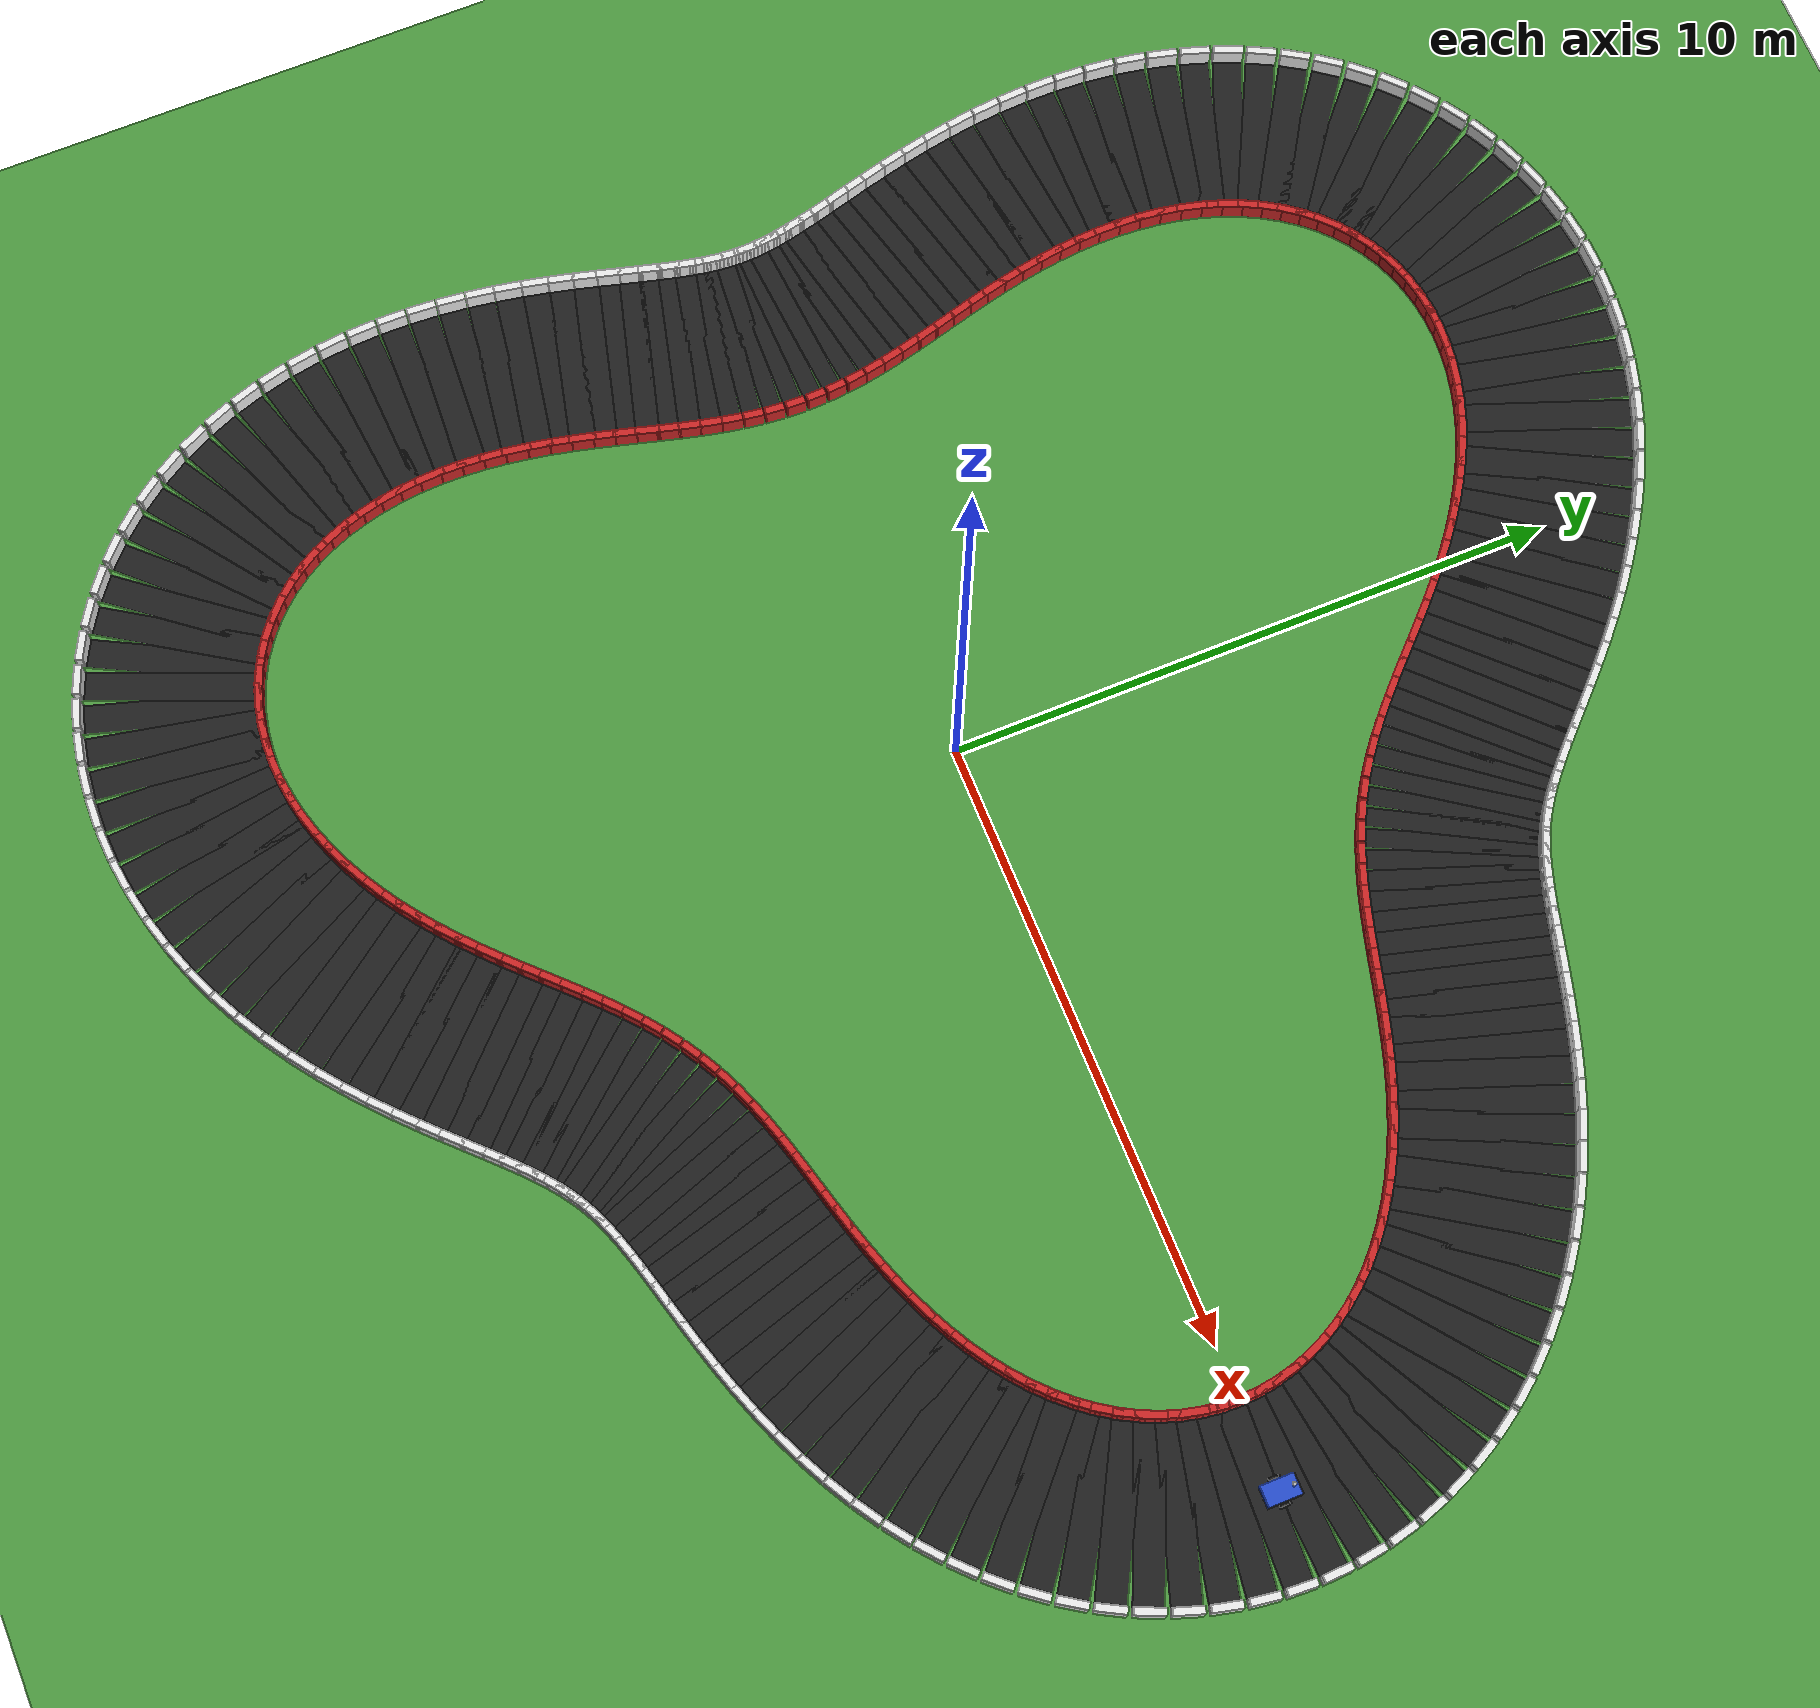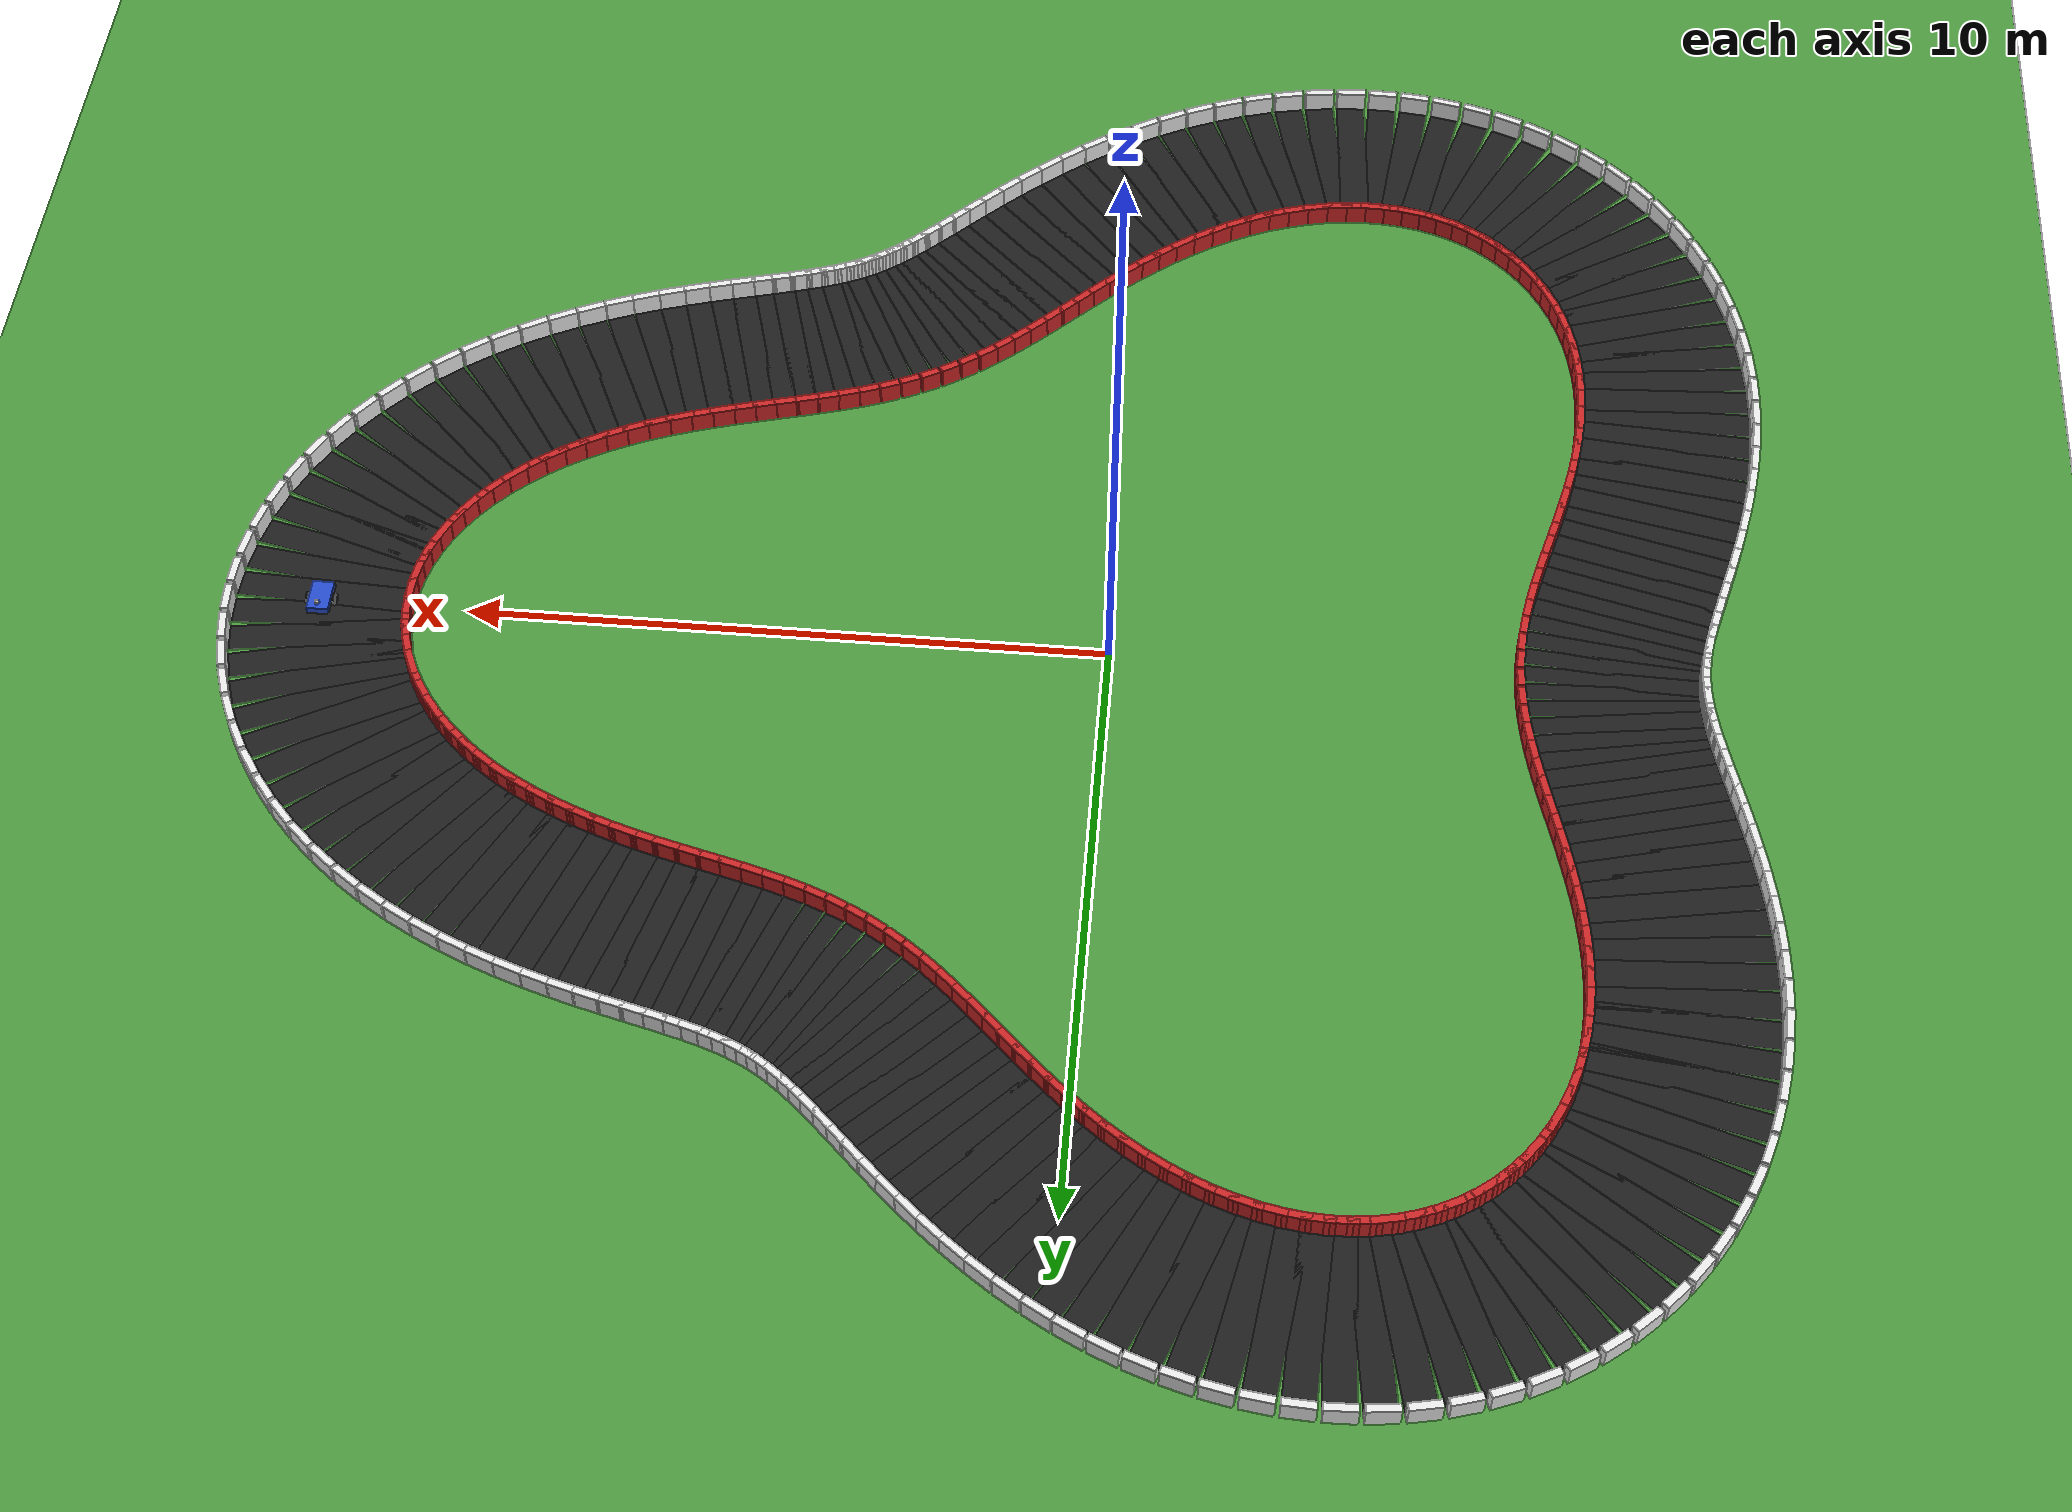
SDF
<?xml version='1.0'?>
<sdf version='1.7'>
  <world name='rl_track'>
    <physics name='fast_ode' type='ode'><max_step_size>0.005</max_step_size><real_time_update_rate>1000</real_time_update_rate><real_time_factor>5</real_time_factor><ode><solver><type>quick</type><iters>50</iters></solver></ode></physics>
    <scene><ambient>0.55 0.55 0.55 1</ambient><background>0.75 0.82 0.90 1</background><shadows>false</shadows></scene>
    <spherical_coordinates><surface_model>EARTH_WGS84</surface_model><world_frame_orientation>ENU</world_frame_orientation><latitude_deg>0</latitude_deg><longitude_deg>0</longitude_deg><elevation>0</elevation><heading_deg>0</heading_deg></spherical_coordinates>
    <include><uri>model://sun</uri></include>
    <model name='ground'><static>true</static><link name='link'><collision name='collision'><geometry><plane><normal>0 0 1</normal><size>40 40</size></plane></geometry></collision><visual name='visual'><geometry><plane><normal>0 0 1</normal><size>40 40</size></plane></geometry><material><script><uri>file://media/materials/scripts/gazebo.material</uri><name>Gazebo/Grass</name></script></material></visual></link></model>
    <plugin name='gazebo_ros_state' filename='libgazebo_ros_state.so'><ros><namespace>/gazebo</namespace></ros><update_rate>50</update_rate></plugin>
    <model name='track'>
      <static>true</static>

      <link name='road_000'>
        <pose>12.289958 0.214412 0.003000 0 0 1.617599028</pose>
        <visual name='visual'>
          <geometry><box><size>0.469294 2.700000 0.006000</size></box></geometry>
          <material><script><uri>file://media/materials/scripts/gazebo.material</uri><name>Gazebo/Black</name></script></material>
        </visual>
      </link>

      <link name='inner_wall_000'>
        <pose>13.698414 0.280380 0.175000 0 0 1.617599028</pose>
        <collision name='collision'>
          <geometry><box><size>0.479294 0.120000 0.350000</size></box></geometry>
          <surface><contact><ode><kp>1000000</kp><kd>10</kd></ode></contact></surface>
        </collision>
        <visual name='visual'>
          <geometry><box><size>0.479294 0.120000 0.350000</size></box></geometry>
          <material><script><uri>file://media/materials/scripts/gazebo.material</uri><name>Gazebo/White</name></script></material>
        </visual>
      </link>

      <link name='outer_wall_000'>
        <pose>10.881502 0.148444 0.175000 0 0 1.617599028</pose>
        <collision name='collision'>
          <geometry><box><size>0.479294 0.120000 0.350000</size></box></geometry>
          <surface><contact><ode><kp>1000000</kp><kd>10</kd></ode></contact></surface>
        </collision>
        <visual name='visual'>
          <geometry><box><size>0.479294 0.120000 0.350000</size></box></geometry>
          <material><script><uri>file://media/materials/scripts/gazebo.material</uri><name>Gazebo/Red</name></script></material>
        </visual>
      </link>

      <link name='road_001'>
        <pose>12.249907 0.641661 0.003000 0 0 1.710862233</pose>
        <visual name='visual'>
          <geometry><box><size>0.469884 2.700000 0.006000</size></box></geometry>
          <material><script><uri>file://media/materials/scripts/gazebo.material</uri><name>Gazebo/Black</name></script></material>
        </visual>
      </link>

      <link name='inner_wall_001'>
        <pose>13.646099 0.838509 0.175000 0 0 1.710862233</pose>
        <collision name='collision'>
          <geometry><box><size>0.479884 0.120000 0.350000</size></box></geometry>
          <surface><contact><ode><kp>1000000</kp><kd>10</kd></ode></contact></surface>
        </collision>
        <visual name='visual'>
          <geometry><box><size>0.479884 0.120000 0.350000</size></box></geometry>
          <material><script><uri>file://media/materials/scripts/gazebo.material</uri><name>Gazebo/White</name></script></material>
        </visual>
      </link>

      <link name='outer_wall_001'>
        <pose>10.853716 0.444814 0.175000 0 0 1.710862233</pose>
        <collision name='collision'>
          <geometry><box><size>0.479884 0.120000 0.350000</size></box></geometry>
          <surface><contact><ode><kp>1000000</kp><kd>10</kd></ode></contact></surface>
        </collision>
        <visual name='visual'>
          <geometry><box><size>0.479884 0.120000 0.350000</size></box></geometry>
          <material><script><uri>file://media/materials/scripts/gazebo.material</uri><name>Gazebo/Red</name></script></material>
        </visual>
      </link>

      <link name='road_002'>
        <pose>12.170283 1.064216 0.003000 0 0 1.803113877</pose>
        <visual name='visual'>
          <geometry><box><size>0.471014 2.700000 0.006000</size></box></geometry>
          <material><script><uri>file://media/materials/scripts/gazebo.material</uri><name>Gazebo/Black</name></script></material>
        </visual>
      </link>

      <link name='inner_wall_002'>
        <pose>13.542404 1.388845 0.175000 0 0 1.803113877</pose>
        <collision name='collision'>
          <geometry><box><size>0.481014 0.120000 0.350000</size></box></geometry>
          <surface><contact><ode><kp>1000000</kp><kd>10</kd></ode></contact></surface>
        </collision>
        <visual name='visual'>
          <geometry><box><size>0.481014 0.120000 0.350000</size></box></geometry>
          <material><script><uri>file://media/materials/scripts/gazebo.material</uri><name>Gazebo/White</name></script></material>
        </visual>
      </link>

      <link name='outer_wall_002'>
        <pose>10.798162 0.739587 0.175000 0 0 1.803113877</pose>
        <collision name='collision'>
          <geometry><box><size>0.481014 0.120000 0.350000</size></box></geometry>
          <surface><contact><ode><kp>1000000</kp><kd>10</kd></ode></contact></surface>
        </collision>
        <visual name='visual'>
          <geometry><box><size>0.481014 0.120000 0.350000</size></box></geometry>
          <material><script><uri>file://media/materials/scripts/gazebo.material</uri><name>Gazebo/Red</name></script></material>
        </visual>
      </link>

      <link name='road_003'>
        <pose>12.052026 1.479044 0.003000 0 0 1.893727624</pose>
        <visual name='visual'>
          <geometry><box><size>0.472582 2.700000 0.006000</size></box></geometry>
          <material><script><uri>file://media/materials/scripts/gazebo.material</uri><name>Gazebo/Black</name></script></material>
        </visual>
      </link>

      <link name='inner_wall_003'>
        <pose>13.389143 1.926505 0.175000 0 0 1.893727624</pose>
        <collision name='collision'>
          <geometry><box><size>0.482582 0.120000 0.350000</size></box></geometry>
          <surface><contact><ode><kp>1000000</kp><kd>10</kd></ode></contact></surface>
        </collision>
        <visual name='visual'>
          <geometry><box><size>0.482582 0.120000 0.350000</size></box></geometry>
          <material><script><uri>file://media/materials/scripts/gazebo.material</uri><name>Gazebo/White</name></script></material>
        </visual>
      </link>

      <link name='outer_wall_003'>
        <pose>10.714910 1.031584 0.175000 0 0 1.893727624</pose>
        <collision name='collision'>
          <geometry><box><size>0.482582 0.120000 0.350000</size></box></geometry>
          <surface><contact><ode><kp>1000000</kp><kd>10</kd></ode></contact></surface>
        </collision>
        <visual name='visual'>
          <geometry><box><size>0.482582 0.120000 0.350000</size></box></geometry>
          <material><script><uri>file://media/materials/scripts/gazebo.material</uri><name>Gazebo/Red</name></script></material>
        </visual>
      </link>

      <link name='road_004'>
        <pose>11.896531 1.883260 0.003000 0 0 1.982142442</pose>
        <visual name='visual'>
          <geometry><box><size>0.474449 2.700000 0.006000</size></box></geometry>
          <material><script><uri>file://media/materials/scripts/gazebo.material</uri><name>Gazebo/Black</name></script></material>
        </visual>
      </link>

      <link name='inner_wall_004'>
        <pose>13.188914 2.447039 0.175000 0 0 1.982142442</pose>
        <collision name='collision'>
          <geometry><box><size>0.484449 0.120000 0.350000</size></box></geometry>
          <surface><contact><ode><kp>1000000</kp><kd>10</kd></ode></contact></surface>
        </collision>
        <visual name='visual'>
          <geometry><box><size>0.484449 0.120000 0.350000</size></box></geometry>
          <material><script><uri>file://media/materials/scripts/gazebo.material</uri><name>Gazebo/White</name></script></material>
        </visual>
      </link>

      <link name='outer_wall_004'>
        <pose>10.604148 1.319480 0.175000 0 0 1.982142442</pose>
        <collision name='collision'>
          <geometry><box><size>0.484449 0.120000 0.350000</size></box></geometry>
          <surface><contact><ode><kp>1000000</kp><kd>10</kd></ode></contact></surface>
        </collision>
        <visual name='visual'>
          <geometry><box><size>0.484449 0.120000 0.350000</size></box></geometry>
          <material><script><uri>file://media/materials/scripts/gazebo.material</uri><name>Gazebo/Red</name></script></material>
        </visual>
      </link>

      <link name='road_005'>
        <pose>11.705614 2.274175 0.003000 0 0 2.067876769</pose>
        <visual name='visual'>
          <geometry><box><size>0.476441 2.700000 0.006000</size></box></geometry>
          <material><script><uri>file://media/materials/scripts/gazebo.material</uri><name>Gazebo/Black</name></script></material>
        </visual>
      </link>

      <link name='inner_wall_005'>
        <pose>12.944974 2.946550 0.175000 0 0 2.067876769</pose>
        <collision name='collision'>
          <geometry><box><size>0.486441 0.120000 0.350000</size></box></geometry>
          <surface><contact><ode><kp>1000000</kp><kd>10</kd></ode></contact></surface>
        </collision>
        <visual name='visual'>
          <geometry><box><size>0.486441 0.120000 0.350000</size></box></geometry>
          <material><script><uri>file://media/materials/scripts/gazebo.material</uri><name>Gazebo/White</name></script></material>
        </visual>
      </link>

      <link name='outer_wall_005'>
        <pose>10.466255 1.601801 0.175000 0 0 2.067876769</pose>
        <collision name='collision'>
          <geometry><box><size>0.486441 0.120000 0.350000</size></box></geometry>
          <surface><contact><ode><kp>1000000</kp><kd>10</kd></ode></contact></surface>
        </collision>
        <visual name='visual'>
          <geometry><box><size>0.486441 0.120000 0.350000</size></box></geometry>
          <material><script><uri>file://media/materials/scripts/gazebo.material</uri><name>Gazebo/Red</name></script></material>
        </visual>
      </link>

      <link name='road_006'>
        <pose>11.481486 2.649353 0.003000 0 0 2.150533756</pose>
        <visual name='visual'>
          <geometry><box><size>0.478358 2.700000 0.006000</size></box></geometry>
          <material><script><uri>file://media/materials/scripts/gazebo.material</uri><name>Gazebo/Black</name></script></material>
        </visual>
      </link>

      <link name='inner_wall_006'>
        <pose>12.661101 3.421757 0.175000 0 0 2.150533756</pose>
        <collision name='collision'>
          <geometry><box><size>0.488358 0.120000 0.350000</size></box></geometry>
          <surface><contact><ode><kp>1000000</kp><kd>10</kd></ode></contact></surface>
        </collision>
        <visual name='visual'>
          <geometry><box><size>0.488358 0.120000 0.350000</size></box></geometry>
          <material><script><uri>file://media/materials/scripts/gazebo.material</uri><name>Gazebo/White</name></script></material>
        </visual>
      </link>

      <link name='outer_wall_006'>
        <pose>10.301871 1.876949 0.175000 0 0 2.150533756</pose>
        <collision name='collision'>
          <geometry><box><size>0.488358 0.120000 0.350000</size></box></geometry>
          <surface><contact><ode><kp>1000000</kp><kd>10</kd></ode></contact></surface>
        </collision>
        <visual name='visual'>
          <geometry><box><size>0.488358 0.120000 0.350000</size></box></geometry>
          <material><script><uri>file://media/materials/scripts/gazebo.material</uri><name>Gazebo/Red</name></script></material>
        </visual>
      </link>

      <link name='road_007'>
        <pose>11.226709 3.006650 0.003000 0 0 2.229798280</pose>
        <visual name='visual'>
          <geometry><box><size>0.479992 2.700000 0.006000</size></box></geometry>
          <material><script><uri>file://media/materials/scripts/gazebo.material</uri><name>Gazebo/Black</name></script></material>
        </visual>
      </link>

      <link name='inner_wall_007'>
        <pose>12.341460 3.870032 0.175000 0 0 2.229798280</pose>
        <collision name='collision'>
          <geometry><box><size>0.489992 0.120000 0.350000</size></box></geometry>
          <surface><contact><ode><kp>1000000</kp><kd>10</kd></ode></contact></surface>
        </collision>
        <visual name='visual'>
          <geometry><box><size>0.489992 0.120000 0.350000</size></box></geometry>
          <material><script><uri>file://media/materials/scripts/gazebo.material</uri><name>Gazebo/White</name></script></material>
        </visual>
      </link>

      <link name='outer_wall_007'>
        <pose>10.111958 2.143267 0.175000 0 0 2.229798280</pose>
        <collision name='collision'>
          <geometry><box><size>0.489992 0.120000 0.350000</size></box></geometry>
          <surface><contact><ode><kp>1000000</kp><kd>10</kd></ode></contact></surface>
        </collision>
        <visual name='visual'>
          <geometry><box><size>0.489992 0.120000 0.350000</size></box></geometry>
          <material><script><uri>file://media/materials/scripts/gazebo.material</uri><name>Gazebo/Red</name></script></material>
        </visual>
      </link>

      <link name='road_008'>
        <pose>10.944152 3.344256 0.003000 0 0 2.305427389</pose>
        <visual name='visual'>
          <geometry><box><size>0.481129 2.700000 0.006000</size></box></geometry>
          <material><script><uri>file://media/materials/scripts/gazebo.material</uri><name>Gazebo/Black</name></script></material>
        </visual>
      </link>

      <link name='inner_wall_008'>
        <pose>11.990482 4.289398 0.175000 0 0 2.305427389</pose>
        <collision name='collision'>
          <geometry><box><size>0.491129 0.120000 0.350000</size></box></geometry>
          <surface><contact><ode><kp>1000000</kp><kd>10</kd></ode></contact></surface>
        </collision>
        <visual name='visual'>
          <geometry><box><size>0.491129 0.120000 0.350000</size></box></geometry>
          <material><script><uri>file://media/materials/scripts/gazebo.material</uri><name>Gazebo/White</name></script></material>
        </visual>
      </link>

      <link name='outer_wall_008'>
        <pose>9.897822 2.399114 0.175000 0 0 2.305427389</pose>
        <collision name='collision'>
          <geometry><box><size>0.491129 0.120000 0.350000</size></box></geometry>
          <surface><contact><ode><kp>1000000</kp><kd>10</kd></ode></contact></surface>
        </collision>
        <visual name='visual'>
          <geometry><box><size>0.491129 0.120000 0.350000</size></box></geometry>
          <material><script><uri>file://media/materials/scripts/gazebo.material</uri><name>Gazebo/Red</name></script></material>
        </visual>
      </link>

      <link name='road_009'>
        <pose>10.636938 3.660728 0.003000 0 0 2.377236263</pose>
        <visual name='visual'>
          <geometry><box><size>0.481562 2.700000 0.006000</size></box></geometry>
          <material><script><uri>file://media/materials/scripts/gazebo.material</uri><name>Gazebo/Black</name></script></material>
        </visual>
      </link>

      <link name='inner_wall_009'>
        <pose>11.612761 4.678506 0.175000 0 0 2.377236263</pose>
        <collision name='collision'>
          <geometry><box><size>0.491562 0.120000 0.350000</size></box></geometry>
          <surface><contact><ode><kp>1000000</kp><kd>10</kd></ode></contact></surface>
        </collision>
        <visual name='visual'>
          <geometry><box><size>0.491562 0.120000 0.350000</size></box></geometry>
          <material><script><uri>file://media/materials/scripts/gazebo.material</uri><name>Gazebo/White</name></script></material>
        </visual>
      </link>

      <link name='outer_wall_009'>
        <pose>9.661116 2.642951 0.175000 0 0 2.377236263</pose>
        <collision name='collision'>
          <geometry><box><size>0.491562 0.120000 0.350000</size></box></geometry>
          <surface><contact><ode><kp>1000000</kp><kd>10</kd></ode></contact></surface>
        </collision>
        <visual name='visual'>
          <geometry><box><size>0.491562 0.120000 0.350000</size></box></geometry>
          <material><script><uri>file://media/materials/scripts/gazebo.material</uri><name>Gazebo/Red</name></script></material>
        </visual>
      </link>

      <link name='road_010'>
        <pose>10.308393 3.955016 0.003000 0 0 2.445081689</pose>
        <visual name='visual'>
          <geometry><box><size>0.481097 2.700000 0.006000</size></box></geometry>
          <material><script><uri>file://media/materials/scripts/gazebo.material</uri><name>Gazebo/Black</name></script></material>
        </visual>
      </link>

      <link name='inner_wall_010'>
        <pose>11.212972 5.036607 0.175000 0 0 2.445081689</pose>
        <collision name='collision'>
          <geometry><box><size>0.491097 0.120000 0.350000</size></box></geometry>
          <surface><contact><ode><kp>1000000</kp><kd>10</kd></ode></contact></surface>
        </collision>
        <visual name='visual'>
          <geometry><box><size>0.491097 0.120000 0.350000</size></box></geometry>
          <material><script><uri>file://media/materials/scripts/gazebo.material</uri><name>Gazebo/White</name></script></material>
        </visual>
      </link>

      <link name='outer_wall_010'>
        <pose>9.403814 2.873426 0.175000 0 0 2.445081689</pose>
        <collision name='collision'>
          <geometry><box><size>0.491097 0.120000 0.350000</size></box></geometry>
          <surface><contact><ode><kp>1000000</kp><kd>10</kd></ode></contact></surface>
        </collision>
        <visual name='visual'>
          <geometry><box><size>0.491097 0.120000 0.350000</size></box></geometry>
          <material><script><uri>file://media/materials/scripts/gazebo.material</uri><name>Gazebo/Red</name></script></material>
        </visual>
      </link>

      <link name='road_011'>
        <pose>9.961980 4.226479 0.003000 0 0 2.508844629</pose>
        <visual name='visual'>
          <geometry><box><size>0.479564 2.700000 0.006000</size></box></geometry>
          <material><script><uri>file://media/materials/scripts/gazebo.material</uri><name>Gazebo/Black</name></script></material>
        </visual>
      </link>

      <link name='inner_wall_011'>
        <pose>10.795802 5.363511 0.175000 0 0 2.508844629</pose>
        <collision name='collision'>
          <geometry><box><size>0.489564 0.120000 0.350000</size></box></geometry>
          <surface><contact><ode><kp>1000000</kp><kd>10</kd></ode></contact></surface>
        </collision>
        <visual name='visual'>
          <geometry><box><size>0.489564 0.120000 0.350000</size></box></geometry>
          <material><script><uri>file://media/materials/scripts/gazebo.material</uri><name>Gazebo/White</name></script></material>
        </visual>
      </link>

      <link name='outer_wall_011'>
        <pose>9.128159 3.089447 0.175000 0 0 2.508844629</pose>
        <collision name='collision'>
          <geometry><box><size>0.489564 0.120000 0.350000</size></box></geometry>
          <surface><contact><ode><kp>1000000</kp><kd>10</kd></ode></contact></surface>
        </collision>
        <visual name='visual'>
          <geometry><box><size>0.489564 0.120000 0.350000</size></box></geometry>
          <material><script><uri>file://media/materials/scripts/gazebo.material</uri><name>Gazebo/Red</name></script></material>
        </visual>
      </link>

      <link name='road_012'>
        <pose>9.601244 4.474895 0.003000 0 0 2.568412942</pose>
        <visual name='visual'>
          <geometry><box><size>0.476818 2.700000 0.006000</size></box></geometry>
          <material><script><uri>file://media/materials/scripts/gazebo.material</uri><name>Gazebo/Black</name></script></material>
        </visual>
      </link>

      <link name='inner_wall_012'>
        <pose>10.365896 5.659550 0.175000 0 0 2.568412942</pose>
        <collision name='collision'>
          <geometry><box><size>0.486818 0.120000 0.350000</size></box></geometry>
          <surface><contact><ode><kp>1000000</kp><kd>10</kd></ode></contact></surface>
        </collision>
        <visual name='visual'>
          <geometry><box><size>0.486818 0.120000 0.350000</size></box></geometry>
          <material><script><uri>file://media/materials/scripts/gazebo.material</uri><name>Gazebo/White</name></script></material>
        </visual>
      </link>

      <link name='outer_wall_012'>
        <pose>8.836592 3.290240 0.175000 0 0 2.568412942</pose>
        <collision name='collision'>
          <geometry><box><size>0.486818 0.120000 0.350000</size></box></geometry>
          <surface><contact><ode><kp>1000000</kp><kd>10</kd></ode></contact></surface>
        </collision>
        <visual name='visual'>
          <geometry><box><size>0.486818 0.120000 0.350000</size></box></geometry>
          <material><script><uri>file://media/materials/scripts/gazebo.material</uri><name>Gazebo/Red</name></script></material>
        </visual>
      </link>

      <link name='road_013'>
        <pose>9.229746 4.700462 0.003000 0 0 2.623664831</pose>
        <visual name='visual'>
          <geometry><box><size>0.472747 2.700000 0.006000</size></box></geometry>
          <material><script><uri>file://media/materials/scripts/gazebo.material</uri><name>Gazebo/Black</name></script></material>
        </visual>
      </link>

      <link name='inner_wall_013'>
        <pose>9.927810 5.925536 0.175000 0 0 2.623664831</pose>
        <collision name='collision'>
          <geometry><box><size>0.482747 0.120000 0.350000</size></box></geometry>
          <surface><contact><ode><kp>1000000</kp><kd>10</kd></ode></contact></surface>
        </collision>
        <visual name='visual'>
          <geometry><box><size>0.482747 0.120000 0.350000</size></box></geometry>
          <material><script><uri>file://media/materials/scripts/gazebo.material</uri><name>Gazebo/White</name></script></material>
        </visual>
      </link>

      <link name='outer_wall_013'>
        <pose>8.531682 3.475387 0.175000 0 0 2.623664831</pose>
        <collision name='collision'>
          <geometry><box><size>0.482747 0.120000 0.350000</size></box></geometry>
          <surface><contact><ode><kp>1000000</kp><kd>10</kd></ode></contact></surface>
        </collision>
        <visual name='visual'>
          <geometry><box><size>0.482747 0.120000 0.350000</size></box></geometry>
          <material><script><uri>file://media/materials/scripts/gazebo.material</uri><name>Gazebo/Red</name></script></material>
        </visual>
      </link>

      <link name='road_014'>
        <pose>8.851002 4.903792 0.003000 0 0 2.674453203</pose>
        <visual name='visual'>
          <geometry><box><size>0.467274 2.700000 0.006000</size></box></geometry>
          <material><script><uri>file://media/materials/scripts/gazebo.material</uri><name>Gazebo/Black</name></script></material>
        </visual>
      </link>

      <link name='inner_wall_014'>
        <pose>9.485973 6.162725 0.175000 0 0 2.674453203</pose>
        <collision name='collision'>
          <geometry><box><size>0.477274 0.120000 0.350000</size></box></geometry>
          <surface><contact><ode><kp>1000000</kp><kd>10</kd></ode></contact></surface>
        </collision>
        <visual name='visual'>
          <geometry><box><size>0.477274 0.120000 0.350000</size></box></geometry>
          <material><script><uri>file://media/materials/scripts/gazebo.material</uri><name>Gazebo/White</name></script></material>
        </visual>
      </link>

      <link name='outer_wall_014'>
        <pose>8.216031 3.644859 0.175000 0 0 2.674453203</pose>
        <collision name='collision'>
          <geometry><box><size>0.477274 0.120000 0.350000</size></box></geometry>
          <surface><contact><ode><kp>1000000</kp><kd>10</kd></ode></contact></surface>
        </collision>
        <visual name='visual'>
          <geometry><box><size>0.477274 0.120000 0.350000</size></box></geometry>
          <material><script><uri>file://media/materials/scripts/gazebo.material</uri><name>Gazebo/Red</name></script></material>
        </visual>
      </link>

      <link name='road_015'>
        <pose>8.468426 5.085896 0.003000 0 0 2.720590876</pose>
        <visual name='visual'>
          <geometry><box><size>0.460363 2.700000 0.006000</size></box></geometry>
          <material><script><uri>file://media/materials/scripts/gazebo.material</uri><name>Gazebo/Black</name></script></material>
        </visual>
      </link>

      <link name='inner_wall_015'>
        <pose>9.044657 6.372775 0.175000 0 0 2.720590876</pose>
        <collision name='collision'>
          <geometry><box><size>0.470363 0.120000 0.350000</size></box></geometry>
          <surface><contact><ode><kp>1000000</kp><kd>10</kd></ode></contact></surface>
        </collision>
        <visual name='visual'>
          <geometry><box><size>0.470363 0.120000 0.350000</size></box></geometry>
          <material><script><uri>file://media/materials/scripts/gazebo.material</uri><name>Gazebo/White</name></script></material>
        </visual>
      </link>

      <link name='outer_wall_015'>
        <pose>7.892194 3.799017 0.175000 0 0 2.720590876</pose>
        <collision name='collision'>
          <geometry><box><size>0.470363 0.120000 0.350000</size></box></geometry>
          <surface><contact><ode><kp>1000000</kp><kd>10</kd></ode></contact></surface>
        </collision>
        <visual name='visual'>
          <geometry><box><size>0.470363 0.120000 0.350000</size></box></geometry>
          <material><script><uri>file://media/materials/scripts/gazebo.material</uri><name>Gazebo/Red</name></script></material>
        </visual>
      </link>

      <link name='road_016'>
        <pose>8.085265 5.248158 0.003000 0 0 2.761836565</pose>
        <visual name='visual'>
          <geometry><box><size>0.452019 2.700000 0.006000</size></box></geometry>
          <material><script><uri>file://media/materials/scripts/gazebo.material</uri><name>Gazebo/Black</name></script></material>
        </visual>
      </link>

      <link name='inner_wall_016'>
        <pose>8.607943 6.557703 0.175000 0 0 2.761836565</pose>
        <collision name='collision'>
          <geometry><box><size>0.462019 0.120000 0.350000</size></box></geometry>
          <surface><contact><ode><kp>1000000</kp><kd>10</kd></ode></contact></surface>
        </collision>
        <visual name='visual'>
          <geometry><box><size>0.462019 0.120000 0.350000</size></box></geometry>
          <material><script><uri>file://media/materials/scripts/gazebo.material</uri><name>Gazebo/White</name></script></material>
        </visual>
      </link>

      <link name='outer_wall_016'>
        <pose>7.562586 3.938614 0.175000 0 0 2.761836565</pose>
        <collision name='collision'>
          <geometry><box><size>0.462019 0.120000 0.350000</size></box></geometry>
          <surface><contact><ode><kp>1000000</kp><kd>10</kd></ode></contact></surface>
        </collision>
        <visual name='visual'>
          <geometry><box><size>0.462019 0.120000 0.350000</size></box></geometry>
          <material><script><uri>file://media/materials/scripts/gazebo.material</uri><name>Gazebo/Red</name></script></material>
        </visual>
      </link>

      <link name='road_017'>
        <pose>7.704551 5.392308 0.003000 0 0 2.797881679</pose>
        <visual name='visual'>
          <geometry><box><size>0.442292 2.700000 0.006000</size></box></geometry>
          <material><script><uri>file://media/materials/scripts/gazebo.material</uri><name>Gazebo/Black</name></script></material>
        </visual>
      </link>

      <link name='inner_wall_017'>
        <pose>8.179698 6.719838 0.175000 0 0 2.797881679</pose>
        <collision name='collision'>
          <geometry><box><size>0.452292 0.120000 0.350000</size></box></geometry>
          <surface><contact><ode><kp>1000000</kp><kd>10</kd></ode></contact></surface>
        </collision>
        <visual name='visual'>
          <geometry><box><size>0.452292 0.120000 0.350000</size></box></geometry>
          <material><script><uri>file://media/materials/scripts/gazebo.material</uri><name>Gazebo/White</name></script></material>
        </visual>
      </link>

      <link name='outer_wall_017'>
        <pose>7.229405 4.064778 0.175000 0 0 2.797881679</pose>
        <collision name='collision'>
          <geometry><box><size>0.452292 0.120000 0.350000</size></box></geometry>
          <surface><contact><ode><kp>1000000</kp><kd>10</kd></ode></contact></surface>
        </collision>
        <visual name='visual'>
          <geometry><box><size>0.452292 0.120000 0.350000</size></box></geometry>
          <material><script><uri>file://media/materials/scripts/gazebo.material</uri><name>Gazebo/Red</name></script></material>
        </visual>
      </link>

      <link name='road_018'>
        <pose>7.329049 5.520379 0.003000 0 0 2.828338421</pose>
        <visual name='visual'>
          <geometry><box><size>0.431283 2.700000 0.006000</size></box></geometry>
          <material><script><uri>file://media/materials/scripts/gazebo.material</uri><name>Gazebo/Black</name></script></material>
        </visual>
      </link>

      <link name='inner_wall_018'>
        <pose>7.763549 6.861762 0.175000 0 0 2.828338421</pose>
        <collision name='collision'>
          <geometry><box><size>0.441283 0.120000 0.350000</size></box></geometry>
          <surface><contact><ode><kp>1000000</kp><kd>10</kd></ode></contact></surface>
        </collision>
        <visual name='visual'>
          <geometry><box><size>0.441283 0.120000 0.350000</size></box></geometry>
          <material><script><uri>file://media/materials/scripts/gazebo.material</uri><name>Gazebo/White</name></script></material>
        </visual>
      </link>

      <link name='outer_wall_018'>
        <pose>6.894549 4.178995 0.175000 0 0 2.828338421</pose>
        <collision name='collision'>
          <geometry><box><size>0.441283 0.120000 0.350000</size></box></geometry>
          <surface><contact><ode><kp>1000000</kp><kd>10</kd></ode></contact></surface>
        </collision>
        <visual name='visual'>
          <geometry><box><size>0.441283 0.120000 0.350000</size></box></geometry>
          <material><script><uri>file://media/materials/scripts/gazebo.material</uri><name>Gazebo/Red</name></script></material>
        </visual>
      </link>

      <link name='road_019'>
        <pose>6.961211 5.634669 0.003000 0 0 2.852730410</pose>
        <visual name='visual'>
          <geometry><box><size>0.419143 2.700000 0.006000</size></box></geometry>
          <material><script><uri>file://media/materials/scripts/gazebo.material</uri><name>Gazebo/Black</name></script></material>
        </visual>
      </link>

      <link name='inner_wall_019'>
        <pose>7.362866 6.986250 0.175000 0 0 2.852730410</pose>
        <collision name='collision'>
          <geometry><box><size>0.429143 0.120000 0.350000</size></box></geometry>
          <surface><contact><ode><kp>1000000</kp><kd>10</kd></ode></contact></surface>
        </collision>
        <visual name='visual'>
          <geometry><box><size>0.429143 0.120000 0.350000</size></box></geometry>
          <material><script><uri>file://media/materials/scripts/gazebo.material</uri><name>Gazebo/White</name></script></material>
        </visual>
      </link>

      <link name='outer_wall_019'>
        <pose>6.559556 4.283087 0.175000 0 0 2.852730410</pose>
        <collision name='collision'>
          <geometry><box><size>0.429143 0.120000 0.350000</size></box></geometry>
          <surface><contact><ode><kp>1000000</kp><kd>10</kd></ode></contact></surface>
        </collision>
        <visual name='visual'>
          <geometry><box><size>0.429143 0.120000 0.350000</size></box></geometry>
          <material><script><uri>file://media/materials/scripts/gazebo.material</uri><name>Gazebo/Red</name></script></material>
        </visual>
      </link>

      <link name='road_020'>
        <pose>6.603140 5.737687 0.003000 0 0 2.870488422</pose>
        <visual name='visual'>
          <geometry><box><size>0.406078 2.700000 0.006000</size></box></geometry>
          <material><script><uri>file://media/materials/scripts/gazebo.material</uri><name>Gazebo/Black</name></script></material>
        </visual>
      </link>

      <link name='inner_wall_020'>
        <pose>6.980731 7.096188 0.175000 0 0 2.870488422</pose>
        <collision name='collision'>
          <geometry><box><size>0.416078 0.120000 0.350000</size></box></geometry>
          <surface><contact><ode><kp>1000000</kp><kd>10</kd></ode></contact></surface>
        </collision>
        <visual name='visual'>
          <geometry><box><size>0.416078 0.120000 0.350000</size></box></geometry>
          <material><script><uri>file://media/materials/scripts/gazebo.material</uri><name>Gazebo/White</name></script></material>
        </visual>
      </link>

      <link name='outer_wall_020'>
        <pose>6.225548 4.379186 0.175000 0 0 2.870488422</pose>
        <collision name='collision'>
          <geometry><box><size>0.416078 0.120000 0.350000</size></box></geometry>
          <surface><contact><ode><kp>1000000</kp><kd>10</kd></ode></contact></surface>
        </collision>
        <visual name='visual'>
          <geometry><box><size>0.416078 0.120000 0.350000</size></box></geometry>
          <material><script><uri>file://media/materials/scripts/gazebo.material</uri><name>Gazebo/Red</name></script></material>
        </visual>
      </link>

      <link name='road_021'>
        <pose>6.256560 5.832104 0.003000 0 0 2.880955869</pose>
        <visual name='visual'>
          <geometry><box><size>0.392353 2.700000 0.006000</size></box></geometry>
          <material><script><uri>file://media/materials/scripts/gazebo.material</uri><name>Gazebo/Black</name></script></material>
        </visual>
      </link>

      <link name='inner_wall_021'>
        <pose>6.619911 7.194483 0.175000 0 0 2.880955869</pose>
        <collision name='collision'>
          <geometry><box><size>0.402353 0.120000 0.350000</size></box></geometry>
          <surface><contact><ode><kp>1000000</kp><kd>10</kd></ode></contact></surface>
        </collision>
        <visual name='visual'>
          <geometry><box><size>0.402353 0.120000 0.350000</size></box></geometry>
          <material><script><uri>file://media/materials/scripts/gazebo.material</uri><name>Gazebo/White</name></script></material>
        </visual>
      </link>

      <link name='outer_wall_021'>
        <pose>5.893209 4.469725 0.175000 0 0 2.880955869</pose>
        <collision name='collision'>
          <geometry><box><size>0.402353 0.120000 0.350000</size></box></geometry>
          <surface><contact><ode><kp>1000000</kp><kd>10</kd></ode></contact></surface>
        </collision>
        <visual name='visual'>
          <geometry><box><size>0.402353 0.120000 0.350000</size></box></geometry>
          <material><script><uri>file://media/materials/scripts/gazebo.material</uri><name>Gazebo/Red</name></script></material>
        </visual>
      </link>

      <link name='road_022'>
        <pose>5.922792 5.920691 0.003000 0 0 2.883411629</pose>
        <visual name='visual'>
          <geometry><box><size>0.378296 2.700000 0.006000</size></box></geometry>
          <material><script><uri>file://media/materials/scripts/gazebo.material</uri><name>Gazebo/Black</name></script></material>
        </visual>
      </link>

      <link name='inner_wall_022'>
        <pose>6.282797 7.283958 0.175000 0 0 2.883411629</pose>
        <collision name='collision'>
          <geometry><box><size>0.388296 0.120000 0.350000</size></box></geometry>
          <surface><contact><ode><kp>1000000</kp><kd>10</kd></ode></contact></surface>
        </collision>
        <visual name='visual'>
          <geometry><box><size>0.388296 0.120000 0.350000</size></box></geometry>
          <material><script><uri>file://media/materials/scripts/gazebo.material</uri><name>Gazebo/White</name></script></material>
        </visual>
      </link>

      <link name='outer_wall_022'>
        <pose>5.562788 4.557424 0.175000 0 0 2.883411629</pose>
        <collision name='collision'>
          <geometry><box><size>0.388296 0.120000 0.350000</size></box></geometry>
          <surface><contact><ode><kp>1000000</kp><kd>10</kd></ode></contact></surface>
        </collision>
        <visual name='visual'>
          <geometry><box><size>0.388296 0.120000 0.350000</size></box></geometry>
          <material><script><uri>file://media/materials/scripts/gazebo.material</uri><name>Gazebo/Red</name></script></material>
        </visual>
      </link>

      <link name='road_023'>
        <pose>5.602740 6.006264 0.003000 0 0 2.877121469</pose>
        <visual name='visual'>
          <geometry><box><size>0.364298 2.700000 0.006000</size></box></geometry>
          <material><script><uri>file://media/materials/scripts/gazebo.material</uri><name>Gazebo/Black</name></script></material>
        </visual>
      </link>

      <link name='inner_wall_023'>
        <pose>5.971312 7.367240 0.175000 0 0 2.877121469</pose>
        <collision name='collision'>
          <geometry><box><size>0.374298 0.120000 0.350000</size></box></geometry>
          <surface><contact><ode><kp>1000000</kp><kd>10</kd></ode></contact></surface>
        </collision>
        <visual name='visual'>
          <geometry><box><size>0.374298 0.120000 0.350000</size></box></geometry>
          <material><script><uri>file://media/materials/scripts/gazebo.material</uri><name>Gazebo/White</name></script></material>
        </visual>
      </link>

      <link name='outer_wall_023'>
        <pose>5.234167 4.645289 0.175000 0 0 2.877121469</pose>
        <collision name='collision'>
          <geometry><box><size>0.374298 0.120000 0.350000</size></box></geometry>
          <surface><contact><ode><kp>1000000</kp><kd>10</kd></ode></contact></surface>
        </collision>
        <visual name='visual'>
          <geometry><box><size>0.374298 0.120000 0.350000</size></box></geometry>
          <material><script><uri>file://media/materials/scripts/gazebo.material</uri><name>Gazebo/Red</name></script></material>
        </visual>
      </link>

      <link name='road_024'>
        <pose>5.296881 6.091621 0.003000 0 0 2.861432331</pose>
        <visual name='visual'>
          <geometry><box><size>0.350813 2.700000 0.006000</size></box></geometry>
          <material><script><uri>file://media/materials/scripts/gazebo.material</uri><name>Gazebo/Black</name></script></material>
        </visual>
      </link>

      <link name='inner_wall_024'>
        <pose>5.686760 7.446647 0.175000 0 0 2.861432331</pose>
        <collision name='collision'>
          <geometry><box><size>0.360813 0.120000 0.350000</size></box></geometry>
          <surface><contact><ode><kp>1000000</kp><kd>10</kd></ode></contact></surface>
        </collision>
        <visual name='visual'>
          <geometry><box><size>0.360813 0.120000 0.350000</size></box></geometry>
          <material><script><uri>file://media/materials/scripts/gazebo.material</uri><name>Gazebo/White</name></script></material>
        </visual>
      </link>

      <link name='outer_wall_024'>
        <pose>4.907003 4.736595 0.175000 0 0 2.861432331</pose>
        <collision name='collision'>
          <geometry><box><size>0.360813 0.120000 0.350000</size></box></geometry>
          <surface><contact><ode><kp>1000000</kp><kd>10</kd></ode></contact></surface>
        </collision>
        <visual name='visual'>
          <geometry><box><size>0.360813 0.120000 0.350000</size></box></geometry>
          <material><script><uri>file://media/materials/scripts/gazebo.material</uri><name>Gazebo/Red</name></script></material>
        </visual>
      </link>

      <link name='road_025'>
        <pose>5.005275 6.179484 0.003000 0 0 2.835922841</pose>
        <visual name='visual'>
          <geometry><box><size>0.338349 2.700000 0.006000</size></box></geometry>
          <material><script><uri>file://media/materials/scripts/gazebo.material</uri><name>Gazebo/Black</name></script></material>
        </visual>
      </link>

      <link name='inner_wall_025'>
        <pose>5.429589 7.524124 0.175000 0 0 2.835922841</pose>
        <collision name='collision'>
          <geometry><box><size>0.348349 0.120000 0.350000</size></box></geometry>
          <surface><contact><ode><kp>1000000</kp><kd>10</kd></ode></contact></surface>
        </collision>
        <visual name='visual'>
          <geometry><box><size>0.348349 0.120000 0.350000</size></box></geometry>
          <material><script><uri>file://media/materials/scripts/gazebo.material</uri><name>Gazebo/White</name></script></material>
        </visual>
      </link>

      <link name='outer_wall_025'>
        <pose>4.580960 4.834843 0.175000 0 0 2.835922841</pose>
        <collision name='collision'>
          <geometry><box><size>0.348349 0.120000 0.350000</size></box></geometry>
          <surface><contact><ode><kp>1000000</kp><kd>10</kd></ode></contact></surface>
        </collision>
        <visual name='visual'>
          <geometry><box><size>0.348349 0.120000 0.350000</size></box></geometry>
          <material><script><uri>file://media/materials/scripts/gazebo.material</uri><name>Gazebo/Red</name></script></material>
        </visual>
      </link>

      <link name='road_026'>
        <pose>4.727564 6.272439 0.003000 0 0 2.800612221</pose>
        <visual name='visual'>
          <geometry><box><size>0.327451 2.700000 0.006000</size></box></geometry>
          <material><script><uri>file://media/materials/scripts/gazebo.material</uri><name>Gazebo/Black</name></script></material>
        </visual>
      </link>

      <link name='inner_wall_026'>
        <pose>5.199084 7.601261 0.175000 0 0 2.800612221</pose>
        <collision name='collision'>
          <geometry><box><size>0.337451 0.120000 0.350000</size></box></geometry>
          <surface><contact><ode><kp>1000000</kp><kd>10</kd></ode></contact></surface>
        </collision>
        <visual name='visual'>
          <geometry><box><size>0.337451 0.120000 0.350000</size></box></geometry>
          <material><script><uri>file://media/materials/scripts/gazebo.material</uri><name>Gazebo/White</name></script></material>
        </visual>
      </link>

      <link name='outer_wall_026'>
        <pose>4.256044 4.943616 0.175000 0 0 2.800612221</pose>
        <collision name='collision'>
          <geometry><box><size>0.337451 0.120000 0.350000</size></box></geometry>
          <surface><contact><ode><kp>1000000</kp><kd>10</kd></ode></contact></surface>
        </collision>
        <visual name='visual'>
          <geometry><box><size>0.337451 0.120000 0.350000</size></box></geometry>
          <material><script><uri>file://media/materials/scripts/gazebo.material</uri><name>Gazebo/Red</name></script></material>
        </visual>
      </link>

      <link name='road_027'>
        <pose>4.463002 6.372880 0.003000 0 0 2.756201164</pose>
        <visual name='visual'>
          <geometry><box><size>0.318662 2.700000 0.006000</size></box></geometry>
          <material><script><uri>file://media/materials/scripts/gazebo.material</uri><name>Gazebo/Black</name></script></material>
        </visual>
      </link>

      <link name='inner_wall_027'>
        <pose>4.993052 7.679458 0.175000 0 0 2.756201164</pose>
        <collision name='collision'>
          <geometry><box><size>0.328662 0.120000 0.350000</size></box></geometry>
          <surface><contact><ode><kp>1000000</kp><kd>10</kd></ode></contact></surface>
        </collision>
        <visual name='visual'>
          <geometry><box><size>0.328662 0.120000 0.350000</size></box></geometry>
          <material><script><uri>file://media/materials/scripts/gazebo.material</uri><name>Gazebo/White</name></script></material>
        </visual>
      </link>

      <link name='outer_wall_027'>
        <pose>3.932952 5.066301 0.175000 0 0 2.756201164</pose>
        <collision name='collision'>
          <geometry><box><size>0.328662 0.120000 0.350000</size></box></geometry>
          <surface><contact><ode><kp>1000000</kp><kd>10</kd></ode></contact></surface>
        </collision>
        <visual name='visual'>
          <geometry><box><size>0.328662 0.120000 0.350000</size></box></geometry>
          <material><script><uri>file://media/materials/scripts/gazebo.material</uri><name>Gazebo/Red</name></script></material>
        </visual>
      </link>

      <link name='road_028'>
        <pose>4.210473 6.482956 0.003000 0 0 2.704272586</pose>
        <visual name='visual'>
          <geometry><box><size>0.312479 2.700000 0.006000</size></box></geometry>
          <material><script><uri>file://media/materials/scripts/gazebo.material</uri><name>Gazebo/Black</name></script></material>
        </visual>
      </link>

      <link name='inner_wall_028'>
        <pose>4.807627 7.760261 0.175000 0 0 2.704272586</pose>
        <collision name='collision'>
          <geometry><box><size>0.322479 0.120000 0.350000</size></box></geometry>
          <surface><contact><ode><kp>1000000</kp><kd>10</kd></ode></contact></surface>
        </collision>
        <visual name='visual'>
          <geometry><box><size>0.322479 0.120000 0.350000</size></box></geometry>
          <material><script><uri>file://media/materials/scripts/gazebo.material</uri><name>Gazebo/White</name></script></material>
        </visual>
      </link>

      <link name='outer_wall_028'>
        <pose>3.613319 5.205652 0.175000 0 0 2.704272586</pose>
        <collision name='collision'>
          <geometry><box><size>0.322479 0.120000 0.350000</size></box></geometry>
          <surface><contact><ode><kp>1000000</kp><kd>10</kd></ode></contact></surface>
        </collision>
        <visual name='visual'>
          <geometry><box><size>0.322479 0.120000 0.350000</size></box></geometry>
          <material><script><uri>file://media/materials/scripts/gazebo.material</uri><name>Gazebo/Red</name></script></material>
        </visual>
      </link>

      <link name='road_029'>
        <pose>3.968528 6.604526 0.003000 0 0 2.647340339</pose>
        <visual name='visual'>
          <geometry><box><size>0.309282 2.700000 0.006000</size></box></geometry>
          <material><script><uri>file://media/materials/scripts/gazebo.material</uri><name>Gazebo/Black</name></script></material>
        </visual>
      </link>

      <link name='inner_wall_029'>
        <pose>4.637394 7.845782 0.175000 0 0 2.647340339</pose>
        <collision name='collision'>
          <geometry><box><size>0.319282 0.120000 0.350000</size></box></geometry>
          <surface><contact><ode><kp>1000000</kp><kd>10</kd></ode></contact></surface>
        </collision>
        <visual name='visual'>
          <geometry><box><size>0.319282 0.120000 0.350000</size></box></geometry>
          <material><script><uri>file://media/materials/scripts/gazebo.material</uri><name>Gazebo/White</name></script></material>
        </visual>
      </link>

      <link name='outer_wall_029'>
        <pose>3.299661 5.363269 0.175000 0 0 2.647340339</pose>
        <collision name='collision'>
          <geometry><box><size>0.319282 0.120000 0.350000</size></box></geometry>
          <surface><contact><ode><kp>1000000</kp><kd>10</kd></ode></contact></surface>
        </collision>
        <visual name='visual'>
          <geometry><box><size>0.319282 0.120000 0.350000</size></box></geometry>
          <material><script><uri>file://media/materials/scripts/gazebo.material</uri><name>Gazebo/Red</name></script></material>
        </visual>
      </link>

      <link name='road_030'>
        <pose>3.735423 6.739108 0.003000 0 0 2.588647417</pose>
        <visual name='visual'>
          <geometry><box><size>0.309282 2.700000 0.006000</size></box></geometry>
          <material><script><uri>file://media/materials/scripts/gazebo.material</uri><name>Gazebo/Black</name></script></material>
        </visual>
      </link>

      <link name='inner_wall_030'>
        <pose>4.475949 7.938992 0.175000 0 0 2.588647417</pose>
        <collision name='collision'>
          <geometry><box><size>0.319282 0.120000 0.350000</size></box></geometry>
          <surface><contact><ode><kp>1000000</kp><kd>10</kd></ode></contact></surface>
        </collision>
        <visual name='visual'>
          <geometry><box><size>0.319282 0.120000 0.350000</size></box></geometry>
          <material><script><uri>file://media/materials/scripts/gazebo.material</uri><name>Gazebo/White</name></script></material>
        </visual>
      </link>

      <link name='outer_wall_030'>
        <pose>2.994897 5.539225 0.175000 0 0 2.588647417</pose>
        <collision name='collision'>
          <geometry><box><size>0.319282 0.120000 0.350000</size></box></geometry>
          <surface><contact><ode><kp>1000000</kp><kd>10</kd></ode></contact></surface>
        </collision>
        <visual name='visual'>
          <geometry><box><size>0.319282 0.120000 0.350000</size></box></geometry>
          <material><script><uri>file://media/materials/scripts/gazebo.material</uri><name>Gazebo/Red</name></script></material>
        </visual>
      </link>

      <link name='road_031'>
        <pose>3.509168 6.887855 0.003000 0 0 2.531715170</pose>
        <visual name='visual'>
          <geometry><box><size>0.312479 2.700000 0.006000</size></box></geometry>
          <material><script><uri>file://media/materials/scripts/gazebo.material</uri><name>Gazebo/Black</name></script></material>
        </visual>
      </link>

      <link name='inner_wall_031'>
        <pose>4.316770 8.043657 0.175000 0 0 2.531715170</pose>
        <collision name='collision'>
          <geometry><box><size>0.322479 0.120000 0.350000</size></box></geometry>
          <surface><contact><ode><kp>1000000</kp><kd>10</kd></ode></contact></surface>
        </collision>
        <visual name='visual'>
          <geometry><box><size>0.322479 0.120000 0.350000</size></box></geometry>
          <material><script><uri>file://media/materials/scripts/gazebo.material</uri><name>Gazebo/White</name></script></material>
        </visual>
      </link>

      <link name='outer_wall_031'>
        <pose>2.701567 5.732052 0.175000 0 0 2.531715170</pose>
        <collision name='collision'>
          <geometry><box><size>0.322479 0.120000 0.350000</size></box></geometry>
          <surface><contact><ode><kp>1000000</kp><kd>10</kd></ode></contact></surface>
        </collision>
        <visual name='visual'>
          <geometry><box><size>0.322479 0.120000 0.350000</size></box></geometry>
          <material><script><uri>file://media/materials/scripts/gazebo.material</uri><name>Gazebo/Red</name></script></material>
        </visual>
      </link>

      <link name='road_032'>
        <pose>3.287575 7.051513 0.003000 0 0 2.479786592</pose>
        <visual name='visual'>
          <geometry><box><size>0.318662 2.700000 0.006000</size></box></geometry>
          <material><script><uri>file://media/materials/scripts/gazebo.material</uri><name>Gazebo/Black</name></script></material>
        </visual>
      </link>

      <link name='inner_wall_032'>
        <pose>4.154080 8.163839 0.175000 0 0 2.479786592</pose>
        <collision name='collision'>
          <geometry><box><size>0.328662 0.120000 0.350000</size></box></geometry>
          <surface><contact><ode><kp>1000000</kp><kd>10</kd></ode></contact></surface>
        </collision>
        <visual name='visual'>
          <geometry><box><size>0.328662 0.120000 0.350000</size></box></geometry>
          <material><script><uri>file://media/materials/scripts/gazebo.material</uri><name>Gazebo/White</name></script></material>
        </visual>
      </link>

      <link name='outer_wall_032'>
        <pose>2.421069 5.939187 0.175000 0 0 2.479786592</pose>
        <collision name='collision'>
          <geometry><box><size>0.328662 0.120000 0.350000</size></box></geometry>
          <surface><contact><ode><kp>1000000</kp><kd>10</kd></ode></contact></surface>
        </collision>
        <visual name='visual'>
          <geometry><box><size>0.328662 0.120000 0.350000</size></box></geometry>
          <material><script><uri>file://media/materials/scripts/gazebo.material</uri><name>Gazebo/Red</name></script></material>
        </visual>
      </link>

      <link name='road_033'>
        <pose>3.068309 7.230410 0.003000 0 0 2.435375534</pose>
        <visual name='visual'>
          <geometry><box><size>0.327451 2.700000 0.006000</size></box></geometry>
          <material><script><uri>file://media/materials/scripts/gazebo.material</uri><name>Gazebo/Black</name></script></material>
        </visual>
      </link>

      <link name='inner_wall_033'>
        <pose>3.983343 8.303169 0.175000 0 0 2.435375534</pose>
        <collision name='collision'>
          <geometry><box><size>0.337451 0.120000 0.350000</size></box></geometry>
          <surface><contact><ode><kp>1000000</kp><kd>10</kd></ode></contact></surface>
        </collision>
        <visual name='visual'>
          <geometry><box><size>0.337451 0.120000 0.350000</size></box></geometry>
          <material><script><uri>file://media/materials/scripts/gazebo.material</uri><name>Gazebo/White</name></script></material>
        </visual>
      </link>

      <link name='outer_wall_033'>
        <pose>2.153275 6.157651 0.175000 0 0 2.435375534</pose>
        <collision name='collision'>
          <geometry><box><size>0.337451 0.120000 0.350000</size></box></geometry>
          <surface><contact><ode><kp>1000000</kp><kd>10</kd></ode></contact></surface>
        </collision>
        <visual name='visual'>
          <geometry><box><size>0.337451 0.120000 0.350000</size></box></geometry>
          <material><script><uri>file://media/materials/scripts/gazebo.material</uri><name>Gazebo/Red</name></script></material>
        </visual>
      </link>

      <link name='road_034'>
        <pose>2.848953 7.424437 0.003000 0 0 2.400064915</pose>
        <visual name='visual'>
          <geometry><box><size>0.338349 2.700000 0.006000</size></box></geometry>
          <material><script><uri>file://media/materials/scripts/gazebo.material</uri><name>Gazebo/Black</name></script></material>
        </visual>
      </link>

      <link name='inner_wall_034'>
        <pose>3.801288 8.464224 0.175000 0 0 2.400064915</pose>
        <collision name='collision'>
          <geometry><box><size>0.348349 0.120000 0.350000</size></box></geometry>
          <surface><contact><ode><kp>1000000</kp><kd>10</kd></ode></contact></surface>
        </collision>
        <visual name='visual'>
          <geometry><box><size>0.348349 0.120000 0.350000</size></box></geometry>
          <material><script><uri>file://media/materials/scripts/gazebo.material</uri><name>Gazebo/White</name></script></material>
        </visual>
      </link>

      <link name='outer_wall_034'>
        <pose>1.896617 6.384650 0.175000 0 0 2.400064915</pose>
        <collision name='collision'>
          <geometry><box><size>0.348349 0.120000 0.350000</size></box></geometry>
          <surface><contact><ode><kp>1000000</kp><kd>10</kd></ode></contact></surface>
        </collision>
        <visual name='visual'>
          <geometry><box><size>0.348349 0.120000 0.350000</size></box></geometry>
          <material><script><uri>file://media/materials/scripts/gazebo.material</uri><name>Gazebo/Red</name></script></material>
        </visual>
      </link>

      <link name='road_035'>
        <pose>2.627058 7.633044 0.003000 0 0 2.374555425</pose>
        <visual name='visual'>
          <geometry><box><size>0.350813 2.700000 0.006000</size></box></geometry>
          <material><script><uri>file://media/materials/scripts/gazebo.material</uri><name>Gazebo/Black</name></script></material>
        </visual>
      </link>

      <link name='inner_wall_035'>
        <pose>3.605605 8.648202 0.175000 0 0 2.374555425</pose>
        <collision name='collision'>
          <geometry><box><size>0.360813 0.120000 0.350000</size></box></geometry>
          <surface><contact><ode><kp>1000000</kp><kd>10</kd></ode></contact></surface>
        </collision>
        <visual name='visual'>
          <geometry><box><size>0.360813 0.120000 0.350000</size></box></geometry>
          <material><script><uri>file://media/materials/scripts/gazebo.material</uri><name>Gazebo/White</name></script></material>
        </visual>
      </link>

      <link name='outer_wall_035'>
        <pose>1.648511 6.617887 0.175000 0 0 2.374555425</pose>
        <collision name='collision'>
          <geometry><box><size>0.360813 0.120000 0.350000</size></box></geometry>
          <surface><contact><ode><kp>1000000</kp><kd>10</kd></ode></contact></surface>
        </collision>
        <visual name='visual'>
          <geometry><box><size>0.360813 0.120000 0.350000</size></box></geometry>
          <material><script><uri>file://media/materials/scripts/gazebo.material</uri><name>Gazebo/Red</name></script></material>
        </visual>
      </link>

      <link name='road_036'>
        <pose>2.400208 7.855247 0.003000 0 0 2.358866287</pose>
        <visual name='visual'>
          <geometry><box><size>0.364298 2.700000 0.006000</size></box></geometry>
          <material><script><uri>file://media/materials/scripts/gazebo.material</uri><name>Gazebo/Black</name></script></material>
        </visual>
      </link>

      <link name='inner_wall_036'>
        <pose>3.394561 8.854928 0.175000 0 0 2.358866287</pose>
        <collision name='collision'>
          <geometry><box><size>0.374298 0.120000 0.350000</size></box></geometry>
          <surface><contact><ode><kp>1000000</kp><kd>10</kd></ode></contact></surface>
        </collision>
        <visual name='visual'>
          <geometry><box><size>0.374298 0.120000 0.350000</size></box></geometry>
          <material><script><uri>file://media/materials/scripts/gazebo.material</uri><name>Gazebo/White</name></script></material>
        </visual>
      </link>

      <link name='outer_wall_036'>
        <pose>1.405854 6.855566 0.175000 0 0 2.358866287</pose>
        <collision name='collision'>
          <geometry><box><size>0.374298 0.120000 0.350000</size></box></geometry>
          <surface><contact><ode><kp>1000000</kp><kd>10</kd></ode></contact></surface>
        </collision>
        <visual name='visual'>
          <geometry><box><size>0.374298 0.120000 0.350000</size></box></geometry>
          <material><script><uri>file://media/materials/scripts/gazebo.material</uri><name>Gazebo/Red</name></script></material>
        </visual>
      </link>

      <link name='road_037'>
        <pose>2.166073 8.089634 0.003000 0 0 2.352576127</pose>
        <visual name='visual'>
          <geometry><box><size>0.378296 2.700000 0.006000</size></box></geometry>
          <material><script><uri>file://media/materials/scripts/gazebo.material</uri><name>Gazebo/Black</name></script></material>
        </visual>
      </link>

      <link name='inner_wall_037'>
        <pose>3.166695 9.083041 0.175000 0 0 2.352576127</pose>
        <collision name='collision'>
          <geometry><box><size>0.388296 0.120000 0.350000</size></box></geometry>
          <surface><contact><ode><kp>1000000</kp><kd>10</kd></ode></contact></surface>
        </collision>
        <visual name='visual'>
          <geometry><box><size>0.388296 0.120000 0.350000</size></box></geometry>
          <material><script><uri>file://media/materials/scripts/gazebo.material</uri><name>Gazebo/White</name></script></material>
        </visual>
      </link>

      <link name='outer_wall_037'>
        <pose>1.165451 7.096228 0.175000 0 0 2.352576127</pose>
        <collision name='collision'>
          <geometry><box><size>0.388296 0.120000 0.350000</size></box></geometry>
          <surface><contact><ode><kp>1000000</kp><kd>10</kd></ode></contact></surface>
        </collision>
        <visual name='visual'>
          <geometry><box><size>0.388296 0.120000 0.350000</size></box></geometry>
          <material><script><uri>file://media/materials/scripts/gazebo.material</uri><name>Gazebo/Red</name></script></material>
        </visual>
      </link>

      <link name='road_038'>
        <pose>1.922470 8.334392 0.003000 0 0 2.355031887</pose>
        <visual name='visual'>
          <geometry><box><size>0.392353 2.700000 0.006000</size></box></geometry>
          <material><script><uri>file://media/materials/scripts/gazebo.material</uri><name>Gazebo/Black</name></script></material>
        </visual>
      </link>

      <link name='inner_wall_038'>
        <pose>2.920649 9.330253 0.175000 0 0 2.355031887</pose>
        <collision name='collision'>
          <geometry><box><size>0.402353 0.120000 0.350000</size></box></geometry>
          <surface><contact><ode><kp>1000000</kp><kd>10</kd></ode></contact></surface>
        </collision>
        <visual name='visual'>
          <geometry><box><size>0.402353 0.120000 0.350000</size></box></geometry>
          <material><script><uri>file://media/materials/scripts/gazebo.material</uri><name>Gazebo/White</name></script></material>
        </visual>
      </link>

      <link name='outer_wall_038'>
        <pose>0.924291 7.338531 0.175000 0 0 2.355031887</pose>
        <collision name='collision'>
          <geometry><box><size>0.402353 0.120000 0.350000</size></box></geometry>
          <surface><contact><ode><kp>1000000</kp><kd>10</kd></ode></contact></surface>
        </collision>
        <visual name='visual'>
          <geometry><box><size>0.402353 0.120000 0.350000</size></box></geometry>
          <material><script><uri>file://media/materials/scripts/gazebo.material</uri><name>Gazebo/Red</name></script></material>
        </visual>
      </link>

      <link name='road_039'>
        <pose>1.667413 8.587330 0.003000 0 0 2.365499334</pose>
        <visual name='visual'>
          <geometry><box><size>0.406078 2.700000 0.006000</size></box></geometry>
          <material><script><uri>file://media/materials/scripts/gazebo.material</uri><name>Gazebo/Black</name></script></material>
        </visual>
      </link>

      <link name='inner_wall_039'>
        <pose>2.655114 9.593585 0.175000 0 0 2.365499334</pose>
        <collision name='collision'>
          <geometry><box><size>0.416078 0.120000 0.350000</size></box></geometry>
          <surface><contact><ode><kp>1000000</kp><kd>10</kd></ode></contact></surface>
        </collision>
        <visual name='visual'>
          <geometry><box><size>0.416078 0.120000 0.350000</size></box></geometry>
          <material><script><uri>file://media/materials/scripts/gazebo.material</uri><name>Gazebo/White</name></script></material>
        </visual>
      </link>

      <link name='outer_wall_039'>
        <pose>0.679713 7.581076 0.175000 0 0 2.365499334</pose>
        <collision name='collision'>
          <geometry><box><size>0.416078 0.120000 0.350000</size></box></geometry>
          <surface><contact><ode><kp>1000000</kp><kd>10</kd></ode></contact></surface>
        </collision>
        <visual name='visual'>
          <geometry><box><size>0.416078 0.120000 0.350000</size></box></geometry>
          <material><script><uri>file://media/materials/scripts/gazebo.material</uri><name>Gazebo/Red</name></script></material>
        </visual>
      </link>

      <link name='road_040'>
        <pose>1.399161 8.845920 0.003000 0 0 2.383257346</pose>
        <visual name='visual'>
          <geometry><box><size>0.419143 2.700000 0.006000</size></box></geometry>
          <material><script><uri>file://media/materials/scripts/gazebo.material</uri><name>Gazebo/Black</name></script></material>
        </visual>
      </link>

      <link name='inner_wall_040'>
        <pose>2.368837 9.869554 0.175000 0 0 2.383257346</pose>
        <collision name='collision'>
          <geometry><box><size>0.429143 0.120000 0.350000</size></box></geometry>
          <surface><contact><ode><kp>1000000</kp><kd>10</kd></ode></contact></surface>
        </collision>
        <visual name='visual'>
          <geometry><box><size>0.429143 0.120000 0.350000</size></box></geometry>
          <material><script><uri>file://media/materials/scripts/gazebo.material</uri><name>Gazebo/White</name></script></material>
        </visual>
      </link>

      <link name='outer_wall_040'>
        <pose>0.429484 7.822285 0.175000 0 0 2.383257346</pose>
        <collision name='collision'>
          <geometry><box><size>0.429143 0.120000 0.350000</size></box></geometry>
          <surface><contact><ode><kp>1000000</kp><kd>10</kd></ode></contact></surface>
        </collision>
        <visual name='visual'>
          <geometry><box><size>0.429143 0.120000 0.350000</size></box></geometry>
          <material><script><uri>file://media/materials/scripts/gazebo.material</uri><name>Gazebo/Red</name></script></material>
        </visual>
      </link>

      <link name='road_041'>
        <pose>1.116264 9.107332 0.003000 0 0 2.407649335</pose>
        <visual name='visual'>
          <geometry><box><size>0.431283 2.700000 0.006000</size></box></geometry>
          <material><script><uri>file://media/materials/scripts/gazebo.material</uri><name>Gazebo/Black</name></script></material>
        </visual>
      </link>

      <link name='inner_wall_041'>
        <pose>2.060686 10.154312 0.175000 0 0 2.407649335</pose>
        <collision name='collision'>
          <geometry><box><size>0.441283 0.120000 0.350000</size></box></geometry>
          <surface><contact><ode><kp>1000000</kp><kd>10</kd></ode></contact></surface>
        </collision>
        <visual name='visual'>
          <geometry><box><size>0.441283 0.120000 0.350000</size></box></geometry>
          <material><script><uri>file://media/materials/scripts/gazebo.material</uri><name>Gazebo/White</name></script></material>
        </visual>
      </link>

      <link name='outer_wall_041'>
        <pose>0.171842 8.060352 0.175000 0 0 2.407649335</pose>
        <collision name='collision'>
          <geometry><box><size>0.441283 0.120000 0.350000</size></box></geometry>
          <surface><contact><ode><kp>1000000</kp><kd>10</kd></ode></contact></surface>
        </collision>
        <visual name='visual'>
          <geometry><box><size>0.441283 0.120000 0.350000</size></box></geometry>
          <material><script><uri>file://media/materials/scripts/gazebo.material</uri><name>Gazebo/Red</name></script></material>
        </visual>
      </link>

      <link name='road_042'>
        <pose>0.817600 9.368491 0.003000 0 0 2.438106077</pose>
        <visual name='visual'>
          <geometry><box><size>0.442292 2.700000 0.006000</size></box></geometry>
          <material><script><uri>file://media/materials/scripts/gazebo.material</uri><name>Gazebo/Black</name></script></material>
        </visual>
      </link>

      <link name='inner_wall_042'>
        <pose>1.729701 10.443745 0.175000 0 0 2.438106077</pose>
        <collision name='collision'>
          <geometry><box><size>0.452292 0.120000 0.350000</size></box></geometry>
          <surface><contact><ode><kp>1000000</kp><kd>10</kd></ode></contact></surface>
        </collision>
        <visual name='visual'>
          <geometry><box><size>0.452292 0.120000 0.350000</size></box></geometry>
          <material><script><uri>file://media/materials/scripts/gazebo.material</uri><name>Gazebo/White</name></script></material>
        </visual>
      </link>

      <link name='outer_wall_042'>
        <pose>-0.094502 8.293237 0.175000 0 0 2.438106077</pose>
        <collision name='collision'>
          <geometry><box><size>0.452292 0.120000 0.350000</size></box></geometry>
          <surface><contact><ode><kp>1000000</kp><kd>10</kd></ode></contact></surface>
        </collision>
        <visual name='visual'>
          <geometry><box><size>0.452292 0.120000 0.350000</size></box></geometry>
          <material><script><uri>file://media/materials/scripts/gazebo.material</uri><name>Gazebo/Red</name></script></material>
        </visual>
      </link>

      <link name='road_043'>
        <pose>0.502406 9.626124 0.003000 0 0 2.474151191</pose>
        <visual name='visual'>
          <geometry><box><size>0.452019 2.700000 0.006000</size></box></geometry>
          <material><script><uri>file://media/materials/scripts/gazebo.material</uri><name>Gazebo/Black</name></script></material>
        </visual>
      </link>

      <link name='inner_wall_043'>
        <pose>1.375166 10.733549 0.175000 0 0 2.474151191</pose>
        <collision name='collision'>
          <geometry><box><size>0.462019 0.120000 0.350000</size></box></geometry>
          <surface><contact><ode><kp>1000000</kp><kd>10</kd></ode></contact></surface>
        </collision>
        <visual name='visual'>
          <geometry><box><size>0.462019 0.120000 0.350000</size></box></geometry>
          <material><script><uri>file://media/materials/scripts/gazebo.material</uri><name>Gazebo/White</name></script></material>
        </visual>
      </link>

      <link name='outer_wall_043'>
        <pose>-0.370354 8.518699 0.175000 0 0 2.474151191</pose>
        <collision name='collision'>
          <geometry><box><size>0.462019 0.120000 0.350000</size></box></geometry>
          <surface><contact><ode><kp>1000000</kp><kd>10</kd></ode></contact></surface>
        </collision>
        <visual name='visual'>
          <geometry><box><size>0.462019 0.120000 0.350000</size></box></geometry>
          <material><script><uri>file://media/materials/scripts/gazebo.material</uri><name>Gazebo/Red</name></script></material>
        </visual>
      </link>

      <link name='road_044'>
        <pose>0.170302 9.876820 0.003000 0 0 2.515396880</pose>
        <visual name='visual'>
          <geometry><box><size>0.460363 2.700000 0.006000</size></box></geometry>
          <material><script><uri>file://media/materials/scripts/gazebo.material</uri><name>Gazebo/Black</name></script></material>
        </visual>
      </link>

      <link name='inner_wall_044'>
        <pose>0.996656 11.019290 0.175000 0 0 2.515396880</pose>
        <collision name='collision'>
          <geometry><box><size>0.470363 0.120000 0.350000</size></box></geometry>
          <surface><contact><ode><kp>1000000</kp><kd>10</kd></ode></contact></surface>
        </collision>
        <visual name='visual'>
          <geometry><box><size>0.470363 0.120000 0.350000</size></box></geometry>
          <material><script><uri>file://media/materials/scripts/gazebo.material</uri><name>Gazebo/White</name></script></material>
        </visual>
      </link>

      <link name='outer_wall_044'>
        <pose>-0.656052 8.734349 0.175000 0 0 2.515396880</pose>
        <collision name='collision'>
          <geometry><box><size>0.470363 0.120000 0.350000</size></box></geometry>
          <surface><contact><ode><kp>1000000</kp><kd>10</kd></ode></contact></surface>
        </collision>
        <visual name='visual'>
          <geometry><box><size>0.470363 0.120000 0.350000</size></box></geometry>
          <material><script><uri>file://media/materials/scripts/gazebo.material</uri><name>Gazebo/Red</name></script></material>
        </visual>
      </link>

      <link name='road_045'>
        <pose>-0.178693 10.117089 0.003000 0 0 2.561534553</pose>
        <visual name='visual'>
          <geometry><box><size>0.467274 2.700000 0.006000</size></box></geometry>
          <material><script><uri>file://media/materials/scripts/gazebo.material</uri><name>Gazebo/Black</name></script></material>
        </visual>
      </link>

      <link name='inner_wall_045'>
        <pose>0.594090 11.296456 0.175000 0 0 2.561534553</pose>
        <collision name='collision'>
          <geometry><box><size>0.477274 0.120000 0.350000</size></box></geometry>
          <surface><contact><ode><kp>1000000</kp><kd>10</kd></ode></contact></surface>
        </collision>
        <visual name='visual'>
          <geometry><box><size>0.477274 0.120000 0.350000</size></box></geometry>
          <material><script><uri>file://media/materials/scripts/gazebo.material</uri><name>Gazebo/White</name></script></material>
        </visual>
      </link>

      <link name='outer_wall_045'>
        <pose>-0.951475 8.937721 0.175000 0 0 2.561534553</pose>
        <collision name='collision'>
          <geometry><box><size>0.477274 0.120000 0.350000</size></box></geometry>
          <surface><contact><ode><kp>1000000</kp><kd>10</kd></ode></contact></surface>
        </collision>
        <visual name='visual'>
          <geometry><box><size>0.477274 0.120000 0.350000</size></box></geometry>
          <material><script><uri>file://media/materials/scripts/gazebo.material</uri><name>Gazebo/Red</name></script></material>
        </visual>
      </link>

      <link name='road_046'>
        <pose>-0.544154 10.343425 0.003000 0 0 2.612322925</pose>
        <visual name='visual'>
          <geometry><box><size>0.472747 2.700000 0.006000</size></box></geometry>
          <material><script><uri>file://media/materials/scripts/gazebo.material</uri><name>Gazebo/Black</name></script></material>
        </visual>
      </link>

      <link name='inner_wall_046'>
        <pose>0.167760 11.560503 0.175000 0 0 2.612322925</pose>
        <collision name='collision'>
          <geometry><box><size>0.482747 0.120000 0.350000</size></box></geometry>
          <surface><contact><ode><kp>1000000</kp><kd>10</kd></ode></contact></surface>
        </collision>
        <visual name='visual'>
          <geometry><box><size>0.482747 0.120000 0.350000</size></box></geometry>
          <material><script><uri>file://media/materials/scripts/gazebo.material</uri><name>Gazebo/White</name></script></material>
        </visual>
      </link>

      <link name='outer_wall_046'>
        <pose>-1.256067 9.126347 0.175000 0 0 2.612322925</pose>
        <collision name='collision'>
          <geometry><box><size>0.482747 0.120000 0.350000</size></box></geometry>
          <surface><contact><ode><kp>1000000</kp><kd>10</kd></ode></contact></surface>
        </collision>
        <visual name='visual'>
          <geometry><box><size>0.482747 0.120000 0.350000</size></box></geometry>
          <material><script><uri>file://media/materials/scripts/gazebo.material</uri><name>Gazebo/Red</name></script></material>
        </visual>
      </link>

      <link name='road_047'>
        <pose>-0.925250 10.552369 0.003000 0 0 2.667574814</pose>
        <visual name='visual'>
          <geometry><box><size>0.476818 2.700000 0.006000</size></box></geometry>
          <material><script><uri>file://media/materials/scripts/gazebo.material</uri><name>Gazebo/Black</name></script></material>
        </visual>
      </link>

      <link name='inner_wall_047'>
        <pose>-0.281634 11.806904 0.175000 0 0 2.667574814</pose>
        <collision name='collision'>
          <geometry><box><size>0.486818 0.120000 0.350000</size></box></geometry>
          <surface><contact><ode><kp>1000000</kp><kd>10</kd></ode></contact></surface>
        </collision>
        <visual name='visual'>
          <geometry><box><size>0.486818 0.120000 0.350000</size></box></geometry>
          <material><script><uri>file://media/materials/scripts/gazebo.material</uri><name>Gazebo/White</name></script></material>
        </visual>
      </link>

      <link name='outer_wall_047'>
        <pose>-1.568865 9.297833 0.175000 0 0 2.667574814</pose>
        <collision name='collision'>
          <geometry><box><size>0.486818 0.120000 0.350000</size></box></geometry>
          <surface><contact><ode><kp>1000000</kp><kd>10</kd></ode></contact></surface>
        </collision>
        <visual name='visual'>
          <geometry><box><size>0.486818 0.120000 0.350000</size></box></geometry>
          <material><script><uri>file://media/materials/scripts/gazebo.material</uri><name>Gazebo/Red</name></script></material>
        </visual>
      </link>

      <link name='road_048'>
        <pose>-1.320752 10.740568 0.003000 0 0 2.727143126</pose>
        <visual name='visual'>
          <geometry><box><size>0.479564 2.700000 0.006000</size></box></geometry>
          <material><script><uri>file://media/materials/scripts/gazebo.material</uri><name>Gazebo/Black</name></script></material>
        </visual>
      </link>

      <link name='inner_wall_048'>
        <pose>-0.752964 12.031194 0.175000 0 0 2.727143126</pose>
        <collision name='collision'>
          <geometry><box><size>0.489564 0.120000 0.350000</size></box></geometry>
          <surface><contact><ode><kp>1000000</kp><kd>10</kd></ode></contact></surface>
        </collision>
        <visual name='visual'>
          <geometry><box><size>0.489564 0.120000 0.350000</size></box></geometry>
          <material><script><uri>file://media/materials/scripts/gazebo.material</uri><name>Gazebo/White</name></script></material>
        </visual>
      </link>

      <link name='outer_wall_048'>
        <pose>-1.888539 9.449941 0.175000 0 0 2.727143126</pose>
        <collision name='collision'>
          <geometry><box><size>0.489564 0.120000 0.350000</size></box></geometry>
          <surface><contact><ode><kp>1000000</kp><kd>10</kd></ode></contact></surface>
        </collision>
        <visual name='visual'>
          <geometry><box><size>0.489564 0.120000 0.350000</size></box></geometry>
          <material><script><uri>file://media/materials/scripts/gazebo.material</uri><name>Gazebo/Red</name></script></material>
        </visual>
      </link>

      <link name='road_049'>
        <pose>-1.729052 10.904839 0.003000 0 0 2.790906066</pose>
        <visual name='visual'>
          <geometry><box><size>0.481097 2.700000 0.006000</size></box></geometry>
          <material><script><uri>file://media/materials/scripts/gazebo.material</uri><name>Gazebo/Black</name></script></material>
        </visual>
      </link>

      <link name='inner_wall_049'>
        <pose>-1.244657 12.229022 0.175000 0 0 2.790906066</pose>
        <collision name='collision'>
          <geometry><box><size>0.491097 0.120000 0.350000</size></box></geometry>
          <surface><contact><ode><kp>1000000</kp><kd>10</kd></ode></contact></surface>
        </collision>
        <visual name='visual'>
          <geometry><box><size>0.491097 0.120000 0.350000</size></box></geometry>
          <material><script><uri>file://media/materials/scripts/gazebo.material</uri><name>Gazebo/White</name></script></material>
        </visual>
      </link>

      <link name='outer_wall_049'>
        <pose>-2.213447 9.580655 0.175000 0 0 2.790906066</pose>
        <collision name='collision'>
          <geometry><box><size>0.491097 0.120000 0.350000</size></box></geometry>
          <surface><contact><ode><kp>1000000</kp><kd>10</kd></ode></contact></surface>
        </collision>
        <visual name='visual'>
          <geometry><box><size>0.491097 0.120000 0.350000</size></box></geometry>
          <material><script><uri>file://media/materials/scripts/gazebo.material</uri><name>Gazebo/Red</name></script></material>
        </visual>
      </link>

      <link name='road_050'>
        <pose>-2.148186 11.042223 0.003000 0 0 2.858751493</pose>
        <visual name='visual'>
          <geometry><box><size>0.481562 2.700000 0.006000</size></box></geometry>
          <material><script><uri>file://media/materials/scripts/gazebo.material</uri><name>Gazebo/Black</name></script></material>
        </visual>
      </link>

      <link name='inner_wall_050'>
        <pose>-1.754676 12.396199 0.175000 0 0 2.858751493</pose>
        <collision name='collision'>
          <geometry><box><size>0.491562 0.120000 0.350000</size></box></geometry>
          <surface><contact><ode><kp>1000000</kp><kd>10</kd></ode></contact></surface>
        </collision>
        <visual name='visual'>
          <geometry><box><size>0.491562 0.120000 0.350000</size></box></geometry>
          <material><script><uri>file://media/materials/scripts/gazebo.material</uri><name>Gazebo/White</name></script></material>
        </visual>
      </link>

      <link name='outer_wall_050'>
        <pose>-2.541695 9.688247 0.175000 0 0 2.858751493</pose>
        <collision name='collision'>
          <geometry><box><size>0.491562 0.120000 0.350000</size></box></geometry>
          <surface><contact><ode><kp>1000000</kp><kd>10</kd></ode></contact></surface>
        </collision>
        <visual name='visual'>
          <geometry><box><size>0.491562 0.120000 0.350000</size></box></geometry>
          <material><script><uri>file://media/materials/scripts/gazebo.material</uri><name>Gazebo/Red</name></script></material>
        </visual>
      </link>

      <link name='road_051'>
        <pose>-2.575865 11.150041 0.003000 0 0 2.930560367</pose>
        <visual name='visual'>
          <geometry><box><size>0.481129 2.700000 0.006000</size></box></geometry>
          <material><script><uri>file://media/materials/scripts/gazebo.material</uri><name>Gazebo/Black</name></script></material>
        </visual>
      </link>

      <link name='inner_wall_051'>
        <pose>-2.280514 12.528761 0.175000 0 0 2.930560367</pose>
        <collision name='collision'>
          <geometry><box><size>0.491129 0.120000 0.350000</size></box></geometry>
          <surface><contact><ode><kp>1000000</kp><kd>10</kd></ode></contact></surface>
        </collision>
        <visual name='visual'>
          <geometry><box><size>0.491129 0.120000 0.350000</size></box></geometry>
          <material><script><uri>file://media/materials/scripts/gazebo.material</uri><name>Gazebo/White</name></script></material>
        </visual>
      </link>

      <link name='outer_wall_051'>
        <pose>-2.871217 9.771322 0.175000 0 0 2.930560367</pose>
        <collision name='collision'>
          <geometry><box><size>0.491129 0.120000 0.350000</size></box></geometry>
          <surface><contact><ode><kp>1000000</kp><kd>10</kd></ode></contact></surface>
        </collision>
        <visual name='visual'>
          <geometry><box><size>0.491129 0.120000 0.350000</size></box></geometry>
          <material><script><uri>file://media/materials/scripts/gazebo.material</uri><name>Gazebo/Red</name></script></material>
        </visual>
      </link>

      <link name='road_052'>
        <pose>-3.009519 11.225940 0.003000 0 0 3.006189476</pose>
        <visual name='visual'>
          <geometry><box><size>0.479992 2.700000 0.006000</size></box></geometry>
          <material><script><uri>file://media/materials/scripts/gazebo.material</uri><name>Gazebo/Black</name></script></material>
        </visual>
      </link>

      <link name='inner_wall_052'>
        <pose>-2.819184 12.623034 0.175000 0 0 3.006189476</pose>
        <collision name='collision'>
          <geometry><box><size>0.489992 0.120000 0.350000</size></box></geometry>
          <surface><contact><ode><kp>1000000</kp><kd>10</kd></ode></contact></surface>
        </collision>
        <visual name='visual'>
          <geometry><box><size>0.489992 0.120000 0.350000</size></box></geometry>
          <material><script><uri>file://media/materials/scripts/gazebo.material</uri><name>Gazebo/White</name></script></material>
        </visual>
      </link>

      <link name='outer_wall_052'>
        <pose>-3.199855 9.828846 0.175000 0 0 3.006189476</pose>
        <collision name='collision'>
          <geometry><box><size>0.489992 0.120000 0.350000</size></box></geometry>
          <surface><contact><ode><kp>1000000</kp><kd>10</kd></ode></contact></surface>
        </collision>
        <visual name='visual'>
          <geometry><box><size>0.489992 0.120000 0.350000</size></box></geometry>
          <material><script><uri>file://media/materials/scripts/gazebo.material</uri><name>Gazebo/Red</name></script></material>
        </visual>
      </link>

      <link name='road_053'>
        <pose>-3.446336 11.267935 0.003000 0 0 3.085454000</pose>
        <visual name='visual'>
          <geometry><box><size>0.478358 2.700000 0.006000</size></box></geometry>
          <material><script><uri>file://media/materials/scripts/gazebo.material</uri><name>Gazebo/Black</name></script></material>
        </visual>
      </link>

      <link name='inner_wall_053'>
        <pose>-3.367222 12.675714 0.175000 0 0 3.085454000</pose>
        <collision name='collision'>
          <geometry><box><size>0.488358 0.120000 0.350000</size></box></geometry>
          <surface><contact><ode><kp>1000000</kp><kd>10</kd></ode></contact></surface>
        </collision>
        <visual name='visual'>
          <geometry><box><size>0.488358 0.120000 0.350000</size></box></geometry>
          <material><script><uri>file://media/materials/scripts/gazebo.material</uri><name>Gazebo/White</name></script></material>
        </visual>
      </link>

      <link name='outer_wall_053'>
        <pose>-3.525450 9.860156 0.175000 0 0 3.085454000</pose>
        <collision name='collision'>
          <geometry><box><size>0.488358 0.120000 0.350000</size></box></geometry>
          <surface><contact><ode><kp>1000000</kp><kd>10</kd></ode></contact></surface>
        </collision>
        <visual name='visual'>
          <geometry><box><size>0.488358 0.120000 0.350000</size></box></geometry>
          <material><script><uri>file://media/materials/scripts/gazebo.material</uri><name>Gazebo/Red</name></script></material>
        </visual>
      </link>

      <link name='road_054'>
        <pose>-3.883314 11.274447 0.003000 0 0 -3.115074321</pose>
        <visual name='visual'>
          <geometry><box><size>0.476441 2.700000 0.006000</size></box></geometry>
          <material><script><uri>file://media/materials/scripts/gazebo.material</uri><name>Gazebo/Black</name></script></material>
        </visual>
      </link>

      <link name='inner_wall_054'>
        <pose>-3.920700 12.683951 0.175000 0 0 -3.115074321</pose>
        <collision name='collision'>
          <geometry><box><size>0.486441 0.120000 0.350000</size></box></geometry>
          <surface><contact><ode><kp>1000000</kp><kd>10</kd></ode></contact></surface>
        </collision>
        <visual name='visual'>
          <geometry><box><size>0.486441 0.120000 0.350000</size></box></geometry>
          <material><script><uri>file://media/materials/scripts/gazebo.material</uri><name>Gazebo/White</name></script></material>
        </visual>
      </link>

      <link name='outer_wall_054'>
        <pose>-3.845927 9.864943 0.175000 0 0 -3.115074321</pose>
        <collision name='collision'>
          <geometry><box><size>0.486441 0.120000 0.350000</size></box></geometry>
          <surface><contact><ode><kp>1000000</kp><kd>10</kd></ode></contact></surface>
        </collision>
        <visual name='visual'>
          <geometry><box><size>0.486441 0.120000 0.350000</size></box></geometry>
          <material><script><uri>file://media/materials/scripts/gazebo.material</uri><name>Gazebo/Red</name></script></material>
        </visual>
      </link>

      <link name='road_055'>
        <pose>-4.317315 11.244328 0.003000 0 0 -3.029339993</pose>
        <visual name='visual'>
          <geometry><box><size>0.474449 2.700000 0.006000</size></box></geometry>
          <material><script><uri>file://media/materials/scripts/gazebo.material</uri><name>Gazebo/Black</name></script></material>
        </visual>
      </link>

      <link name='inner_wall_055'>
        <pose>-4.475259 12.645454 0.175000 0 0 -3.029339993</pose>
        <collision name='collision'>
          <geometry><box><size>0.484449 0.120000 0.350000</size></box></geometry>
          <surface><contact><ode><kp>1000000</kp><kd>10</kd></ode></contact></surface>
        </collision>
        <visual name='visual'>
          <geometry><box><size>0.484449 0.120000 0.350000</size></box></geometry>
          <material><script><uri>file://media/materials/scripts/gazebo.material</uri><name>Gazebo/White</name></script></material>
        </visual>
      </link>

      <link name='outer_wall_055'>
        <pose>-4.159371 9.843202 0.175000 0 0 -3.029339993</pose>
        <collision name='collision'>
          <geometry><box><size>0.484449 0.120000 0.350000</size></box></geometry>
          <surface><contact><ode><kp>1000000</kp><kd>10</kd></ode></contact></surface>
        </collision>
        <visual name='visual'>
          <geometry><box><size>0.484449 0.120000 0.350000</size></box></geometry>
          <material><script><uri>file://media/materials/scripts/gazebo.material</uri><name>Gazebo/Red</name></script></material>
        </visual>
      </link>

      <link name='road_056'>
        <pose>-4.745123 11.176883 0.003000 0 0 -2.940925175</pose>
        <visual name='visual'>
          <geometry><box><size>0.472582 2.700000 0.006000</size></box></geometry>
          <material><script><uri>file://media/materials/scripts/gazebo.material</uri><name>Gazebo/Black</name></script></material>
        </visual>
      </link>

      <link name='inner_wall_056'>
        <pose>-5.026169 12.558590 0.175000 0 0 -2.940925175</pose>
        <collision name='collision'>
          <geometry><box><size>0.482582 0.120000 0.350000</size></box></geometry>
          <surface><contact><ode><kp>1000000</kp><kd>10</kd></ode></contact></surface>
        </collision>
        <visual name='visual'>
          <geometry><box><size>0.482582 0.120000 0.350000</size></box></geometry>
          <material><script><uri>file://media/materials/scripts/gazebo.material</uri><name>Gazebo/White</name></script></material>
        </visual>
      </link>

      <link name='outer_wall_056'>
        <pose>-4.464077 9.795177 0.175000 0 0 -2.940925175</pose>
        <collision name='collision'>
          <geometry><box><size>0.482582 0.120000 0.350000</size></box></geometry>
          <surface><contact><ode><kp>1000000</kp><kd>10</kd></ode></contact></surface>
        </collision>
        <visual name='visual'>
          <geometry><box><size>0.482582 0.120000 0.350000</size></box></geometry>
          <material><script><uri>file://media/materials/scripts/gazebo.material</uri><name>Gazebo/Red</name></script></material>
        </visual>
      </link>

      <link name='road_057'>
        <pose>-5.163503 11.071882 0.003000 0 0 -2.850311428</pose>
        <visual name='visual'>
          <geometry><box><size>0.471014 2.700000 0.006000</size></box></geometry>
          <material><script><uri>file://media/materials/scripts/gazebo.material</uri><name>Gazebo/Black</name></script></material>
        </visual>
      </link>

      <link name='inner_wall_057'>
        <pose>-5.568427 12.422488 0.175000 0 0 -2.850311428</pose>
        <collision name='collision'>
          <geometry><box><size>0.481014 0.120000 0.350000</size></box></geometry>
          <surface><contact><ode><kp>1000000</kp><kd>10</kd></ode></contact></surface>
        </collision>
        <visual name='visual'>
          <geometry><box><size>0.481014 0.120000 0.350000</size></box></geometry>
          <material><script><uri>file://media/materials/scripts/gazebo.material</uri><name>Gazebo/White</name></script></material>
        </visual>
      </link>

      <link name='outer_wall_057'>
        <pose>-4.758580 9.721276 0.175000 0 0 -2.850311428</pose>
        <collision name='collision'>
          <geometry><box><size>0.481014 0.120000 0.350000</size></box></geometry>
          <surface><contact><ode><kp>1000000</kp><kd>10</kd></ode></contact></surface>
        </collision>
        <visual name='visual'>
          <geometry><box><size>0.481014 0.120000 0.350000</size></box></geometry>
          <material><script><uri>file://media/materials/scripts/gazebo.material</uri><name>Gazebo/Red</name></script></material>
        </visual>
      </link>

      <link name='road_058'>
        <pose>-5.569259 10.929562 0.003000 0 0 -2.758059784</pose>
        <visual name='visual'>
          <geometry><box><size>0.469884 2.700000 0.006000</size></box></geometry>
          <material><script><uri>file://media/materials/scripts/gazebo.material</uri><name>Gazebo/Black</name></script></material>
        </visual>
      </link>

      <link name='inner_wall_058'>
        <pose>-6.096879 12.237123 0.175000 0 0 -2.758059784</pose>
        <collision name='collision'>
          <geometry><box><size>0.479884 0.120000 0.350000</size></box></geometry>
          <surface><contact><ode><kp>1000000</kp><kd>10</kd></ode></contact></surface>
        </collision>
        <visual name='visual'>
          <geometry><box><size>0.479884 0.120000 0.350000</size></box></geometry>
          <material><script><uri>file://media/materials/scripts/gazebo.material</uri><name>Gazebo/White</name></script></material>
        </visual>
      </link>

      <link name='outer_wall_058'>
        <pose>-5.041638 9.622000 0.175000 0 0 -2.758059784</pose>
        <collision name='collision'>
          <geometry><box><size>0.479884 0.120000 0.350000</size></box></geometry>
          <surface><contact><ode><kp>1000000</kp><kd>10</kd></ode></contact></surface>
        </collision>
        <visual name='visual'>
          <geometry><box><size>0.479884 0.120000 0.350000</size></box></geometry>
          <material><script><uri>file://media/materials/scripts/gazebo.material</uri><name>Gazebo/Red</name></script></material>
        </visual>
      </link>

      <link name='road_059'>
        <pose>-5.959293 10.750622 0.003000 0 0 -2.664796579</pose>
        <visual name='visual'>
          <geometry><box><size>0.469294 2.700000 0.006000</size></box></geometry>
          <material><script><uri>file://media/materials/scripts/gazebo.material</uri><name>Gazebo/Black</name></script></material>
        </visual>
      </link>

      <link name='inner_wall_059'>
        <pose>-6.606391 12.003364 0.175000 0 0 -2.664796579</pose>
        <collision name='collision'>
          <geometry><box><size>0.479294 0.120000 0.350000</size></box></geometry>
          <surface><contact><ode><kp>1000000</kp><kd>10</kd></ode></contact></surface>
        </collision>
        <visual name='visual'>
          <geometry><box><size>0.479294 0.120000 0.350000</size></box></geometry>
          <material><script><uri>file://media/materials/scripts/gazebo.material</uri><name>Gazebo/White</name></script></material>
        </visual>
      </link>

      <link name='outer_wall_059'>
        <pose>-5.312194 9.497879 0.175000 0 0 -2.664796579</pose>
        <collision name='collision'>
          <geometry><box><size>0.479294 0.120000 0.350000</size></box></geometry>
          <surface><contact><ode><kp>1000000</kp><kd>10</kd></ode></contact></surface>
        </collision>
        <visual name='visual'>
          <geometry><box><size>0.479294 0.120000 0.350000</size></box></geometry>
          <material><script><uri>file://media/materials/scripts/gazebo.material</uri><name>Gazebo/Red</name></script></material>
        </visual>
      </link>

      <link name='road_060'>
        <pose>-6.330665 10.536209 0.003000 0 0 -2.571191177</pose>
        <visual name='visual'>
          <geometry><box><size>0.469294 2.700000 0.006000</size></box></geometry>
          <material><script><uri>file://media/materials/scripts/gazebo.material</uri><name>Gazebo/Black</name></script></material>
        </visual>
      </link>

      <link name='inner_wall_060'>
        <pose>-7.092023 11.722984 0.175000 0 0 -2.571191177</pose>
        <collision name='collision'>
          <geometry><box><size>0.479294 0.120000 0.350000</size></box></geometry>
          <surface><contact><ode><kp>1000000</kp><kd>10</kd></ode></contact></surface>
        </collision>
        <visual name='visual'>
          <geometry><box><size>0.479294 0.120000 0.350000</size></box></geometry>
          <material><script><uri>file://media/materials/scripts/gazebo.material</uri><name>Gazebo/White</name></script></material>
        </visual>
      </link>

      <link name='outer_wall_060'>
        <pose>-5.569307 9.349435 0.175000 0 0 -2.571191177</pose>
        <collision name='collision'>
          <geometry><box><size>0.479294 0.120000 0.350000</size></box></geometry>
          <surface><contact><ode><kp>1000000</kp><kd>10</kd></ode></contact></surface>
        </collision>
        <visual name='visual'>
          <geometry><box><size>0.479294 0.120000 0.350000</size></box></geometry>
          <material><script><uri>file://media/materials/scripts/gazebo.material</uri><name>Gazebo/Red</name></script></material>
        </visual>
      </link>

      <link name='road_061'>
        <pose>-6.680649 10.287900 0.003000 0 0 -2.477927972</pose>
        <visual name='visual'>
          <geometry><box><size>0.469884 2.700000 0.006000</size></box></geometry>
          <material><script><uri>file://media/materials/scripts/gazebo.material</uri><name>Gazebo/Black</name></script></material>
        </visual>
      </link>

      <link name='inner_wall_061'>
        <pose>-7.549220 11.398614 0.175000 0 0 -2.477927972</pose>
        <collision name='collision'>
          <geometry><box><size>0.479884 0.120000 0.350000</size></box></geometry>
          <surface><contact><ode><kp>1000000</kp><kd>10</kd></ode></contact></surface>
        </collision>
        <visual name='visual'>
          <geometry><box><size>0.479884 0.120000 0.350000</size></box></geometry>
          <material><script><uri>file://media/materials/scripts/gazebo.material</uri><name>Gazebo/White</name></script></material>
        </visual>
      </link>

      <link name='outer_wall_061'>
        <pose>-5.812078 9.177187 0.175000 0 0 -2.477927972</pose>
        <collision name='collision'>
          <geometry><box><size>0.479884 0.120000 0.350000</size></box></geometry>
          <surface><contact><ode><kp>1000000</kp><kd>10</kd></ode></contact></surface>
        </collision>
        <visual name='visual'>
          <geometry><box><size>0.479884 0.120000 0.350000</size></box></geometry>
          <material><script><uri>file://media/materials/scripts/gazebo.material</uri><name>Gazebo/Red</name></script></material>
        </visual>
      </link>

      <link name='road_062'>
        <pose>-7.006779 10.007666 0.003000 0 0 -2.385676328</pose>
        <visual name='visual'>
          <geometry><box><size>0.471014 2.700000 0.006000</size></box></geometry>
          <material><script><uri>file://media/materials/scripts/gazebo.material</uri><name>Gazebo/Black</name></script></material>
        </visual>
      </link>

      <link name='inner_wall_062'>
        <pose>-7.973977 11.033643 0.175000 0 0 -2.385676328</pose>
        <collision name='collision'>
          <geometry><box><size>0.481014 0.120000 0.350000</size></box></geometry>
          <surface><contact><ode><kp>1000000</kp><kd>10</kd></ode></contact></surface>
        </collision>
        <visual name='visual'>
          <geometry><box><size>0.481014 0.120000 0.350000</size></box></geometry>
          <material><script><uri>file://media/materials/scripts/gazebo.material</uri><name>Gazebo/White</name></script></material>
        </visual>
      </link>

      <link name='outer_wall_062'>
        <pose>-6.039582 8.981689 0.175000 0 0 -2.385676328</pose>
        <collision name='collision'>
          <geometry><box><size>0.481014 0.120000 0.350000</size></box></geometry>
          <surface><contact><ode><kp>1000000</kp><kd>10</kd></ode></contact></surface>
        </collision>
        <visual name='visual'>
          <geometry><box><size>0.481014 0.120000 0.350000</size></box></geometry>
          <material><script><uri>file://media/materials/scripts/gazebo.material</uri><name>Gazebo/Red</name></script></material>
        </visual>
      </link>

      <link name='road_063'>
        <pose>-7.306903 9.697839 0.003000 0 0 -2.295062581</pose>
        <visual name='visual'>
          <geometry><box><size>0.472582 2.700000 0.006000</size></box></geometry>
          <material><script><uri>file://media/materials/scripts/gazebo.material</uri><name>Gazebo/Black</name></script></material>
        </visual>
      </link>

      <link name='inner_wall_063'>
        <pose>-8.362973 10.632085 0.175000 0 0 -2.295062581</pose>
        <collision name='collision'>
          <geometry><box><size>0.482582 0.120000 0.350000</size></box></geometry>
          <surface><contact><ode><kp>1000000</kp><kd>10</kd></ode></contact></surface>
        </collision>
        <visual name='visual'>
          <geometry><box><size>0.482582 0.120000 0.350000</size></box></geometry>
          <material><script><uri>file://media/materials/scripts/gazebo.material</uri><name>Gazebo/White</name></script></material>
        </visual>
      </link>

      <link name='outer_wall_063'>
        <pose>-6.250833 8.763593 0.175000 0 0 -2.295062581</pose>
        <collision name='collision'>
          <geometry><box><size>0.482582 0.120000 0.350000</size></box></geometry>
          <surface><contact><ode><kp>1000000</kp><kd>10</kd></ode></contact></surface>
        </collision>
        <visual name='visual'>
          <geometry><box><size>0.482582 0.120000 0.350000</size></box></geometry>
          <material><script><uri>file://media/materials/scripts/gazebo.material</uri><name>Gazebo/Red</name></script></material>
        </visual>
      </link>

      <link name='road_064'>
        <pose>-7.579216 9.361068 0.003000 0 0 -2.206647763</pose>
        <visual name='visual'>
          <geometry><box><size>0.474449 2.700000 0.006000</size></box></geometry>
          <material><script><uri>file://media/materials/scripts/gazebo.material</uri><name>Gazebo/Black</name></script></material>
        </visual>
      </link>

      <link name='inner_wall_064'>
        <pose>-8.713655 10.198415 0.175000 0 0 -2.206647763</pose>
        <collision name='collision'>
          <geometry><box><size>0.484449 0.120000 0.350000</size></box></geometry>
          <surface><contact><ode><kp>1000000</kp><kd>10</kd></ode></contact></surface>
        </collision>
        <visual name='visual'>
          <geometry><box><size>0.484449 0.120000 0.350000</size></box></geometry>
          <material><script><uri>file://media/materials/scripts/gazebo.material</uri><name>Gazebo/White</name></script></material>
        </visual>
      </link>

      <link name='outer_wall_064'>
        <pose>-6.444778 8.523722 0.175000 0 0 -2.206647763</pose>
        <collision name='collision'>
          <geometry><box><size>0.484449 0.120000 0.350000</size></box></geometry>
          <surface><contact><ode><kp>1000000</kp><kd>10</kd></ode></contact></surface>
        </collision>
        <visual name='visual'>
          <geometry><box><size>0.484449 0.120000 0.350000</size></box></geometry>
          <material><script><uri>file://media/materials/scripts/gazebo.material</uri><name>Gazebo/Red</name></script></material>
        </visual>
      </link>

      <link name='road_065'>
        <pose>-7.822301 9.000272 0.003000 0 0 -2.120913435</pose>
        <visual name='visual'>
          <geometry><box><size>0.476441 2.700000 0.006000</size></box></geometry>
          <material><script><uri>file://media/materials/scripts/gazebo.material</uri><name>Gazebo/Black</name></script></material>
        </visual>
      </link>

      <link name='inner_wall_065'>
        <pose>-9.024274 9.737401 0.175000 0 0 -2.120913435</pose>
        <collision name='collision'>
          <geometry><box><size>0.486441 0.120000 0.350000</size></box></geometry>
          <surface><contact><ode><kp>1000000</kp><kd>10</kd></ode></contact></surface>
        </collision>
        <visual name='visual'>
          <geometry><box><size>0.486441 0.120000 0.350000</size></box></geometry>
          <material><script><uri>file://media/materials/scripts/gazebo.material</uri><name>Gazebo/White</name></script></material>
        </visual>
      </link>

      <link name='outer_wall_065'>
        <pose>-6.620328 8.263142 0.175000 0 0 -2.120913435</pose>
        <collision name='collision'>
          <geometry><box><size>0.486441 0.120000 0.350000</size></box></geometry>
          <surface><contact><ode><kp>1000000</kp><kd>10</kd></ode></contact></surface>
        </collision>
        <visual name='visual'>
          <geometry><box><size>0.486441 0.120000 0.350000</size></box></geometry>
          <material><script><uri>file://media/materials/scripts/gazebo.material</uri><name>Gazebo/Red</name></script></material>
        </visual>
      </link>

      <link name='road_066'>
        <pose>-8.035150 8.618582 0.003000 0 0 -2.038256448</pose>
        <visual name='visual'>
          <geometry><box><size>0.478358 2.700000 0.006000</size></box></geometry>
          <material><script><uri>file://media/materials/scripts/gazebo.material</uri><name>Gazebo/Black</name></script></material>
        </visual>
      </link>

      <link name='inner_wall_066'>
        <pose>-9.293879 9.253957 0.175000 0 0 -2.038256448</pose>
        <collision name='collision'>
          <geometry><box><size>0.488358 0.120000 0.350000</size></box></geometry>
          <surface><contact><ode><kp>1000000</kp><kd>10</kd></ode></contact></surface>
        </collision>
        <visual name='visual'>
          <geometry><box><size>0.488358 0.120000 0.350000</size></box></geometry>
          <material><script><uri>file://media/materials/scripts/gazebo.material</uri><name>Gazebo/White</name></script></material>
        </visual>
      </link>

      <link name='outer_wall_066'>
        <pose>-6.776421 7.983207 0.175000 0 0 -2.038256448</pose>
        <collision name='collision'>
          <geometry><box><size>0.488358 0.120000 0.350000</size></box></geometry>
          <surface><contact><ode><kp>1000000</kp><kd>10</kd></ode></contact></surface>
        </collision>
        <visual name='visual'>
          <geometry><box><size>0.488358 0.120000 0.350000</size></box></geometry>
          <material><script><uri>file://media/materials/scripts/gazebo.material</uri><name>Gazebo/Red</name></script></material>
        </visual>
      </link>

      <link name='road_067'>
        <pose>-8.217190 8.219290 0.003000 0 0 -1.958991925</pose>
        <visual name='visual'>
          <geometry><box><size>0.479992 2.700000 0.006000</size></box></geometry>
          <material><script><uri>file://media/materials/scripts/gazebo.material</uri><name>Gazebo/Black</name></script></material>
        </visual>
      </link>

      <link name='inner_wall_067'>
        <pose>-9.522276 8.753002 0.175000 0 0 -1.958991925</pose>
        <collision name='collision'>
          <geometry><box><size>0.489992 0.120000 0.350000</size></box></geometry>
          <surface><contact><ode><kp>1000000</kp><kd>10</kd></ode></contact></surface>
        </collision>
        <visual name='visual'>
          <geometry><box><size>0.489992 0.120000 0.350000</size></box></geometry>
          <material><script><uri>file://media/materials/scripts/gazebo.material</uri><name>Gazebo/White</name></script></material>
        </visual>
      </link>

      <link name='outer_wall_067'>
        <pose>-6.912103 7.685579 0.175000 0 0 -1.958991925</pose>
        <collision name='collision'>
          <geometry><box><size>0.489992 0.120000 0.350000</size></box></geometry>
          <surface><contact><ode><kp>1000000</kp><kd>10</kd></ode></contact></surface>
        </collision>
        <visual name='visual'>
          <geometry><box><size>0.489992 0.120000 0.350000</size></box></geometry>
          <material><script><uri>file://media/materials/scripts/gazebo.material</uri><name>Gazebo/Red</name></script></material>
        </visual>
      </link>

      <link name='road_068'>
        <pose>-8.368286 7.805786 0.003000 0 0 -1.883362816</pose>
        <visual name='visual'>
          <geometry><box><size>0.481129 2.700000 0.006000</size></box></geometry>
          <material><script><uri>file://media/materials/scripts/gazebo.material</uri><name>Gazebo/Black</name></script></material>
        </visual>
      </link>

      <link name='inner_wall_068'>
        <pose>-9.709968 8.239363 0.175000 0 0 -1.883362816</pose>
        <collision name='collision'>
          <geometry><box><size>0.491129 0.120000 0.350000</size></box></geometry>
          <surface><contact><ode><kp>1000000</kp><kd>10</kd></ode></contact></surface>
        </collision>
        <visual name='visual'>
          <geometry><box><size>0.491129 0.120000 0.350000</size></box></geometry>
          <material><script><uri>file://media/materials/scripts/gazebo.material</uri><name>Gazebo/White</name></script></material>
        </visual>
      </link>

      <link name='outer_wall_068'>
        <pose>-7.026604 7.372208 0.175000 0 0 -1.883362816</pose>
        <collision name='collision'>
          <geometry><box><size>0.491129 0.120000 0.350000</size></box></geometry>
          <surface><contact><ode><kp>1000000</kp><kd>10</kd></ode></contact></surface>
        </collision>
        <visual name='visual'>
          <geometry><box><size>0.491129 0.120000 0.350000</size></box></geometry>
          <material><script><uri>file://media/materials/scripts/gazebo.material</uri><name>Gazebo/Red</name></script></material>
        </visual>
      </link>

      <link name='road_069'>
        <pose>-8.488753 7.381495 0.003000 0 0 -1.811553942</pose>
        <visual name='visual'>
          <geometry><box><size>0.481562 2.700000 0.006000</size></box></geometry>
          <material><script><uri>file://media/materials/scripts/gazebo.material</uri><name>Gazebo/Black</name></script></material>
        </visual>
      </link>

      <link name='inner_wall_069'>
        <pose>-9.858085 7.717693 0.175000 0 0 -1.811553942</pose>
        <collision name='collision'>
          <geometry><box><size>0.491562 0.120000 0.350000</size></box></geometry>
          <surface><contact><ode><kp>1000000</kp><kd>10</kd></ode></contact></surface>
        </collision>
        <visual name='visual'>
          <geometry><box><size>0.491562 0.120000 0.350000</size></box></geometry>
          <material><script><uri>file://media/materials/scripts/gazebo.material</uri><name>Gazebo/White</name></script></material>
        </visual>
      </link>

      <link name='outer_wall_069'>
        <pose>-7.119421 7.045297 0.175000 0 0 -1.811553942</pose>
        <collision name='collision'>
          <geometry><box><size>0.491562 0.120000 0.350000</size></box></geometry>
          <surface><contact><ode><kp>1000000</kp><kd>10</kd></ode></contact></surface>
        </collision>
        <visual name='visual'>
          <geometry><box><size>0.491562 0.120000 0.350000</size></box></geometry>
          <material><script><uri>file://media/materials/scripts/gazebo.material</uri><name>Gazebo/Red</name></script></material>
        </visual>
      </link>

      <link name='road_070'>
        <pose>-8.579341 6.949822 0.003000 0 0 -1.743708515</pose>
        <visual name='visual'>
          <geometry><box><size>0.481097 2.700000 0.006000</size></box></geometry>
          <material><script><uri>file://media/materials/scripts/gazebo.material</uri><name>Gazebo/Black</name></script></material>
        </visual>
      </link>

      <link name='inner_wall_070'>
        <pose>-9.968315 7.192415 0.175000 0 0 -1.743708515</pose>
        <collision name='collision'>
          <geometry><box><size>0.491097 0.120000 0.350000</size></box></geometry>
          <surface><contact><ode><kp>1000000</kp><kd>10</kd></ode></contact></surface>
        </collision>
        <visual name='visual'>
          <geometry><box><size>0.491097 0.120000 0.350000</size></box></geometry>
          <material><script><uri>file://media/materials/scripts/gazebo.material</uri><name>Gazebo/White</name></script></material>
        </visual>
      </link>

      <link name='outer_wall_070'>
        <pose>-7.190367 6.707229 0.175000 0 0 -1.743708515</pose>
        <collision name='collision'>
          <geometry><box><size>0.491097 0.120000 0.350000</size></box></geometry>
          <surface><contact><ode><kp>1000000</kp><kd>10</kd></ode></contact></surface>
        </collision>
        <visual name='visual'>
          <geometry><box><size>0.491097 0.120000 0.350000</size></box></geometry>
          <material><script><uri>file://media/materials/scripts/gazebo.material</uri><name>Gazebo/Red</name></script></material>
        </visual>
      </link>

      <link name='road_071'>
        <pose>-8.641229 6.514089 0.003000 0 0 -1.679945575</pose>
        <visual name='visual'>
          <geometry><box><size>0.479564 2.700000 0.006000</size></box></geometry>
          <material><script><uri>file://media/materials/scripts/gazebo.material</uri><name>Gazebo/Black</name></script></material>
        </visual>
      </link>

      <link name='inner_wall_071'>
        <pose>-10.042838 6.667684 0.175000 0 0 -1.679945575</pose>
        <collision name='collision'>
          <geometry><box><size>0.489564 0.120000 0.350000</size></box></geometry>
          <surface><contact><ode><kp>1000000</kp><kd>10</kd></ode></contact></surface>
        </collision>
        <visual name='visual'>
          <geometry><box><size>0.489564 0.120000 0.350000</size></box></geometry>
          <material><script><uri>file://media/materials/scripts/gazebo.material</uri><name>Gazebo/White</name></script></material>
        </visual>
      </link>

      <link name='outer_wall_071'>
        <pose>-7.239619 6.360493 0.175000 0 0 -1.679945575</pose>
        <collision name='collision'>
          <geometry><box><size>0.489564 0.120000 0.350000</size></box></geometry>
          <surface><contact><ode><kp>1000000</kp><kd>10</kd></ode></contact></surface>
        </collision>
        <visual name='visual'>
          <geometry><box><size>0.489564 0.120000 0.350000</size></box></geometry>
          <material><script><uri>file://media/materials/scripts/gazebo.material</uri><name>Gazebo/Red</name></script></material>
        </visual>
      </link>

      <link name='road_072'>
        <pose>-8.675994 6.077474 0.003000 0 0 -1.620377263</pose>
        <visual name='visual'>
          <geometry><box><size>0.476818 2.700000 0.006000</size></box></geometry>
          <material><script><uri>file://media/materials/scripts/gazebo.material</uri><name>Gazebo/Black</name></script></material>
        </visual>
      </link>

      <link name='inner_wall_072'>
        <pose>-10.084262 6.147354 0.175000 0 0 -1.620377263</pose>
        <collision name='collision'>
          <geometry><box><size>0.486818 0.120000 0.350000</size></box></geometry>
          <surface><contact><ode><kp>1000000</kp><kd>10</kd></ode></contact></surface>
        </collision>
        <visual name='visual'>
          <geometry><box><size>0.486818 0.120000 0.350000</size></box></geometry>
          <material><script><uri>file://media/materials/scripts/gazebo.material</uri><name>Gazebo/White</name></script></material>
        </visual>
      </link>

      <link name='outer_wall_072'>
        <pose>-7.267727 6.007593 0.175000 0 0 -1.620377263</pose>
        <collision name='collision'>
          <geometry><box><size>0.486818 0.120000 0.350000</size></box></geometry>
          <surface><contact><ode><kp>1000000</kp><kd>10</kd></ode></contact></surface>
        </collision>
        <visual name='visual'>
          <geometry><box><size>0.486818 0.120000 0.350000</size></box></geometry>
          <material><script><uri>file://media/materials/scripts/gazebo.material</uri><name>Gazebo/Red</name></script></material>
        </visual>
      </link>

      <link name='road_073'>
        <pose>-8.685592 5.642963 0.003000 0 0 -1.565125374</pose>
        <visual name='visual'>
          <geometry><box><size>0.472747 2.700000 0.006000</size></box></geometry>
          <material><script><uri>file://media/materials/scripts/gazebo.material</uri><name>Gazebo/Black</name></script></material>
        </visual>
      </link>

      <link name='inner_wall_073'>
        <pose>-10.095569 5.634967 0.175000 0 0 -1.565125374</pose>
        <collision name='collision'>
          <geometry><box><size>0.482747 0.120000 0.350000</size></box></geometry>
          <surface><contact><ode><kp>1000000</kp><kd>10</kd></ode></contact></surface>
        </collision>
        <visual name='visual'>
          <geometry><box><size>0.482747 0.120000 0.350000</size></box></geometry>
          <material><script><uri>file://media/materials/scripts/gazebo.material</uri><name>Gazebo/White</name></script></material>
        </visual>
      </link>

      <link name='outer_wall_073'>
        <pose>-7.275615 5.650959 0.175000 0 0 -1.565125374</pose>
        <collision name='collision'>
          <geometry><box><size>0.482747 0.120000 0.350000</size></box></geometry>
          <surface><contact><ode><kp>1000000</kp><kd>10</kd></ode></contact></surface>
        </collision>
        <visual name='visual'>
          <geometry><box><size>0.482747 0.120000 0.350000</size></box></geometry>
          <material><script><uri>file://media/materials/scripts/gazebo.material</uri><name>Gazebo/Red</name></script></material>
        </visual>
      </link>

      <link name='road_074'>
        <pose>-8.672309 5.213297 0.003000 0 0 -1.514337002</pose>
        <visual name='visual'>
          <geometry><box><size>0.467274 2.700000 0.006000</size></box></geometry>
          <material><script><uri>file://media/materials/scripts/gazebo.material</uri><name>Gazebo/Black</name></script></material>
        </visual>
      </link>

      <link name='inner_wall_074'>
        <pose>-10.080063 5.133731 0.175000 0 0 -1.514337002</pose>
        <collision name='collision'>
          <geometry><box><size>0.477274 0.120000 0.350000</size></box></geometry>
          <surface><contact><ode><kp>1000000</kp><kd>10</kd></ode></contact></surface>
        </collision>
        <visual name='visual'>
          <geometry><box><size>0.477274 0.120000 0.350000</size></box></geometry>
          <material><script><uri>file://media/materials/scripts/gazebo.material</uri><name>Gazebo/White</name></script></material>
        </visual>
      </link>

      <link name='outer_wall_074'>
        <pose>-7.264556 5.292862 0.175000 0 0 -1.514337002</pose>
        <collision name='collision'>
          <geometry><box><size>0.477274 0.120000 0.350000</size></box></geometry>
          <surface><contact><ode><kp>1000000</kp><kd>10</kd></ode></contact></surface>
        </collision>
        <visual name='visual'>
          <geometry><box><size>0.477274 0.120000 0.350000</size></box></geometry>
          <material><script><uri>file://media/materials/scripts/gazebo.material</uri><name>Gazebo/Red</name></script></material>
        </visual>
      </link>

      <link name='road_075'>
        <pose>-8.638728 4.790924 0.003000 0 0 -1.468199328</pose>
        <visual name='visual'>
          <geometry><box><size>0.460363 2.700000 0.006000</size></box></geometry>
          <material><script><uri>file://media/materials/scripts/gazebo.material</uri><name>Gazebo/Black</name></script></material>
        </visual>
      </link>

      <link name='inner_wall_075'>
        <pose>-10.041313 4.646516 0.175000 0 0 -1.468199328</pose>
        <collision name='collision'>
          <geometry><box><size>0.470363 0.120000 0.350000</size></box></geometry>
          <surface><contact><ode><kp>1000000</kp><kd>10</kd></ode></contact></surface>
        </collision>
        <visual name='visual'>
          <geometry><box><size>0.470363 0.120000 0.350000</size></box></geometry>
          <material><script><uri>file://media/materials/scripts/gazebo.material</uri><name>Gazebo/White</name></script></material>
        </visual>
      </link>

      <link name='outer_wall_075'>
        <pose>-7.236142 4.935332 0.175000 0 0 -1.468199328</pose>
        <collision name='collision'>
          <geometry><box><size>0.470363 0.120000 0.350000</size></box></geometry>
          <surface><contact><ode><kp>1000000</kp><kd>10</kd></ode></contact></surface>
        </collision>
        <visual name='visual'>
          <geometry><box><size>0.470363 0.120000 0.350000</size></box></geometry>
          <material><script><uri>file://media/materials/scripts/gazebo.material</uri><name>Gazebo/Red</name></script></material>
        </visual>
      </link>

      <link name='road_076'>
        <pose>-8.587671 4.377966 0.003000 0 0 -1.426953640</pose>
        <visual name='visual'>
          <geometry><box><size>0.452019 2.700000 0.006000</size></box></geometry>
          <material><script><uri>file://media/materials/scripts/gazebo.material</uri><name>Gazebo/Black</name></script></material>
        </visual>
      </link>

      <link name='inner_wall_076'>
        <pose>-9.983109 4.175846 0.175000 0 0 -1.426953640</pose>
        <collision name='collision'>
          <geometry><box><size>0.462019 0.120000 0.350000</size></box></geometry>
          <surface><contact><ode><kp>1000000</kp><kd>10</kd></ode></contact></surface>
        </collision>
        <visual name='visual'>
          <geometry><box><size>0.462019 0.120000 0.350000</size></box></geometry>
          <material><script><uri>file://media/materials/scripts/gazebo.material</uri><name>Gazebo/White</name></script></material>
        </visual>
      </link>

      <link name='outer_wall_076'>
        <pose>-7.192233 4.580085 0.175000 0 0 -1.426953640</pose>
        <collision name='collision'>
          <geometry><box><size>0.462019 0.120000 0.350000</size></box></geometry>
          <surface><contact><ode><kp>1000000</kp><kd>10</kd></ode></contact></surface>
        </collision>
        <visual name='visual'>
          <geometry><box><size>0.462019 0.120000 0.350000</size></box></geometry>
          <material><script><uri>file://media/materials/scripts/gazebo.material</uri><name>Gazebo/Red</name></script></material>
        </visual>
      </link>

      <link name='road_077'>
        <pose>-8.522151 3.976183 0.003000 0 0 -1.390908525</pose>
        <visual name='visual'>
          <geometry><box><size>0.442292 2.700000 0.006000</size></box></geometry>
          <material><script><uri>file://media/materials/scripts/gazebo.material</uri><name>Gazebo/Black</name></script></material>
        </visual>
      </link>

      <link name='inner_wall_077'>
        <pose>-9.909399 3.723907 0.175000 0 0 -1.390908525</pose>
        <collision name='collision'>
          <geometry><box><size>0.452292 0.120000 0.350000</size></box></geometry>
          <surface><contact><ode><kp>1000000</kp><kd>10</kd></ode></contact></surface>
        </collision>
        <visual name='visual'>
          <geometry><box><size>0.452292 0.120000 0.350000</size></box></geometry>
          <material><script><uri>file://media/materials/scripts/gazebo.material</uri><name>Gazebo/White</name></script></material>
        </visual>
      </link>

      <link name='outer_wall_077'>
        <pose>-7.134903 4.228459 0.175000 0 0 -1.390908525</pose>
        <collision name='collision'>
          <geometry><box><size>0.452292 0.120000 0.350000</size></box></geometry>
          <surface><contact><ode><kp>1000000</kp><kd>10</kd></ode></contact></surface>
        </collision>
        <visual name='visual'>
          <geometry><box><size>0.452292 0.120000 0.350000</size></box></geometry>
          <material><script><uri>file://media/materials/scripts/gazebo.material</uri><name>Gazebo/Red</name></script></material>
        </visual>
      </link>

      <link name='road_078'>
        <pose>-8.445313 3.586953 0.003000 0 0 -1.360451783</pose>
        <visual name='visual'>
          <geometry><box><size>0.431283 2.700000 0.006000</size></box></geometry>
          <material><script><uri>file://media/materials/scripts/gazebo.material</uri><name>Gazebo/Black</name></script></material>
        </visual>
      </link>

      <link name='inner_wall_078'>
        <pose>-9.824235 3.292550 0.175000 0 0 -1.360451783</pose>
        <collision name='collision'>
          <geometry><box><size>0.441283 0.120000 0.350000</size></box></geometry>
          <surface><contact><ode><kp>1000000</kp><kd>10</kd></ode></contact></surface>
        </collision>
        <visual name='visual'>
          <geometry><box><size>0.441283 0.120000 0.350000</size></box></geometry>
          <material><script><uri>file://media/materials/scripts/gazebo.material</uri><name>Gazebo/White</name></script></material>
        </visual>
      </link>

      <link name='outer_wall_078'>
        <pose>-7.066390 3.881357 0.175000 0 0 -1.360451783</pose>
        <collision name='collision'>
          <geometry><box><size>0.441283 0.120000 0.350000</size></box></geometry>
          <surface><contact><ode><kp>1000000</kp><kd>10</kd></ode></contact></surface>
        </collision>
        <visual name='visual'>
          <geometry><box><size>0.441283 0.120000 0.350000</size></box></geometry>
          <material><script><uri>file://media/materials/scripts/gazebo.material</uri><name>Gazebo/Red</name></script></material>
        </visual>
      </link>

      <link name='road_079'>
        <pose>-8.360372 3.211251 0.003000 0 0 -1.336059794</pose>
        <visual name='visual'>
          <geometry><box><size>0.419143 2.700000 0.006000</size></box></geometry>
          <material><script><uri>file://media/materials/scripts/gazebo.material</uri><name>Gazebo/Black</name></script></material>
        </visual>
      </link>

      <link name='inner_wall_079'>
        <pose>-9.731703 2.883304 0.175000 0 0 -1.336059794</pose>
        <collision name='collision'>
          <geometry><box><size>0.429143 0.120000 0.350000</size></box></geometry>
          <surface><contact><ode><kp>1000000</kp><kd>10</kd></ode></contact></surface>
        </collision>
        <visual name='visual'>
          <geometry><box><size>0.429143 0.120000 0.350000</size></box></geometry>
          <material><script><uri>file://media/materials/scripts/gazebo.material</uri><name>Gazebo/White</name></script></material>
        </visual>
      </link>

      <link name='outer_wall_079'>
        <pose>-6.989040 3.539198 0.175000 0 0 -1.336059794</pose>
        <collision name='collision'>
          <geometry><box><size>0.429143 0.120000 0.350000</size></box></geometry>
          <surface><contact><ode><kp>1000000</kp><kd>10</kd></ode></contact></surface>
        </collision>
        <visual name='visual'>
          <geometry><box><size>0.429143 0.120000 0.350000</size></box></geometry>
          <material><script><uri>file://media/materials/scripts/gazebo.material</uri><name>Gazebo/Red</name></script></material>
        </visual>
      </link>

      <link name='road_080'>
        <pose>-8.270553 2.849643 0.003000 0 0 -1.318301783</pose>
        <visual name='visual'>
          <geometry><box><size>0.406078 2.700000 0.006000</size></box></geometry>
          <material><script><uri>file://media/materials/scripts/gazebo.material</uri><name>Gazebo/Black</name></script></material>
        </visual>
      </link>

      <link name='inner_wall_080'>
        <pose>-9.635845 2.497397 0.175000 0 0 -1.318301783</pose>
        <collision name='collision'>
          <geometry><box><size>0.416078 0.120000 0.350000</size></box></geometry>
          <surface><contact><ode><kp>1000000</kp><kd>10</kd></ode></contact></surface>
        </collision>
        <visual name='visual'>
          <geometry><box><size>0.416078 0.120000 0.350000</size></box></geometry>
          <material><script><uri>file://media/materials/scripts/gazebo.material</uri><name>Gazebo/White</name></script></material>
        </visual>
      </link>

      <link name='outer_wall_080'>
        <pose>-6.905261 3.201890 0.175000 0 0 -1.318301783</pose>
        <collision name='collision'>
          <geometry><box><size>0.416078 0.120000 0.350000</size></box></geometry>
          <surface><contact><ode><kp>1000000</kp><kd>10</kd></ode></contact></surface>
        </collision>
        <visual name='visual'>
          <geometry><box><size>0.416078 0.120000 0.350000</size></box></geometry>
          <material><script><uri>file://media/materials/scripts/gazebo.material</uri><name>Gazebo/Red</name></script></material>
        </visual>
      </link>

      <link name='road_081'>
        <pose>-8.179030 2.502288 0.003000 0 0 -1.307834336</pose>
        <visual name='visual'>
          <geometry><box><size>0.392353 2.700000 0.006000</size></box></geometry>
          <material><script><uri>file://media/materials/scripts/gazebo.material</uri><name>Gazebo/Black</name></script></material>
        </visual>
      </link>

      <link name='inner_wall_081'>
        <pose>-9.540561 2.135770 0.175000 0 0 -1.307834336</pose>
        <collision name='collision'>
          <geometry><box><size>0.402353 0.120000 0.350000</size></box></geometry>
          <surface><contact><ode><kp>1000000</kp><kd>10</kd></ode></contact></surface>
        </collision>
        <visual name='visual'>
          <geometry><box><size>0.402353 0.120000 0.350000</size></box></geometry>
          <material><script><uri>file://media/materials/scripts/gazebo.material</uri><name>Gazebo/White</name></script></material>
        </visual>
      </link>

      <link name='outer_wall_081'>
        <pose>-6.817500 2.868806 0.175000 0 0 -1.307834336</pose>
        <collision name='collision'>
          <geometry><box><size>0.402353 0.120000 0.350000</size></box></geometry>
          <surface><contact><ode><kp>1000000</kp><kd>10</kd></ode></contact></surface>
        </collision>
        <visual name='visual'>
          <geometry><box><size>0.402353 0.120000 0.350000</size></box></geometry>
          <material><script><uri>file://media/materials/scripts/gazebo.material</uri><name>Gazebo/Red</name></script></material>
        </visual>
      </link>

      <link name='road_082'>
        <pose>-8.088865 2.168943 0.003000 0 0 -1.305378576</pose>
        <visual name='visual'>
          <geometry><box><size>0.378296 2.700000 0.006000</size></box></geometry>
          <material><script><uri>file://media/materials/scripts/gazebo.material</uri><name>Gazebo/Black</name></script></material>
        </visual>
      </link>

      <link name='inner_wall_082'>
        <pose>-9.449491 1.799082 0.175000 0 0 -1.305378576</pose>
        <collision name='collision'>
          <geometry><box><size>0.388296 0.120000 0.350000</size></box></geometry>
          <surface><contact><ode><kp>1000000</kp><kd>10</kd></ode></contact></surface>
        </collision>
        <visual name='visual'>
          <geometry><box><size>0.388296 0.120000 0.350000</size></box></geometry>
          <material><script><uri>file://media/materials/scripts/gazebo.material</uri><name>Gazebo/White</name></script></material>
        </visual>
      </link>

      <link name='outer_wall_082'>
        <pose>-6.728239 2.538803 0.175000 0 0 -1.305378576</pose>
        <collision name='collision'>
          <geometry><box><size>0.388296 0.120000 0.350000</size></box></geometry>
          <surface><contact><ode><kp>1000000</kp><kd>10</kd></ode></contact></surface>
        </collision>
        <visual name='visual'>
          <geometry><box><size>0.388296 0.120000 0.350000</size></box></geometry>
          <material><script><uri>file://media/materials/scripts/gazebo.material</uri><name>Gazebo/Red</name></script></material>
        </visual>
      </link>

      <link name='road_083'>
        <pose>-8.002947 1.848983 0.003000 0 0 -1.311668736</pose>
        <visual name='visual'>
          <geometry><box><size>0.364298 2.700000 0.006000</size></box></geometry>
          <material><script><uri>file://media/materials/scripts/gazebo.material</uri><name>Gazebo/Black</name></script></material>
        </visual>
      </link>

      <link name='inner_wall_083'>
        <pose>-9.365873 1.487688 0.175000 0 0 -1.311668736</pose>
        <collision name='collision'>
          <geometry><box><size>0.374298 0.120000 0.350000</size></box></geometry>
          <surface><contact><ode><kp>1000000</kp><kd>10</kd></ode></contact></surface>
        </collision>
        <visual name='visual'>
          <geometry><box><size>0.374298 0.120000 0.350000</size></box></geometry>
          <material><script><uri>file://media/materials/scripts/gazebo.material</uri><name>Gazebo/White</name></script></material>
        </visual>
      </link>

      <link name='outer_wall_083'>
        <pose>-6.640022 2.210277 0.175000 0 0 -1.311668736</pose>
        <collision name='collision'>
          <geometry><box><size>0.374298 0.120000 0.350000</size></box></geometry>
          <surface><contact><ode><kp>1000000</kp><kd>10</kd></ode></contact></surface>
        </collision>
        <visual name='visual'>
          <geometry><box><size>0.374298 0.120000 0.350000</size></box></geometry>
          <material><script><uri>file://media/materials/scripts/gazebo.material</uri><name>Gazebo/Red</name></script></material>
        </visual>
      </link>

      <link name='road_084'>
        <pose>-7.923939 1.541423 0.003000 0 0 -1.327357874</pose>
        <visual name='visual'>
          <geometry><box><size>0.350813 2.700000 0.006000</size></box></geometry>
          <material><script><uri>file://media/materials/scripts/gazebo.material</uri><name>Gazebo/Black</name></script></material>
        </visual>
      </link>

      <link name='inner_wall_084'>
        <pose>-9.292365 1.201555 0.175000 0 0 -1.327357874</pose>
        <collision name='collision'>
          <geometry><box><size>0.360813 0.120000 0.350000</size></box></geometry>
          <surface><contact><ode><kp>1000000</kp><kd>10</kd></ode></contact></surface>
        </collision>
        <visual name='visual'>
          <geometry><box><size>0.360813 0.120000 0.350000</size></box></geometry>
          <material><script><uri>file://media/materials/scripts/gazebo.material</uri><name>Gazebo/White</name></script></material>
        </visual>
      </link>

      <link name='outer_wall_084'>
        <pose>-6.555513 1.881291 0.175000 0 0 -1.327357874</pose>
        <collision name='collision'>
          <geometry><box><size>0.360813 0.120000 0.350000</size></box></geometry>
          <surface><contact><ode><kp>1000000</kp><kd>10</kd></ode></contact></surface>
        </collision>
        <visual name='visual'>
          <geometry><box><size>0.360813 0.120000 0.350000</size></box></geometry>
          <material><script><uri>file://media/materials/scripts/gazebo.material</uri><name>Gazebo/Red</name></script></material>
        </visual>
      </link>

      <link name='road_085'>
        <pose>-7.854227 1.244953 0.003000 0 0 -1.352867364</pose>
        <visual name='visual'>
          <geometry><box><size>0.338349 2.700000 0.006000</size></box></geometry>
          <material><script><uri>file://media/materials/scripts/gazebo.material</uri><name>Gazebo/Black</name></script></material>
        </visual>
      </link>

      <link name='inner_wall_085'>
        <pose>-9.230877 0.940100 0.175000 0 0 -1.352867364</pose>
        <collision name='collision'>
          <geometry><box><size>0.348349 0.120000 0.350000</size></box></geometry>
          <surface><contact><ode><kp>1000000</kp><kd>10</kd></ode></contact></surface>
        </collision>
        <visual name='visual'>
          <geometry><box><size>0.348349 0.120000 0.350000</size></box></geometry>
          <material><script><uri>file://media/materials/scripts/gazebo.material</uri><name>Gazebo/White</name></script></material>
        </visual>
      </link>

      <link name='outer_wall_085'>
        <pose>-6.477577 1.549806 0.175000 0 0 -1.352867364</pose>
        <collision name='collision'>
          <geometry><box><size>0.348349 0.120000 0.350000</size></box></geometry>
          <surface><contact><ode><kp>1000000</kp><kd>10</kd></ode></contact></surface>
        </collision>
        <visual name='visual'>
          <geometry><box><size>0.348349 0.120000 0.350000</size></box></geometry>
          <material><script><uri>file://media/materials/scripts/gazebo.material</uri><name>Gazebo/Red</name></script></material>
        </visual>
      </link>

      <link name='road_086'>
        <pose>-7.795873 0.957971 0.003000 0 0 -1.388177983</pose>
        <visual name='visual'>
          <geometry><box><size>0.327451 2.700000 0.006000</size></box></geometry>
          <material><script><uri>file://media/materials/scripts/gazebo.material</uri><name>Gazebo/Black</name></script></material>
        </visual>
      </link>

      <link name='inner_wall_086'>
        <pose>-9.182427 0.701908 0.175000 0 0 -1.388177983</pose>
        <collision name='collision'>
          <geometry><box><size>0.337451 0.120000 0.350000</size></box></geometry>
          <surface><contact><ode><kp>1000000</kp><kd>10</kd></ode></contact></surface>
        </collision>
        <visual name='visual'>
          <geometry><box><size>0.337451 0.120000 0.350000</size></box></geometry>
          <material><script><uri>file://media/materials/scripts/gazebo.material</uri><name>Gazebo/White</name></script></material>
        </visual>
      </link>

      <link name='outer_wall_086'>
        <pose>-6.409319 1.214034 0.175000 0 0 -1.388177983</pose>
        <collision name='collision'>
          <geometry><box><size>0.337451 0.120000 0.350000</size></box></geometry>
          <surface><contact><ode><kp>1000000</kp><kd>10</kd></ode></contact></surface>
        </collision>
        <visual name='visual'>
          <geometry><box><size>0.337451 0.120000 0.350000</size></box></geometry>
          <material><script><uri>file://media/materials/scripts/gazebo.material</uri><name>Gazebo/Red</name></script></material>
        </visual>
      </link>

      <link name='road_087'>
        <pose>-7.750577 0.678633 0.003000 0 0 -1.432589041</pose>
        <visual name='visual'>
          <geometry><box><size>0.318662 2.700000 0.006000</size></box></geometry>
          <material><script><uri>file://media/materials/scripts/gazebo.material</uri><name>Gazebo/Black</name></script></material>
        </visual>
      </link>

      <link name='inner_wall_087'>
        <pose>-9.147132 0.484381 0.175000 0 0 -1.432589041</pose>
        <collision name='collision'>
          <geometry><box><size>0.328662 0.120000 0.350000</size></box></geometry>
          <surface><contact><ode><kp>1000000</kp><kd>10</kd></ode></contact></surface>
        </collision>
        <visual name='visual'>
          <geometry><box><size>0.328662 0.120000 0.350000</size></box></geometry>
          <material><script><uri>file://media/materials/scripts/gazebo.material</uri><name>Gazebo/White</name></script></material>
        </visual>
      </link>

      <link name='outer_wall_087'>
        <pose>-6.354022 0.872886 0.175000 0 0 -1.432589041</pose>
        <collision name='collision'>
          <geometry><box><size>0.328662 0.120000 0.350000</size></box></geometry>
          <surface><contact><ode><kp>1000000</kp><kd>10</kd></ode></contact></surface>
        </collision>
        <visual name='visual'>
          <geometry><box><size>0.328662 0.120000 0.350000</size></box></geometry>
          <material><script><uri>file://media/materials/scripts/gazebo.material</uri><name>Gazebo/Red</name></script></material>
        </visual>
      </link>

      <link name='road_088'>
        <pose>-7.719641 0.404898 0.003000 0 0 -1.484517619</pose>
        <visual name='visual'>
          <geometry><box><size>0.312479 2.700000 0.006000</size></box></geometry>
          <material><script><uri>file://media/materials/scripts/gazebo.material</uri><name>Gazebo/Black</name></script></material>
        </visual>
      </link>

      <link name='inner_wall_088'>
        <pose>-9.124397 0.283396 0.175000 0 0 -1.484517619</pose>
        <collision name='collision'>
          <geometry><box><size>0.322479 0.120000 0.350000</size></box></geometry>
          <surface><contact><ode><kp>1000000</kp><kd>10</kd></ode></contact></surface>
        </collision>
        <visual name='visual'>
          <geometry><box><size>0.322479 0.120000 0.350000</size></box></geometry>
          <material><script><uri>file://media/materials/scripts/gazebo.material</uri><name>Gazebo/White</name></script></material>
        </visual>
      </link>

      <link name='outer_wall_088'>
        <pose>-6.314886 0.526400 0.175000 0 0 -1.484517619</pose>
        <collision name='collision'>
          <geometry><box><size>0.322479 0.120000 0.350000</size></box></geometry>
          <surface><contact><ode><kp>1000000</kp><kd>10</kd></ode></contact></surface>
        </collision>
        <visual name='visual'>
          <geometry><box><size>0.322479 0.120000 0.350000</size></box></geometry>
          <material><script><uri>file://media/materials/scripts/gazebo.material</uri><name>Gazebo/Red</name></script></material>
        </visual>
      </link>

      <link name='road_089'>
        <pose>-7.703951 0.134583 0.003000 0 0 -1.541449866</pose>
        <visual name='visual'>
          <geometry><box><size>0.309282 2.700000 0.006000</size></box></geometry>
          <material><script><uri>file://media/materials/scripts/gazebo.material</uri><name>Gazebo/Black</name></script></material>
        </visual>
      </link>

      <link name='inner_wall_089'>
        <pose>-9.113344 0.093210 0.175000 0 0 -1.541449866</pose>
        <collision name='collision'>
          <geometry><box><size>0.319282 0.120000 0.350000</size></box></geometry>
          <surface><contact><ode><kp>1000000</kp><kd>10</kd></ode></contact></surface>
        </collision>
        <visual name='visual'>
          <geometry><box><size>0.319282 0.120000 0.350000</size></box></geometry>
          <material><script><uri>file://media/materials/scripts/gazebo.material</uri><name>Gazebo/White</name></script></material>
        </visual>
      </link>

      <link name='outer_wall_089'>
        <pose>-6.294558 0.175955 0.175000 0 0 -1.541449866</pose>
        <collision name='collision'>
          <geometry><box><size>0.319282 0.120000 0.350000</size></box></geometry>
          <surface><contact><ode><kp>1000000</kp><kd>10</kd></ode></contact></surface>
        </collision>
        <visual name='visual'>
          <geometry><box><size>0.319282 0.120000 0.350000</size></box></geometry>
          <material><script><uri>file://media/materials/scripts/gazebo.material</uri><name>Gazebo/Red</name></script></material>
        </visual>
      </link>

      <link name='road_090'>
        <pose>-7.703951 -0.134583 0.003000 0 0 -1.600142788</pose>
        <visual name='visual'>
          <geometry><box><size>0.309282 2.700000 0.006000</size></box></geometry>
          <material><script><uri>file://media/materials/scripts/gazebo.material</uri><name>Gazebo/Black</name></script></material>
        </visual>
      </link>

      <link name='inner_wall_090'>
        <pose>-9.113344 -0.093210 0.175000 0 0 -1.600142788</pose>
        <collision name='collision'>
          <geometry><box><size>0.319282 0.120000 0.350000</size></box></geometry>
          <surface><contact><ode><kp>1000000</kp><kd>10</kd></ode></contact></surface>
        </collision>
        <visual name='visual'>
          <geometry><box><size>0.319282 0.120000 0.350000</size></box></geometry>
          <material><script><uri>file://media/materials/scripts/gazebo.material</uri><name>Gazebo/White</name></script></material>
        </visual>
      </link>

      <link name='outer_wall_090'>
        <pose>-6.294558 -0.175955 0.175000 0 0 -1.600142788</pose>
        <collision name='collision'>
          <geometry><box><size>0.319282 0.120000 0.350000</size></box></geometry>
          <surface><contact><ode><kp>1000000</kp><kd>10</kd></ode></contact></surface>
        </collision>
        <visual name='visual'>
          <geometry><box><size>0.319282 0.120000 0.350000</size></box></geometry>
          <material><script><uri>file://media/materials/scripts/gazebo.material</uri><name>Gazebo/Red</name></script></material>
        </visual>
      </link>

      <link name='road_091'>
        <pose>-7.719641 -0.404898 0.003000 0 0 -1.657075034</pose>
        <visual name='visual'>
          <geometry><box><size>0.312479 2.700000 0.006000</size></box></geometry>
          <material><script><uri>file://media/materials/scripts/gazebo.material</uri><name>Gazebo/Black</name></script></material>
        </visual>
      </link>

      <link name='inner_wall_091'>
        <pose>-9.124397 -0.283396 0.175000 0 0 -1.657075034</pose>
        <collision name='collision'>
          <geometry><box><size>0.322479 0.120000 0.350000</size></box></geometry>
          <surface><contact><ode><kp>1000000</kp><kd>10</kd></ode></contact></surface>
        </collision>
        <visual name='visual'>
          <geometry><box><size>0.322479 0.120000 0.350000</size></box></geometry>
          <material><script><uri>file://media/materials/scripts/gazebo.material</uri><name>Gazebo/White</name></script></material>
        </visual>
      </link>

      <link name='outer_wall_091'>
        <pose>-6.314886 -0.526400 0.175000 0 0 -1.657075034</pose>
        <collision name='collision'>
          <geometry><box><size>0.322479 0.120000 0.350000</size></box></geometry>
          <surface><contact><ode><kp>1000000</kp><kd>10</kd></ode></contact></surface>
        </collision>
        <visual name='visual'>
          <geometry><box><size>0.322479 0.120000 0.350000</size></box></geometry>
          <material><script><uri>file://media/materials/scripts/gazebo.material</uri><name>Gazebo/Red</name></script></material>
        </visual>
      </link>

      <link name='road_092'>
        <pose>-7.750577 -0.678633 0.003000 0 0 -1.709003613</pose>
        <visual name='visual'>
          <geometry><box><size>0.318662 2.700000 0.006000</size></box></geometry>
          <material><script><uri>file://media/materials/scripts/gazebo.material</uri><name>Gazebo/Black</name></script></material>
        </visual>
      </link>

      <link name='inner_wall_092'>
        <pose>-9.147132 -0.484381 0.175000 0 0 -1.709003613</pose>
        <collision name='collision'>
          <geometry><box><size>0.328662 0.120000 0.350000</size></box></geometry>
          <surface><contact><ode><kp>1000000</kp><kd>10</kd></ode></contact></surface>
        </collision>
        <visual name='visual'>
          <geometry><box><size>0.328662 0.120000 0.350000</size></box></geometry>
          <material><script><uri>file://media/materials/scripts/gazebo.material</uri><name>Gazebo/White</name></script></material>
        </visual>
      </link>

      <link name='outer_wall_092'>
        <pose>-6.354022 -0.872886 0.175000 0 0 -1.709003613</pose>
        <collision name='collision'>
          <geometry><box><size>0.328662 0.120000 0.350000</size></box></geometry>
          <surface><contact><ode><kp>1000000</kp><kd>10</kd></ode></contact></surface>
        </collision>
        <visual name='visual'>
          <geometry><box><size>0.328662 0.120000 0.350000</size></box></geometry>
          <material><script><uri>file://media/materials/scripts/gazebo.material</uri><name>Gazebo/Red</name></script></material>
        </visual>
      </link>

      <link name='road_093'>
        <pose>-7.795873 -0.957971 0.003000 0 0 -1.753414670</pose>
        <visual name='visual'>
          <geometry><box><size>0.327451 2.700000 0.006000</size></box></geometry>
          <material><script><uri>file://media/materials/scripts/gazebo.material</uri><name>Gazebo/Black</name></script></material>
        </visual>
      </link>

      <link name='inner_wall_093'>
        <pose>-9.182427 -0.701908 0.175000 0 0 -1.753414670</pose>
        <collision name='collision'>
          <geometry><box><size>0.337451 0.120000 0.350000</size></box></geometry>
          <surface><contact><ode><kp>1000000</kp><kd>10</kd></ode></contact></surface>
        </collision>
        <visual name='visual'>
          <geometry><box><size>0.337451 0.120000 0.350000</size></box></geometry>
          <material><script><uri>file://media/materials/scripts/gazebo.material</uri><name>Gazebo/White</name></script></material>
        </visual>
      </link>

      <link name='outer_wall_093'>
        <pose>-6.409319 -1.214034 0.175000 0 0 -1.753414670</pose>
        <collision name='collision'>
          <geometry><box><size>0.337451 0.120000 0.350000</size></box></geometry>
          <surface><contact><ode><kp>1000000</kp><kd>10</kd></ode></contact></surface>
        </collision>
        <visual name='visual'>
          <geometry><box><size>0.337451 0.120000 0.350000</size></box></geometry>
          <material><script><uri>file://media/materials/scripts/gazebo.material</uri><name>Gazebo/Red</name></script></material>
        </visual>
      </link>

      <link name='road_094'>
        <pose>-7.854227 -1.244953 0.003000 0 0 -1.788725289</pose>
        <visual name='visual'>
          <geometry><box><size>0.338349 2.700000 0.006000</size></box></geometry>
          <material><script><uri>file://media/materials/scripts/gazebo.material</uri><name>Gazebo/Black</name></script></material>
        </visual>
      </link>

      <link name='inner_wall_094'>
        <pose>-9.230877 -0.940100 0.175000 0 0 -1.788725289</pose>
        <collision name='collision'>
          <geometry><box><size>0.348349 0.120000 0.350000</size></box></geometry>
          <surface><contact><ode><kp>1000000</kp><kd>10</kd></ode></contact></surface>
        </collision>
        <visual name='visual'>
          <geometry><box><size>0.348349 0.120000 0.350000</size></box></geometry>
          <material><script><uri>file://media/materials/scripts/gazebo.material</uri><name>Gazebo/White</name></script></material>
        </visual>
      </link>

      <link name='outer_wall_094'>
        <pose>-6.477577 -1.549806 0.175000 0 0 -1.788725289</pose>
        <collision name='collision'>
          <geometry><box><size>0.348349 0.120000 0.350000</size></box></geometry>
          <surface><contact><ode><kp>1000000</kp><kd>10</kd></ode></contact></surface>
        </collision>
        <visual name='visual'>
          <geometry><box><size>0.348349 0.120000 0.350000</size></box></geometry>
          <material><script><uri>file://media/materials/scripts/gazebo.material</uri><name>Gazebo/Red</name></script></material>
        </visual>
      </link>

      <link name='road_095'>
        <pose>-7.923939 -1.541423 0.003000 0 0 -1.814234779</pose>
        <visual name='visual'>
          <geometry><box><size>0.350813 2.700000 0.006000</size></box></geometry>
          <material><script><uri>file://media/materials/scripts/gazebo.material</uri><name>Gazebo/Black</name></script></material>
        </visual>
      </link>

      <link name='inner_wall_095'>
        <pose>-9.292365 -1.201555 0.175000 0 0 -1.814234779</pose>
        <collision name='collision'>
          <geometry><box><size>0.360813 0.120000 0.350000</size></box></geometry>
          <surface><contact><ode><kp>1000000</kp><kd>10</kd></ode></contact></surface>
        </collision>
        <visual name='visual'>
          <geometry><box><size>0.360813 0.120000 0.350000</size></box></geometry>
          <material><script><uri>file://media/materials/scripts/gazebo.material</uri><name>Gazebo/White</name></script></material>
        </visual>
      </link>

      <link name='outer_wall_095'>
        <pose>-6.555513 -1.881291 0.175000 0 0 -1.814234779</pose>
        <collision name='collision'>
          <geometry><box><size>0.360813 0.120000 0.350000</size></box></geometry>
          <surface><contact><ode><kp>1000000</kp><kd>10</kd></ode></contact></surface>
        </collision>
        <visual name='visual'>
          <geometry><box><size>0.360813 0.120000 0.350000</size></box></geometry>
          <material><script><uri>file://media/materials/scripts/gazebo.material</uri><name>Gazebo/Red</name></script></material>
        </visual>
      </link>

      <link name='road_096'>
        <pose>-8.002947 -1.848983 0.003000 0 0 -1.829923918</pose>
        <visual name='visual'>
          <geometry><box><size>0.364298 2.700000 0.006000</size></box></geometry>
          <material><script><uri>file://media/materials/scripts/gazebo.material</uri><name>Gazebo/Black</name></script></material>
        </visual>
      </link>

      <link name='inner_wall_096'>
        <pose>-9.365873 -1.487688 0.175000 0 0 -1.829923918</pose>
        <collision name='collision'>
          <geometry><box><size>0.374298 0.120000 0.350000</size></box></geometry>
          <surface><contact><ode><kp>1000000</kp><kd>10</kd></ode></contact></surface>
        </collision>
        <visual name='visual'>
          <geometry><box><size>0.374298 0.120000 0.350000</size></box></geometry>
          <material><script><uri>file://media/materials/scripts/gazebo.material</uri><name>Gazebo/White</name></script></material>
        </visual>
      </link>

      <link name='outer_wall_096'>
        <pose>-6.640022 -2.210277 0.175000 0 0 -1.829923918</pose>
        <collision name='collision'>
          <geometry><box><size>0.374298 0.120000 0.350000</size></box></geometry>
          <surface><contact><ode><kp>1000000</kp><kd>10</kd></ode></contact></surface>
        </collision>
        <visual name='visual'>
          <geometry><box><size>0.374298 0.120000 0.350000</size></box></geometry>
          <material><script><uri>file://media/materials/scripts/gazebo.material</uri><name>Gazebo/Red</name></script></material>
        </visual>
      </link>

      <link name='road_097'>
        <pose>-8.088865 -2.168943 0.003000 0 0 -1.836214078</pose>
        <visual name='visual'>
          <geometry><box><size>0.378296 2.700000 0.006000</size></box></geometry>
          <material><script><uri>file://media/materials/scripts/gazebo.material</uri><name>Gazebo/Black</name></script></material>
        </visual>
      </link>

      <link name='inner_wall_097'>
        <pose>-9.449491 -1.799082 0.175000 0 0 -1.836214078</pose>
        <collision name='collision'>
          <geometry><box><size>0.388296 0.120000 0.350000</size></box></geometry>
          <surface><contact><ode><kp>1000000</kp><kd>10</kd></ode></contact></surface>
        </collision>
        <visual name='visual'>
          <geometry><box><size>0.388296 0.120000 0.350000</size></box></geometry>
          <material><script><uri>file://media/materials/scripts/gazebo.material</uri><name>Gazebo/White</name></script></material>
        </visual>
      </link>

      <link name='outer_wall_097'>
        <pose>-6.728239 -2.538803 0.175000 0 0 -1.836214078</pose>
        <collision name='collision'>
          <geometry><box><size>0.388296 0.120000 0.350000</size></box></geometry>
          <surface><contact><ode><kp>1000000</kp><kd>10</kd></ode></contact></surface>
        </collision>
        <visual name='visual'>
          <geometry><box><size>0.388296 0.120000 0.350000</size></box></geometry>
          <material><script><uri>file://media/materials/scripts/gazebo.material</uri><name>Gazebo/Red</name></script></material>
        </visual>
      </link>

      <link name='road_098'>
        <pose>-8.179030 -2.502288 0.003000 0 0 -1.833758318</pose>
        <visual name='visual'>
          <geometry><box><size>0.392353 2.700000 0.006000</size></box></geometry>
          <material><script><uri>file://media/materials/scripts/gazebo.material</uri><name>Gazebo/Black</name></script></material>
        </visual>
      </link>

      <link name='inner_wall_098'>
        <pose>-9.540561 -2.135770 0.175000 0 0 -1.833758318</pose>
        <collision name='collision'>
          <geometry><box><size>0.402353 0.120000 0.350000</size></box></geometry>
          <surface><contact><ode><kp>1000000</kp><kd>10</kd></ode></contact></surface>
        </collision>
        <visual name='visual'>
          <geometry><box><size>0.402353 0.120000 0.350000</size></box></geometry>
          <material><script><uri>file://media/materials/scripts/gazebo.material</uri><name>Gazebo/White</name></script></material>
        </visual>
      </link>

      <link name='outer_wall_098'>
        <pose>-6.817500 -2.868806 0.175000 0 0 -1.833758318</pose>
        <collision name='collision'>
          <geometry><box><size>0.402353 0.120000 0.350000</size></box></geometry>
          <surface><contact><ode><kp>1000000</kp><kd>10</kd></ode></contact></surface>
        </collision>
        <visual name='visual'>
          <geometry><box><size>0.402353 0.120000 0.350000</size></box></geometry>
          <material><script><uri>file://media/materials/scripts/gazebo.material</uri><name>Gazebo/Red</name></script></material>
        </visual>
      </link>

      <link name='road_099'>
        <pose>-8.270553 -2.849643 0.003000 0 0 -1.823290871</pose>
        <visual name='visual'>
          <geometry><box><size>0.406078 2.700000 0.006000</size></box></geometry>
          <material><script><uri>file://media/materials/scripts/gazebo.material</uri><name>Gazebo/Black</name></script></material>
        </visual>
      </link>

      <link name='inner_wall_099'>
        <pose>-9.635845 -2.497397 0.175000 0 0 -1.823290871</pose>
        <collision name='collision'>
          <geometry><box><size>0.416078 0.120000 0.350000</size></box></geometry>
          <surface><contact><ode><kp>1000000</kp><kd>10</kd></ode></contact></surface>
        </collision>
        <visual name='visual'>
          <geometry><box><size>0.416078 0.120000 0.350000</size></box></geometry>
          <material><script><uri>file://media/materials/scripts/gazebo.material</uri><name>Gazebo/White</name></script></material>
        </visual>
      </link>

      <link name='outer_wall_099'>
        <pose>-6.905261 -3.201890 0.175000 0 0 -1.823290871</pose>
        <collision name='collision'>
          <geometry><box><size>0.416078 0.120000 0.350000</size></box></geometry>
          <surface><contact><ode><kp>1000000</kp><kd>10</kd></ode></contact></surface>
        </collision>
        <visual name='visual'>
          <geometry><box><size>0.416078 0.120000 0.350000</size></box></geometry>
          <material><script><uri>file://media/materials/scripts/gazebo.material</uri><name>Gazebo/Red</name></script></material>
        </visual>
      </link>

      <link name='road_100'>
        <pose>-8.360372 -3.211251 0.003000 0 0 -1.805532859</pose>
        <visual name='visual'>
          <geometry><box><size>0.419143 2.700000 0.006000</size></box></geometry>
          <material><script><uri>file://media/materials/scripts/gazebo.material</uri><name>Gazebo/Black</name></script></material>
        </visual>
      </link>

      <link name='inner_wall_100'>
        <pose>-9.731703 -2.883304 0.175000 0 0 -1.805532859</pose>
        <collision name='collision'>
          <geometry><box><size>0.429143 0.120000 0.350000</size></box></geometry>
          <surface><contact><ode><kp>1000000</kp><kd>10</kd></ode></contact></surface>
        </collision>
        <visual name='visual'>
          <geometry><box><size>0.429143 0.120000 0.350000</size></box></geometry>
          <material><script><uri>file://media/materials/scripts/gazebo.material</uri><name>Gazebo/White</name></script></material>
        </visual>
      </link>

      <link name='outer_wall_100'>
        <pose>-6.989040 -3.539198 0.175000 0 0 -1.805532859</pose>
        <collision name='collision'>
          <geometry><box><size>0.429143 0.120000 0.350000</size></box></geometry>
          <surface><contact><ode><kp>1000000</kp><kd>10</kd></ode></contact></surface>
        </collision>
        <visual name='visual'>
          <geometry><box><size>0.429143 0.120000 0.350000</size></box></geometry>
          <material><script><uri>file://media/materials/scripts/gazebo.material</uri><name>Gazebo/Red</name></script></material>
        </visual>
      </link>

      <link name='road_101'>
        <pose>-8.445313 -3.586953 0.003000 0 0 -1.781140870</pose>
        <visual name='visual'>
          <geometry><box><size>0.431283 2.700000 0.006000</size></box></geometry>
          <material><script><uri>file://media/materials/scripts/gazebo.material</uri><name>Gazebo/Black</name></script></material>
        </visual>
      </link>

      <link name='inner_wall_101'>
        <pose>-9.824235 -3.292550 0.175000 0 0 -1.781140870</pose>
        <collision name='collision'>
          <geometry><box><size>0.441283 0.120000 0.350000</size></box></geometry>
          <surface><contact><ode><kp>1000000</kp><kd>10</kd></ode></contact></surface>
        </collision>
        <visual name='visual'>
          <geometry><box><size>0.441283 0.120000 0.350000</size></box></geometry>
          <material><script><uri>file://media/materials/scripts/gazebo.material</uri><name>Gazebo/White</name></script></material>
        </visual>
      </link>

      <link name='outer_wall_101'>
        <pose>-7.066390 -3.881357 0.175000 0 0 -1.781140870</pose>
        <collision name='collision'>
          <geometry><box><size>0.441283 0.120000 0.350000</size></box></geometry>
          <surface><contact><ode><kp>1000000</kp><kd>10</kd></ode></contact></surface>
        </collision>
        <visual name='visual'>
          <geometry><box><size>0.441283 0.120000 0.350000</size></box></geometry>
          <material><script><uri>file://media/materials/scripts/gazebo.material</uri><name>Gazebo/Red</name></script></material>
        </visual>
      </link>

      <link name='road_102'>
        <pose>-8.522151 -3.976183 0.003000 0 0 -1.750684128</pose>
        <visual name='visual'>
          <geometry><box><size>0.442292 2.700000 0.006000</size></box></geometry>
          <material><script><uri>file://media/materials/scripts/gazebo.material</uri><name>Gazebo/Black</name></script></material>
        </visual>
      </link>

      <link name='inner_wall_102'>
        <pose>-9.909399 -3.723907 0.175000 0 0 -1.750684128</pose>
        <collision name='collision'>
          <geometry><box><size>0.452292 0.120000 0.350000</size></box></geometry>
          <surface><contact><ode><kp>1000000</kp><kd>10</kd></ode></contact></surface>
        </collision>
        <visual name='visual'>
          <geometry><box><size>0.452292 0.120000 0.350000</size></box></geometry>
          <material><script><uri>file://media/materials/scripts/gazebo.material</uri><name>Gazebo/White</name></script></material>
        </visual>
      </link>

      <link name='outer_wall_102'>
        <pose>-7.134903 -4.228459 0.175000 0 0 -1.750684128</pose>
        <collision name='collision'>
          <geometry><box><size>0.452292 0.120000 0.350000</size></box></geometry>
          <surface><contact><ode><kp>1000000</kp><kd>10</kd></ode></contact></surface>
        </collision>
        <visual name='visual'>
          <geometry><box><size>0.452292 0.120000 0.350000</size></box></geometry>
          <material><script><uri>file://media/materials/scripts/gazebo.material</uri><name>Gazebo/Red</name></script></material>
        </visual>
      </link>

      <link name='road_103'>
        <pose>-8.587671 -4.377966 0.003000 0 0 -1.714639013</pose>
        <visual name='visual'>
          <geometry><box><size>0.452019 2.700000 0.006000</size></box></geometry>
          <material><script><uri>file://media/materials/scripts/gazebo.material</uri><name>Gazebo/Black</name></script></material>
        </visual>
      </link>

      <link name='inner_wall_103'>
        <pose>-9.983109 -4.175846 0.175000 0 0 -1.714639013</pose>
        <collision name='collision'>
          <geometry><box><size>0.462019 0.120000 0.350000</size></box></geometry>
          <surface><contact><ode><kp>1000000</kp><kd>10</kd></ode></contact></surface>
        </collision>
        <visual name='visual'>
          <geometry><box><size>0.462019 0.120000 0.350000</size></box></geometry>
          <material><script><uri>file://media/materials/scripts/gazebo.material</uri><name>Gazebo/White</name></script></material>
        </visual>
      </link>

      <link name='outer_wall_103'>
        <pose>-7.192233 -4.580085 0.175000 0 0 -1.714639013</pose>
        <collision name='collision'>
          <geometry><box><size>0.462019 0.120000 0.350000</size></box></geometry>
          <surface><contact><ode><kp>1000000</kp><kd>10</kd></ode></contact></surface>
        </collision>
        <visual name='visual'>
          <geometry><box><size>0.462019 0.120000 0.350000</size></box></geometry>
          <material><script><uri>file://media/materials/scripts/gazebo.material</uri><name>Gazebo/Red</name></script></material>
        </visual>
      </link>

      <link name='road_104'>
        <pose>-8.638728 -4.790924 0.003000 0 0 -1.673393325</pose>
        <visual name='visual'>
          <geometry><box><size>0.460363 2.700000 0.006000</size></box></geometry>
          <material><script><uri>file://media/materials/scripts/gazebo.material</uri><name>Gazebo/Black</name></script></material>
        </visual>
      </link>

      <link name='inner_wall_104'>
        <pose>-10.041313 -4.646516 0.175000 0 0 -1.673393325</pose>
        <collision name='collision'>
          <geometry><box><size>0.470363 0.120000 0.350000</size></box></geometry>
          <surface><contact><ode><kp>1000000</kp><kd>10</kd></ode></contact></surface>
        </collision>
        <visual name='visual'>
          <geometry><box><size>0.470363 0.120000 0.350000</size></box></geometry>
          <material><script><uri>file://media/materials/scripts/gazebo.material</uri><name>Gazebo/White</name></script></material>
        </visual>
      </link>

      <link name='outer_wall_104'>
        <pose>-7.236142 -4.935332 0.175000 0 0 -1.673393325</pose>
        <collision name='collision'>
          <geometry><box><size>0.470363 0.120000 0.350000</size></box></geometry>
          <surface><contact><ode><kp>1000000</kp><kd>10</kd></ode></contact></surface>
        </collision>
        <visual name='visual'>
          <geometry><box><size>0.470363 0.120000 0.350000</size></box></geometry>
          <material><script><uri>file://media/materials/scripts/gazebo.material</uri><name>Gazebo/Red</name></script></material>
        </visual>
      </link>

      <link name='road_105'>
        <pose>-8.672309 -5.213297 0.003000 0 0 -1.627255652</pose>
        <visual name='visual'>
          <geometry><box><size>0.467274 2.700000 0.006000</size></box></geometry>
          <material><script><uri>file://media/materials/scripts/gazebo.material</uri><name>Gazebo/Black</name></script></material>
        </visual>
      </link>

      <link name='inner_wall_105'>
        <pose>-10.080063 -5.133731 0.175000 0 0 -1.627255652</pose>
        <collision name='collision'>
          <geometry><box><size>0.477274 0.120000 0.350000</size></box></geometry>
          <surface><contact><ode><kp>1000000</kp><kd>10</kd></ode></contact></surface>
        </collision>
        <visual name='visual'>
          <geometry><box><size>0.477274 0.120000 0.350000</size></box></geometry>
          <material><script><uri>file://media/materials/scripts/gazebo.material</uri><name>Gazebo/White</name></script></material>
        </visual>
      </link>

      <link name='outer_wall_105'>
        <pose>-7.264556 -5.292862 0.175000 0 0 -1.627255652</pose>
        <collision name='collision'>
          <geometry><box><size>0.477274 0.120000 0.350000</size></box></geometry>
          <surface><contact><ode><kp>1000000</kp><kd>10</kd></ode></contact></surface>
        </collision>
        <visual name='visual'>
          <geometry><box><size>0.477274 0.120000 0.350000</size></box></geometry>
          <material><script><uri>file://media/materials/scripts/gazebo.material</uri><name>Gazebo/Red</name></script></material>
        </visual>
      </link>

      <link name='road_106'>
        <pose>-8.685592 -5.642963 0.003000 0 0 -1.576467280</pose>
        <visual name='visual'>
          <geometry><box><size>0.472747 2.700000 0.006000</size></box></geometry>
          <material><script><uri>file://media/materials/scripts/gazebo.material</uri><name>Gazebo/Black</name></script></material>
        </visual>
      </link>

      <link name='inner_wall_106'>
        <pose>-10.095569 -5.634967 0.175000 0 0 -1.576467280</pose>
        <collision name='collision'>
          <geometry><box><size>0.482747 0.120000 0.350000</size></box></geometry>
          <surface><contact><ode><kp>1000000</kp><kd>10</kd></ode></contact></surface>
        </collision>
        <visual name='visual'>
          <geometry><box><size>0.482747 0.120000 0.350000</size></box></geometry>
          <material><script><uri>file://media/materials/scripts/gazebo.material</uri><name>Gazebo/White</name></script></material>
        </visual>
      </link>

      <link name='outer_wall_106'>
        <pose>-7.275615 -5.650959 0.175000 0 0 -1.576467280</pose>
        <collision name='collision'>
          <geometry><box><size>0.482747 0.120000 0.350000</size></box></geometry>
          <surface><contact><ode><kp>1000000</kp><kd>10</kd></ode></contact></surface>
        </collision>
        <visual name='visual'>
          <geometry><box><size>0.482747 0.120000 0.350000</size></box></geometry>
          <material><script><uri>file://media/materials/scripts/gazebo.material</uri><name>Gazebo/Red</name></script></material>
        </visual>
      </link>

      <link name='road_107'>
        <pose>-8.675994 -6.077474 0.003000 0 0 -1.521215390</pose>
        <visual name='visual'>
          <geometry><box><size>0.476818 2.700000 0.006000</size></box></geometry>
          <material><script><uri>file://media/materials/scripts/gazebo.material</uri><name>Gazebo/Black</name></script></material>
        </visual>
      </link>

      <link name='inner_wall_107'>
        <pose>-10.084262 -6.147354 0.175000 0 0 -1.521215390</pose>
        <collision name='collision'>
          <geometry><box><size>0.486818 0.120000 0.350000</size></box></geometry>
          <surface><contact><ode><kp>1000000</kp><kd>10</kd></ode></contact></surface>
        </collision>
        <visual name='visual'>
          <geometry><box><size>0.486818 0.120000 0.350000</size></box></geometry>
          <material><script><uri>file://media/materials/scripts/gazebo.material</uri><name>Gazebo/White</name></script></material>
        </visual>
      </link>

      <link name='outer_wall_107'>
        <pose>-7.267727 -6.007593 0.175000 0 0 -1.521215390</pose>
        <collision name='collision'>
          <geometry><box><size>0.486818 0.120000 0.350000</size></box></geometry>
          <surface><contact><ode><kp>1000000</kp><kd>10</kd></ode></contact></surface>
        </collision>
        <visual name='visual'>
          <geometry><box><size>0.486818 0.120000 0.350000</size></box></geometry>
          <material><script><uri>file://media/materials/scripts/gazebo.material</uri><name>Gazebo/Red</name></script></material>
        </visual>
      </link>

      <link name='road_108'>
        <pose>-8.641229 -6.514089 0.003000 0 0 -1.461647078</pose>
        <visual name='visual'>
          <geometry><box><size>0.479564 2.700000 0.006000</size></box></geometry>
          <material><script><uri>file://media/materials/scripts/gazebo.material</uri><name>Gazebo/Black</name></script></material>
        </visual>
      </link>

      <link name='inner_wall_108'>
        <pose>-10.042838 -6.667684 0.175000 0 0 -1.461647078</pose>
        <collision name='collision'>
          <geometry><box><size>0.489564 0.120000 0.350000</size></box></geometry>
          <surface><contact><ode><kp>1000000</kp><kd>10</kd></ode></contact></surface>
        </collision>
        <visual name='visual'>
          <geometry><box><size>0.489564 0.120000 0.350000</size></box></geometry>
          <material><script><uri>file://media/materials/scripts/gazebo.material</uri><name>Gazebo/White</name></script></material>
        </visual>
      </link>

      <link name='outer_wall_108'>
        <pose>-7.239619 -6.360493 0.175000 0 0 -1.461647078</pose>
        <collision name='collision'>
          <geometry><box><size>0.489564 0.120000 0.350000</size></box></geometry>
          <surface><contact><ode><kp>1000000</kp><kd>10</kd></ode></contact></surface>
        </collision>
        <visual name='visual'>
          <geometry><box><size>0.489564 0.120000 0.350000</size></box></geometry>
          <material><script><uri>file://media/materials/scripts/gazebo.material</uri><name>Gazebo/Red</name></script></material>
        </visual>
      </link>

      <link name='road_109'>
        <pose>-8.579341 -6.949822 0.003000 0 0 -1.397884138</pose>
        <visual name='visual'>
          <geometry><box><size>0.481097 2.700000 0.006000</size></box></geometry>
          <material><script><uri>file://media/materials/scripts/gazebo.material</uri><name>Gazebo/Black</name></script></material>
        </visual>
      </link>

      <link name='inner_wall_109'>
        <pose>-9.968315 -7.192415 0.175000 0 0 -1.397884138</pose>
        <collision name='collision'>
          <geometry><box><size>0.491097 0.120000 0.350000</size></box></geometry>
          <surface><contact><ode><kp>1000000</kp><kd>10</kd></ode></contact></surface>
        </collision>
        <visual name='visual'>
          <geometry><box><size>0.491097 0.120000 0.350000</size></box></geometry>
          <material><script><uri>file://media/materials/scripts/gazebo.material</uri><name>Gazebo/White</name></script></material>
        </visual>
      </link>

      <link name='outer_wall_109'>
        <pose>-7.190367 -6.707229 0.175000 0 0 -1.397884138</pose>
        <collision name='collision'>
          <geometry><box><size>0.491097 0.120000 0.350000</size></box></geometry>
          <surface><contact><ode><kp>1000000</kp><kd>10</kd></ode></contact></surface>
        </collision>
        <visual name='visual'>
          <geometry><box><size>0.491097 0.120000 0.350000</size></box></geometry>
          <material><script><uri>file://media/materials/scripts/gazebo.material</uri><name>Gazebo/Red</name></script></material>
        </visual>
      </link>

      <link name='road_110'>
        <pose>-8.488753 -7.381495 0.003000 0 0 -1.330038711</pose>
        <visual name='visual'>
          <geometry><box><size>0.481562 2.700000 0.006000</size></box></geometry>
          <material><script><uri>file://media/materials/scripts/gazebo.material</uri><name>Gazebo/Black</name></script></material>
        </visual>
      </link>

      <link name='inner_wall_110'>
        <pose>-9.858085 -7.717693 0.175000 0 0 -1.330038711</pose>
        <collision name='collision'>
          <geometry><box><size>0.491562 0.120000 0.350000</size></box></geometry>
          <surface><contact><ode><kp>1000000</kp><kd>10</kd></ode></contact></surface>
        </collision>
        <visual name='visual'>
          <geometry><box><size>0.491562 0.120000 0.350000</size></box></geometry>
          <material><script><uri>file://media/materials/scripts/gazebo.material</uri><name>Gazebo/White</name></script></material>
        </visual>
      </link>

      <link name='outer_wall_110'>
        <pose>-7.119421 -7.045297 0.175000 0 0 -1.330038711</pose>
        <collision name='collision'>
          <geometry><box><size>0.491562 0.120000 0.350000</size></box></geometry>
          <surface><contact><ode><kp>1000000</kp><kd>10</kd></ode></contact></surface>
        </collision>
        <visual name='visual'>
          <geometry><box><size>0.491562 0.120000 0.350000</size></box></geometry>
          <material><script><uri>file://media/materials/scripts/gazebo.material</uri><name>Gazebo/Red</name></script></material>
        </visual>
      </link>

      <link name='road_111'>
        <pose>-8.368286 -7.805786 0.003000 0 0 -1.258229837</pose>
        <visual name='visual'>
          <geometry><box><size>0.481129 2.700000 0.006000</size></box></geometry>
          <material><script><uri>file://media/materials/scripts/gazebo.material</uri><name>Gazebo/Black</name></script></material>
        </visual>
      </link>

      <link name='inner_wall_111'>
        <pose>-9.709968 -8.239363 0.175000 0 0 -1.258229837</pose>
        <collision name='collision'>
          <geometry><box><size>0.491129 0.120000 0.350000</size></box></geometry>
          <surface><contact><ode><kp>1000000</kp><kd>10</kd></ode></contact></surface>
        </collision>
        <visual name='visual'>
          <geometry><box><size>0.491129 0.120000 0.350000</size></box></geometry>
          <material><script><uri>file://media/materials/scripts/gazebo.material</uri><name>Gazebo/White</name></script></material>
        </visual>
      </link>

      <link name='outer_wall_111'>
        <pose>-7.026604 -7.372208 0.175000 0 0 -1.258229837</pose>
        <collision name='collision'>
          <geometry><box><size>0.491129 0.120000 0.350000</size></box></geometry>
          <surface><contact><ode><kp>1000000</kp><kd>10</kd></ode></contact></surface>
        </collision>
        <visual name='visual'>
          <geometry><box><size>0.491129 0.120000 0.350000</size></box></geometry>
          <material><script><uri>file://media/materials/scripts/gazebo.material</uri><name>Gazebo/Red</name></script></material>
        </visual>
      </link>

      <link name='road_112'>
        <pose>-8.217190 -8.219290 0.003000 0 0 -1.182600729</pose>
        <visual name='visual'>
          <geometry><box><size>0.479992 2.700000 0.006000</size></box></geometry>
          <material><script><uri>file://media/materials/scripts/gazebo.material</uri><name>Gazebo/Black</name></script></material>
        </visual>
      </link>

      <link name='inner_wall_112'>
        <pose>-9.522276 -8.753002 0.175000 0 0 -1.182600729</pose>
        <collision name='collision'>
          <geometry><box><size>0.489992 0.120000 0.350000</size></box></geometry>
          <surface><contact><ode><kp>1000000</kp><kd>10</kd></ode></contact></surface>
        </collision>
        <visual name='visual'>
          <geometry><box><size>0.489992 0.120000 0.350000</size></box></geometry>
          <material><script><uri>file://media/materials/scripts/gazebo.material</uri><name>Gazebo/White</name></script></material>
        </visual>
      </link>

      <link name='outer_wall_112'>
        <pose>-6.912103 -7.685579 0.175000 0 0 -1.182600729</pose>
        <collision name='collision'>
          <geometry><box><size>0.489992 0.120000 0.350000</size></box></geometry>
          <surface><contact><ode><kp>1000000</kp><kd>10</kd></ode></contact></surface>
        </collision>
        <visual name='visual'>
          <geometry><box><size>0.489992 0.120000 0.350000</size></box></geometry>
          <material><script><uri>file://media/materials/scripts/gazebo.material</uri><name>Gazebo/Red</name></script></material>
        </visual>
      </link>

      <link name='road_113'>
        <pose>-8.035150 -8.618582 0.003000 0 0 -1.103336205</pose>
        <visual name='visual'>
          <geometry><box><size>0.478358 2.700000 0.006000</size></box></geometry>
          <material><script><uri>file://media/materials/scripts/gazebo.material</uri><name>Gazebo/Black</name></script></material>
        </visual>
      </link>

      <link name='inner_wall_113'>
        <pose>-9.293879 -9.253957 0.175000 0 0 -1.103336205</pose>
        <collision name='collision'>
          <geometry><box><size>0.488358 0.120000 0.350000</size></box></geometry>
          <surface><contact><ode><kp>1000000</kp><kd>10</kd></ode></contact></surface>
        </collision>
        <visual name='visual'>
          <geometry><box><size>0.488358 0.120000 0.350000</size></box></geometry>
          <material><script><uri>file://media/materials/scripts/gazebo.material</uri><name>Gazebo/White</name></script></material>
        </visual>
      </link>

      <link name='outer_wall_113'>
        <pose>-6.776421 -7.983207 0.175000 0 0 -1.103336205</pose>
        <collision name='collision'>
          <geometry><box><size>0.488358 0.120000 0.350000</size></box></geometry>
          <surface><contact><ode><kp>1000000</kp><kd>10</kd></ode></contact></surface>
        </collision>
        <visual name='visual'>
          <geometry><box><size>0.488358 0.120000 0.350000</size></box></geometry>
          <material><script><uri>file://media/materials/scripts/gazebo.material</uri><name>Gazebo/Red</name></script></material>
        </visual>
      </link>

      <link name='road_114'>
        <pose>-7.822301 -9.000272 0.003000 0 0 -1.020679218</pose>
        <visual name='visual'>
          <geometry><box><size>0.476441 2.700000 0.006000</size></box></geometry>
          <material><script><uri>file://media/materials/scripts/gazebo.material</uri><name>Gazebo/Black</name></script></material>
        </visual>
      </link>

      <link name='inner_wall_114'>
        <pose>-9.024274 -9.737401 0.175000 0 0 -1.020679218</pose>
        <collision name='collision'>
          <geometry><box><size>0.486441 0.120000 0.350000</size></box></geometry>
          <surface><contact><ode><kp>1000000</kp><kd>10</kd></ode></contact></surface>
        </collision>
        <visual name='visual'>
          <geometry><box><size>0.486441 0.120000 0.350000</size></box></geometry>
          <material><script><uri>file://media/materials/scripts/gazebo.material</uri><name>Gazebo/White</name></script></material>
        </visual>
      </link>

      <link name='outer_wall_114'>
        <pose>-6.620328 -8.263142 0.175000 0 0 -1.020679218</pose>
        <collision name='collision'>
          <geometry><box><size>0.486441 0.120000 0.350000</size></box></geometry>
          <surface><contact><ode><kp>1000000</kp><kd>10</kd></ode></contact></surface>
        </collision>
        <visual name='visual'>
          <geometry><box><size>0.486441 0.120000 0.350000</size></box></geometry>
          <material><script><uri>file://media/materials/scripts/gazebo.material</uri><name>Gazebo/Red</name></script></material>
        </visual>
      </link>

      <link name='road_115'>
        <pose>-7.579216 -9.361068 0.003000 0 0 -0.934944891</pose>
        <visual name='visual'>
          <geometry><box><size>0.474449 2.700000 0.006000</size></box></geometry>
          <material><script><uri>file://media/materials/scripts/gazebo.material</uri><name>Gazebo/Black</name></script></material>
        </visual>
      </link>

      <link name='inner_wall_115'>
        <pose>-8.713655 -10.198415 0.175000 0 0 -0.934944891</pose>
        <collision name='collision'>
          <geometry><box><size>0.484449 0.120000 0.350000</size></box></geometry>
          <surface><contact><ode><kp>1000000</kp><kd>10</kd></ode></contact></surface>
        </collision>
        <visual name='visual'>
          <geometry><box><size>0.484449 0.120000 0.350000</size></box></geometry>
          <material><script><uri>file://media/materials/scripts/gazebo.material</uri><name>Gazebo/White</name></script></material>
        </visual>
      </link>

      <link name='outer_wall_115'>
        <pose>-6.444778 -8.523722 0.175000 0 0 -0.934944891</pose>
        <collision name='collision'>
          <geometry><box><size>0.484449 0.120000 0.350000</size></box></geometry>
          <surface><contact><ode><kp>1000000</kp><kd>10</kd></ode></contact></surface>
        </collision>
        <visual name='visual'>
          <geometry><box><size>0.484449 0.120000 0.350000</size></box></geometry>
          <material><script><uri>file://media/materials/scripts/gazebo.material</uri><name>Gazebo/Red</name></script></material>
        </visual>
      </link>

      <link name='road_116'>
        <pose>-7.306903 -9.697839 0.003000 0 0 -0.846530072</pose>
        <visual name='visual'>
          <geometry><box><size>0.472582 2.700000 0.006000</size></box></geometry>
          <material><script><uri>file://media/materials/scripts/gazebo.material</uri><name>Gazebo/Black</name></script></material>
        </visual>
      </link>

      <link name='inner_wall_116'>
        <pose>-8.362973 -10.632085 0.175000 0 0 -0.846530072</pose>
        <collision name='collision'>
          <geometry><box><size>0.482582 0.120000 0.350000</size></box></geometry>
          <surface><contact><ode><kp>1000000</kp><kd>10</kd></ode></contact></surface>
        </collision>
        <visual name='visual'>
          <geometry><box><size>0.482582 0.120000 0.350000</size></box></geometry>
          <material><script><uri>file://media/materials/scripts/gazebo.material</uri><name>Gazebo/White</name></script></material>
        </visual>
      </link>

      <link name='outer_wall_116'>
        <pose>-6.250833 -8.763593 0.175000 0 0 -0.846530072</pose>
        <collision name='collision'>
          <geometry><box><size>0.482582 0.120000 0.350000</size></box></geometry>
          <surface><contact><ode><kp>1000000</kp><kd>10</kd></ode></contact></surface>
        </collision>
        <visual name='visual'>
          <geometry><box><size>0.482582 0.120000 0.350000</size></box></geometry>
          <material><script><uri>file://media/materials/scripts/gazebo.material</uri><name>Gazebo/Red</name></script></material>
        </visual>
      </link>

      <link name='road_117'>
        <pose>-7.006779 -10.007666 0.003000 0 0 -0.755916326</pose>
        <visual name='visual'>
          <geometry><box><size>0.471014 2.700000 0.006000</size></box></geometry>
          <material><script><uri>file://media/materials/scripts/gazebo.material</uri><name>Gazebo/Black</name></script></material>
        </visual>
      </link>

      <link name='inner_wall_117'>
        <pose>-7.973977 -11.033643 0.175000 0 0 -0.755916326</pose>
        <collision name='collision'>
          <geometry><box><size>0.481014 0.120000 0.350000</size></box></geometry>
          <surface><contact><ode><kp>1000000</kp><kd>10</kd></ode></contact></surface>
        </collision>
        <visual name='visual'>
          <geometry><box><size>0.481014 0.120000 0.350000</size></box></geometry>
          <material><script><uri>file://media/materials/scripts/gazebo.material</uri><name>Gazebo/White</name></script></material>
        </visual>
      </link>

      <link name='outer_wall_117'>
        <pose>-6.039582 -8.981689 0.175000 0 0 -0.755916326</pose>
        <collision name='collision'>
          <geometry><box><size>0.481014 0.120000 0.350000</size></box></geometry>
          <surface><contact><ode><kp>1000000</kp><kd>10</kd></ode></contact></surface>
        </collision>
        <visual name='visual'>
          <geometry><box><size>0.481014 0.120000 0.350000</size></box></geometry>
          <material><script><uri>file://media/materials/scripts/gazebo.material</uri><name>Gazebo/Red</name></script></material>
        </visual>
      </link>

      <link name='road_118'>
        <pose>-6.680649 -10.287900 0.003000 0 0 -0.663664682</pose>
        <visual name='visual'>
          <geometry><box><size>0.469884 2.700000 0.006000</size></box></geometry>
          <material><script><uri>file://media/materials/scripts/gazebo.material</uri><name>Gazebo/Black</name></script></material>
        </visual>
      </link>

      <link name='inner_wall_118'>
        <pose>-7.549220 -11.398614 0.175000 0 0 -0.663664682</pose>
        <collision name='collision'>
          <geometry><box><size>0.479884 0.120000 0.350000</size></box></geometry>
          <surface><contact><ode><kp>1000000</kp><kd>10</kd></ode></contact></surface>
        </collision>
        <visual name='visual'>
          <geometry><box><size>0.479884 0.120000 0.350000</size></box></geometry>
          <material><script><uri>file://media/materials/scripts/gazebo.material</uri><name>Gazebo/White</name></script></material>
        </visual>
      </link>

      <link name='outer_wall_118'>
        <pose>-5.812078 -9.177187 0.175000 0 0 -0.663664682</pose>
        <collision name='collision'>
          <geometry><box><size>0.479884 0.120000 0.350000</size></box></geometry>
          <surface><contact><ode><kp>1000000</kp><kd>10</kd></ode></contact></surface>
        </collision>
        <visual name='visual'>
          <geometry><box><size>0.479884 0.120000 0.350000</size></box></geometry>
          <material><script><uri>file://media/materials/scripts/gazebo.material</uri><name>Gazebo/Red</name></script></material>
        </visual>
      </link>

      <link name='road_119'>
        <pose>-6.330665 -10.536209 0.003000 0 0 -0.570401477</pose>
        <visual name='visual'>
          <geometry><box><size>0.469294 2.700000 0.006000</size></box></geometry>
          <material><script><uri>file://media/materials/scripts/gazebo.material</uri><name>Gazebo/Black</name></script></material>
        </visual>
      </link>

      <link name='inner_wall_119'>
        <pose>-7.092023 -11.722984 0.175000 0 0 -0.570401477</pose>
        <collision name='collision'>
          <geometry><box><size>0.479294 0.120000 0.350000</size></box></geometry>
          <surface><contact><ode><kp>1000000</kp><kd>10</kd></ode></contact></surface>
        </collision>
        <visual name='visual'>
          <geometry><box><size>0.479294 0.120000 0.350000</size></box></geometry>
          <material><script><uri>file://media/materials/scripts/gazebo.material</uri><name>Gazebo/White</name></script></material>
        </visual>
      </link>

      <link name='outer_wall_119'>
        <pose>-5.569307 -9.349435 0.175000 0 0 -0.570401477</pose>
        <collision name='collision'>
          <geometry><box><size>0.479294 0.120000 0.350000</size></box></geometry>
          <surface><contact><ode><kp>1000000</kp><kd>10</kd></ode></contact></surface>
        </collision>
        <visual name='visual'>
          <geometry><box><size>0.479294 0.120000 0.350000</size></box></geometry>
          <material><script><uri>file://media/materials/scripts/gazebo.material</uri><name>Gazebo/Red</name></script></material>
        </visual>
      </link>

      <link name='road_120'>
        <pose>-5.959293 -10.750622 0.003000 0 0 -0.476796075</pose>
        <visual name='visual'>
          <geometry><box><size>0.469294 2.700000 0.006000</size></box></geometry>
          <material><script><uri>file://media/materials/scripts/gazebo.material</uri><name>Gazebo/Black</name></script></material>
        </visual>
      </link>

      <link name='inner_wall_120'>
        <pose>-6.606391 -12.003364 0.175000 0 0 -0.476796075</pose>
        <collision name='collision'>
          <geometry><box><size>0.479294 0.120000 0.350000</size></box></geometry>
          <surface><contact><ode><kp>1000000</kp><kd>10</kd></ode></contact></surface>
        </collision>
        <visual name='visual'>
          <geometry><box><size>0.479294 0.120000 0.350000</size></box></geometry>
          <material><script><uri>file://media/materials/scripts/gazebo.material</uri><name>Gazebo/White</name></script></material>
        </visual>
      </link>

      <link name='outer_wall_120'>
        <pose>-5.312194 -9.497879 0.175000 0 0 -0.476796075</pose>
        <collision name='collision'>
          <geometry><box><size>0.479294 0.120000 0.350000</size></box></geometry>
          <surface><contact><ode><kp>1000000</kp><kd>10</kd></ode></contact></surface>
        </collision>
        <visual name='visual'>
          <geometry><box><size>0.479294 0.120000 0.350000</size></box></geometry>
          <material><script><uri>file://media/materials/scripts/gazebo.material</uri><name>Gazebo/Red</name></script></material>
        </visual>
      </link>

      <link name='road_121'>
        <pose>-5.569259 -10.929562 0.003000 0 0 -0.383532870</pose>
        <visual name='visual'>
          <geometry><box><size>0.469884 2.700000 0.006000</size></box></geometry>
          <material><script><uri>file://media/materials/scripts/gazebo.material</uri><name>Gazebo/Black</name></script></material>
        </visual>
      </link>

      <link name='inner_wall_121'>
        <pose>-6.096879 -12.237123 0.175000 0 0 -0.383532870</pose>
        <collision name='collision'>
          <geometry><box><size>0.479884 0.120000 0.350000</size></box></geometry>
          <surface><contact><ode><kp>1000000</kp><kd>10</kd></ode></contact></surface>
        </collision>
        <visual name='visual'>
          <geometry><box><size>0.479884 0.120000 0.350000</size></box></geometry>
          <material><script><uri>file://media/materials/scripts/gazebo.material</uri><name>Gazebo/White</name></script></material>
        </visual>
      </link>

      <link name='outer_wall_121'>
        <pose>-5.041638 -9.622000 0.175000 0 0 -0.383532870</pose>
        <collision name='collision'>
          <geometry><box><size>0.479884 0.120000 0.350000</size></box></geometry>
          <surface><contact><ode><kp>1000000</kp><kd>10</kd></ode></contact></surface>
        </collision>
        <visual name='visual'>
          <geometry><box><size>0.479884 0.120000 0.350000</size></box></geometry>
          <material><script><uri>file://media/materials/scripts/gazebo.material</uri><name>Gazebo/Red</name></script></material>
        </visual>
      </link>

      <link name='road_122'>
        <pose>-5.163503 -11.071882 0.003000 0 0 -0.291281226</pose>
        <visual name='visual'>
          <geometry><box><size>0.471014 2.700000 0.006000</size></box></geometry>
          <material><script><uri>file://media/materials/scripts/gazebo.material</uri><name>Gazebo/Black</name></script></material>
        </visual>
      </link>

      <link name='inner_wall_122'>
        <pose>-5.568427 -12.422488 0.175000 0 0 -0.291281226</pose>
        <collision name='collision'>
          <geometry><box><size>0.481014 0.120000 0.350000</size></box></geometry>
          <surface><contact><ode><kp>1000000</kp><kd>10</kd></ode></contact></surface>
        </collision>
        <visual name='visual'>
          <geometry><box><size>0.481014 0.120000 0.350000</size></box></geometry>
          <material><script><uri>file://media/materials/scripts/gazebo.material</uri><name>Gazebo/White</name></script></material>
        </visual>
      </link>

      <link name='outer_wall_122'>
        <pose>-4.758580 -9.721276 0.175000 0 0 -0.291281226</pose>
        <collision name='collision'>
          <geometry><box><size>0.481014 0.120000 0.350000</size></box></geometry>
          <surface><contact><ode><kp>1000000</kp><kd>10</kd></ode></contact></surface>
        </collision>
        <visual name='visual'>
          <geometry><box><size>0.481014 0.120000 0.350000</size></box></geometry>
          <material><script><uri>file://media/materials/scripts/gazebo.material</uri><name>Gazebo/Red</name></script></material>
        </visual>
      </link>

      <link name='road_123'>
        <pose>-4.745123 -11.176883 0.003000 0 0 -0.200667479</pose>
        <visual name='visual'>
          <geometry><box><size>0.472582 2.700000 0.006000</size></box></geometry>
          <material><script><uri>file://media/materials/scripts/gazebo.material</uri><name>Gazebo/Black</name></script></material>
        </visual>
      </link>

      <link name='inner_wall_123'>
        <pose>-5.026169 -12.558590 0.175000 0 0 -0.200667479</pose>
        <collision name='collision'>
          <geometry><box><size>0.482582 0.120000 0.350000</size></box></geometry>
          <surface><contact><ode><kp>1000000</kp><kd>10</kd></ode></contact></surface>
        </collision>
        <visual name='visual'>
          <geometry><box><size>0.482582 0.120000 0.350000</size></box></geometry>
          <material><script><uri>file://media/materials/scripts/gazebo.material</uri><name>Gazebo/White</name></script></material>
        </visual>
      </link>

      <link name='outer_wall_123'>
        <pose>-4.464077 -9.795177 0.175000 0 0 -0.200667479</pose>
        <collision name='collision'>
          <geometry><box><size>0.482582 0.120000 0.350000</size></box></geometry>
          <surface><contact><ode><kp>1000000</kp><kd>10</kd></ode></contact></surface>
        </collision>
        <visual name='visual'>
          <geometry><box><size>0.482582 0.120000 0.350000</size></box></geometry>
          <material><script><uri>file://media/materials/scripts/gazebo.material</uri><name>Gazebo/Red</name></script></material>
        </visual>
      </link>

      <link name='road_124'>
        <pose>-4.317315 -11.244328 0.003000 0 0 -0.112252660</pose>
        <visual name='visual'>
          <geometry><box><size>0.474449 2.700000 0.006000</size></box></geometry>
          <material><script><uri>file://media/materials/scripts/gazebo.material</uri><name>Gazebo/Black</name></script></material>
        </visual>
      </link>

      <link name='inner_wall_124'>
        <pose>-4.475259 -12.645454 0.175000 0 0 -0.112252660</pose>
        <collision name='collision'>
          <geometry><box><size>0.484449 0.120000 0.350000</size></box></geometry>
          <surface><contact><ode><kp>1000000</kp><kd>10</kd></ode></contact></surface>
        </collision>
        <visual name='visual'>
          <geometry><box><size>0.484449 0.120000 0.350000</size></box></geometry>
          <material><script><uri>file://media/materials/scripts/gazebo.material</uri><name>Gazebo/White</name></script></material>
        </visual>
      </link>

      <link name='outer_wall_124'>
        <pose>-4.159371 -9.843202 0.175000 0 0 -0.112252660</pose>
        <collision name='collision'>
          <geometry><box><size>0.484449 0.120000 0.350000</size></box></geometry>
          <surface><contact><ode><kp>1000000</kp><kd>10</kd></ode></contact></surface>
        </collision>
        <visual name='visual'>
          <geometry><box><size>0.484449 0.120000 0.350000</size></box></geometry>
          <material><script><uri>file://media/materials/scripts/gazebo.material</uri><name>Gazebo/Red</name></script></material>
        </visual>
      </link>

      <link name='road_125'>
        <pose>-3.883314 -11.274447 0.003000 0 0 -0.026518333</pose>
        <visual name='visual'>
          <geometry><box><size>0.476441 2.700000 0.006000</size></box></geometry>
          <material><script><uri>file://media/materials/scripts/gazebo.material</uri><name>Gazebo/Black</name></script></material>
        </visual>
      </link>

      <link name='inner_wall_125'>
        <pose>-3.920700 -12.683951 0.175000 0 0 -0.026518333</pose>
        <collision name='collision'>
          <geometry><box><size>0.486441 0.120000 0.350000</size></box></geometry>
          <surface><contact><ode><kp>1000000</kp><kd>10</kd></ode></contact></surface>
        </collision>
        <visual name='visual'>
          <geometry><box><size>0.486441 0.120000 0.350000</size></box></geometry>
          <material><script><uri>file://media/materials/scripts/gazebo.material</uri><name>Gazebo/White</name></script></material>
        </visual>
      </link>

      <link name='outer_wall_125'>
        <pose>-3.845927 -9.864943 0.175000 0 0 -0.026518333</pose>
        <collision name='collision'>
          <geometry><box><size>0.486441 0.120000 0.350000</size></box></geometry>
          <surface><contact><ode><kp>1000000</kp><kd>10</kd></ode></contact></surface>
        </collision>
        <visual name='visual'>
          <geometry><box><size>0.486441 0.120000 0.350000</size></box></geometry>
          <material><script><uri>file://media/materials/scripts/gazebo.material</uri><name>Gazebo/Red</name></script></material>
        </visual>
      </link>

      <link name='road_126'>
        <pose>-3.446336 -11.267935 0.003000 0 0 0.056138654</pose>
        <visual name='visual'>
          <geometry><box><size>0.478358 2.700000 0.006000</size></box></geometry>
          <material><script><uri>file://media/materials/scripts/gazebo.material</uri><name>Gazebo/Black</name></script></material>
        </visual>
      </link>

      <link name='inner_wall_126'>
        <pose>-3.367222 -12.675714 0.175000 0 0 0.056138654</pose>
        <collision name='collision'>
          <geometry><box><size>0.488358 0.120000 0.350000</size></box></geometry>
          <surface><contact><ode><kp>1000000</kp><kd>10</kd></ode></contact></surface>
        </collision>
        <visual name='visual'>
          <geometry><box><size>0.488358 0.120000 0.350000</size></box></geometry>
          <material><script><uri>file://media/materials/scripts/gazebo.material</uri><name>Gazebo/White</name></script></material>
        </visual>
      </link>

      <link name='outer_wall_126'>
        <pose>-3.525450 -9.860156 0.175000 0 0 0.056138654</pose>
        <collision name='collision'>
          <geometry><box><size>0.488358 0.120000 0.350000</size></box></geometry>
          <surface><contact><ode><kp>1000000</kp><kd>10</kd></ode></contact></surface>
        </collision>
        <visual name='visual'>
          <geometry><box><size>0.488358 0.120000 0.350000</size></box></geometry>
          <material><script><uri>file://media/materials/scripts/gazebo.material</uri><name>Gazebo/Red</name></script></material>
        </visual>
      </link>

      <link name='road_127'>
        <pose>-3.009519 -11.225940 0.003000 0 0 0.135403178</pose>
        <visual name='visual'>
          <geometry><box><size>0.479992 2.700000 0.006000</size></box></geometry>
          <material><script><uri>file://media/materials/scripts/gazebo.material</uri><name>Gazebo/Black</name></script></material>
        </visual>
      </link>

      <link name='inner_wall_127'>
        <pose>-2.819184 -12.623034 0.175000 0 0 0.135403178</pose>
        <collision name='collision'>
          <geometry><box><size>0.489992 0.120000 0.350000</size></box></geometry>
          <surface><contact><ode><kp>1000000</kp><kd>10</kd></ode></contact></surface>
        </collision>
        <visual name='visual'>
          <geometry><box><size>0.489992 0.120000 0.350000</size></box></geometry>
          <material><script><uri>file://media/materials/scripts/gazebo.material</uri><name>Gazebo/White</name></script></material>
        </visual>
      </link>

      <link name='outer_wall_127'>
        <pose>-3.199855 -9.828846 0.175000 0 0 0.135403178</pose>
        <collision name='collision'>
          <geometry><box><size>0.489992 0.120000 0.350000</size></box></geometry>
          <surface><contact><ode><kp>1000000</kp><kd>10</kd></ode></contact></surface>
        </collision>
        <visual name='visual'>
          <geometry><box><size>0.489992 0.120000 0.350000</size></box></geometry>
          <material><script><uri>file://media/materials/scripts/gazebo.material</uri><name>Gazebo/Red</name></script></material>
        </visual>
      </link>

      <link name='road_128'>
        <pose>-2.575865 -11.150041 0.003000 0 0 0.211032286</pose>
        <visual name='visual'>
          <geometry><box><size>0.481129 2.700000 0.006000</size></box></geometry>
          <material><script><uri>file://media/materials/scripts/gazebo.material</uri><name>Gazebo/Black</name></script></material>
        </visual>
      </link>

      <link name='inner_wall_128'>
        <pose>-2.280514 -12.528761 0.175000 0 0 0.211032286</pose>
        <collision name='collision'>
          <geometry><box><size>0.491129 0.120000 0.350000</size></box></geometry>
          <surface><contact><ode><kp>1000000</kp><kd>10</kd></ode></contact></surface>
        </collision>
        <visual name='visual'>
          <geometry><box><size>0.491129 0.120000 0.350000</size></box></geometry>
          <material><script><uri>file://media/materials/scripts/gazebo.material</uri><name>Gazebo/White</name></script></material>
        </visual>
      </link>

      <link name='outer_wall_128'>
        <pose>-2.871217 -9.771322 0.175000 0 0 0.211032286</pose>
        <collision name='collision'>
          <geometry><box><size>0.491129 0.120000 0.350000</size></box></geometry>
          <surface><contact><ode><kp>1000000</kp><kd>10</kd></ode></contact></surface>
        </collision>
        <visual name='visual'>
          <geometry><box><size>0.491129 0.120000 0.350000</size></box></geometry>
          <material><script><uri>file://media/materials/scripts/gazebo.material</uri><name>Gazebo/Red</name></script></material>
        </visual>
      </link>

      <link name='road_129'>
        <pose>-2.148186 -11.042223 0.003000 0 0 0.282841160</pose>
        <visual name='visual'>
          <geometry><box><size>0.481562 2.700000 0.006000</size></box></geometry>
          <material><script><uri>file://media/materials/scripts/gazebo.material</uri><name>Gazebo/Black</name></script></material>
        </visual>
      </link>

      <link name='inner_wall_129'>
        <pose>-1.754676 -12.396199 0.175000 0 0 0.282841160</pose>
        <collision name='collision'>
          <geometry><box><size>0.491562 0.120000 0.350000</size></box></geometry>
          <surface><contact><ode><kp>1000000</kp><kd>10</kd></ode></contact></surface>
        </collision>
        <visual name='visual'>
          <geometry><box><size>0.491562 0.120000 0.350000</size></box></geometry>
          <material><script><uri>file://media/materials/scripts/gazebo.material</uri><name>Gazebo/White</name></script></material>
        </visual>
      </link>

      <link name='outer_wall_129'>
        <pose>-2.541695 -9.688247 0.175000 0 0 0.282841160</pose>
        <collision name='collision'>
          <geometry><box><size>0.491562 0.120000 0.350000</size></box></geometry>
          <surface><contact><ode><kp>1000000</kp><kd>10</kd></ode></contact></surface>
        </collision>
        <visual name='visual'>
          <geometry><box><size>0.491562 0.120000 0.350000</size></box></geometry>
          <material><script><uri>file://media/materials/scripts/gazebo.material</uri><name>Gazebo/Red</name></script></material>
        </visual>
      </link>

      <link name='road_130'>
        <pose>-1.729052 -10.904839 0.003000 0 0 0.350686587</pose>
        <visual name='visual'>
          <geometry><box><size>0.481097 2.700000 0.006000</size></box></geometry>
          <material><script><uri>file://media/materials/scripts/gazebo.material</uri><name>Gazebo/Black</name></script></material>
        </visual>
      </link>

      <link name='inner_wall_130'>
        <pose>-1.244657 -12.229022 0.175000 0 0 0.350686587</pose>
        <collision name='collision'>
          <geometry><box><size>0.491097 0.120000 0.350000</size></box></geometry>
          <surface><contact><ode><kp>1000000</kp><kd>10</kd></ode></contact></surface>
        </collision>
        <visual name='visual'>
          <geometry><box><size>0.491097 0.120000 0.350000</size></box></geometry>
          <material><script><uri>file://media/materials/scripts/gazebo.material</uri><name>Gazebo/White</name></script></material>
        </visual>
      </link>

      <link name='outer_wall_130'>
        <pose>-2.213447 -9.580655 0.175000 0 0 0.350686587</pose>
        <collision name='collision'>
          <geometry><box><size>0.491097 0.120000 0.350000</size></box></geometry>
          <surface><contact><ode><kp>1000000</kp><kd>10</kd></ode></contact></surface>
        </collision>
        <visual name='visual'>
          <geometry><box><size>0.491097 0.120000 0.350000</size></box></geometry>
          <material><script><uri>file://media/materials/scripts/gazebo.material</uri><name>Gazebo/Red</name></script></material>
        </visual>
      </link>

      <link name='road_131'>
        <pose>-1.320752 -10.740568 0.003000 0 0 0.414449527</pose>
        <visual name='visual'>
          <geometry><box><size>0.479564 2.700000 0.006000</size></box></geometry>
          <material><script><uri>file://media/materials/scripts/gazebo.material</uri><name>Gazebo/Black</name></script></material>
        </visual>
      </link>

      <link name='inner_wall_131'>
        <pose>-0.752964 -12.031194 0.175000 0 0 0.414449527</pose>
        <collision name='collision'>
          <geometry><box><size>0.489564 0.120000 0.350000</size></box></geometry>
          <surface><contact><ode><kp>1000000</kp><kd>10</kd></ode></contact></surface>
        </collision>
        <visual name='visual'>
          <geometry><box><size>0.489564 0.120000 0.350000</size></box></geometry>
          <material><script><uri>file://media/materials/scripts/gazebo.material</uri><name>Gazebo/White</name></script></material>
        </visual>
      </link>

      <link name='outer_wall_131'>
        <pose>-1.888539 -9.449941 0.175000 0 0 0.414449527</pose>
        <collision name='collision'>
          <geometry><box><size>0.489564 0.120000 0.350000</size></box></geometry>
          <surface><contact><ode><kp>1000000</kp><kd>10</kd></ode></contact></surface>
        </collision>
        <visual name='visual'>
          <geometry><box><size>0.489564 0.120000 0.350000</size></box></geometry>
          <material><script><uri>file://media/materials/scripts/gazebo.material</uri><name>Gazebo/Red</name></script></material>
        </visual>
      </link>

      <link name='road_132'>
        <pose>-0.925250 -10.552369 0.003000 0 0 0.474017839</pose>
        <visual name='visual'>
          <geometry><box><size>0.476818 2.700000 0.006000</size></box></geometry>
          <material><script><uri>file://media/materials/scripts/gazebo.material</uri><name>Gazebo/Black</name></script></material>
        </visual>
      </link>

      <link name='inner_wall_132'>
        <pose>-0.281634 -11.806904 0.175000 0 0 0.474017839</pose>
        <collision name='collision'>
          <geometry><box><size>0.486818 0.120000 0.350000</size></box></geometry>
          <surface><contact><ode><kp>1000000</kp><kd>10</kd></ode></contact></surface>
        </collision>
        <visual name='visual'>
          <geometry><box><size>0.486818 0.120000 0.350000</size></box></geometry>
          <material><script><uri>file://media/materials/scripts/gazebo.material</uri><name>Gazebo/White</name></script></material>
        </visual>
      </link>

      <link name='outer_wall_132'>
        <pose>-1.568865 -9.297833 0.175000 0 0 0.474017839</pose>
        <collision name='collision'>
          <geometry><box><size>0.486818 0.120000 0.350000</size></box></geometry>
          <surface><contact><ode><kp>1000000</kp><kd>10</kd></ode></contact></surface>
        </collision>
        <visual name='visual'>
          <geometry><box><size>0.486818 0.120000 0.350000</size></box></geometry>
          <material><script><uri>file://media/materials/scripts/gazebo.material</uri><name>Gazebo/Red</name></script></material>
        </visual>
      </link>

      <link name='road_133'>
        <pose>-0.544154 -10.343425 0.003000 0 0 0.529269729</pose>
        <visual name='visual'>
          <geometry><box><size>0.472747 2.700000 0.006000</size></box></geometry>
          <material><script><uri>file://media/materials/scripts/gazebo.material</uri><name>Gazebo/Black</name></script></material>
        </visual>
      </link>

      <link name='inner_wall_133'>
        <pose>0.167760 -11.560503 0.175000 0 0 0.529269729</pose>
        <collision name='collision'>
          <geometry><box><size>0.482747 0.120000 0.350000</size></box></geometry>
          <surface><contact><ode><kp>1000000</kp><kd>10</kd></ode></contact></surface>
        </collision>
        <visual name='visual'>
          <geometry><box><size>0.482747 0.120000 0.350000</size></box></geometry>
          <material><script><uri>file://media/materials/scripts/gazebo.material</uri><name>Gazebo/White</name></script></material>
        </visual>
      </link>

      <link name='outer_wall_133'>
        <pose>-1.256067 -9.126347 0.175000 0 0 0.529269729</pose>
        <collision name='collision'>
          <geometry><box><size>0.482747 0.120000 0.350000</size></box></geometry>
          <surface><contact><ode><kp>1000000</kp><kd>10</kd></ode></contact></surface>
        </collision>
        <visual name='visual'>
          <geometry><box><size>0.482747 0.120000 0.350000</size></box></geometry>
          <material><script><uri>file://media/materials/scripts/gazebo.material</uri><name>Gazebo/Red</name></script></material>
        </visual>
      </link>

      <link name='road_134'>
        <pose>-0.178693 -10.117089 0.003000 0 0 0.580058101</pose>
        <visual name='visual'>
          <geometry><box><size>0.467274 2.700000 0.006000</size></box></geometry>
          <material><script><uri>file://media/materials/scripts/gazebo.material</uri><name>Gazebo/Black</name></script></material>
        </visual>
      </link>

      <link name='inner_wall_134'>
        <pose>0.594090 -11.296456 0.175000 0 0 0.580058101</pose>
        <collision name='collision'>
          <geometry><box><size>0.477274 0.120000 0.350000</size></box></geometry>
          <surface><contact><ode><kp>1000000</kp><kd>10</kd></ode></contact></surface>
        </collision>
        <visual name='visual'>
          <geometry><box><size>0.477274 0.120000 0.350000</size></box></geometry>
          <material><script><uri>file://media/materials/scripts/gazebo.material</uri><name>Gazebo/White</name></script></material>
        </visual>
      </link>

      <link name='outer_wall_134'>
        <pose>-0.951475 -8.937721 0.175000 0 0 0.580058101</pose>
        <collision name='collision'>
          <geometry><box><size>0.477274 0.120000 0.350000</size></box></geometry>
          <surface><contact><ode><kp>1000000</kp><kd>10</kd></ode></contact></surface>
        </collision>
        <visual name='visual'>
          <geometry><box><size>0.477274 0.120000 0.350000</size></box></geometry>
          <material><script><uri>file://media/materials/scripts/gazebo.material</uri><name>Gazebo/Red</name></script></material>
        </visual>
      </link>

      <link name='road_135'>
        <pose>0.170302 -9.876820 0.003000 0 0 0.626195774</pose>
        <visual name='visual'>
          <geometry><box><size>0.460363 2.700000 0.006000</size></box></geometry>
          <material><script><uri>file://media/materials/scripts/gazebo.material</uri><name>Gazebo/Black</name></script></material>
        </visual>
      </link>

      <link name='inner_wall_135'>
        <pose>0.996656 -11.019290 0.175000 0 0 0.626195774</pose>
        <collision name='collision'>
          <geometry><box><size>0.470363 0.120000 0.350000</size></box></geometry>
          <surface><contact><ode><kp>1000000</kp><kd>10</kd></ode></contact></surface>
        </collision>
        <visual name='visual'>
          <geometry><box><size>0.470363 0.120000 0.350000</size></box></geometry>
          <material><script><uri>file://media/materials/scripts/gazebo.material</uri><name>Gazebo/White</name></script></material>
        </visual>
      </link>

      <link name='outer_wall_135'>
        <pose>-0.656052 -8.734349 0.175000 0 0 0.626195774</pose>
        <collision name='collision'>
          <geometry><box><size>0.470363 0.120000 0.350000</size></box></geometry>
          <surface><contact><ode><kp>1000000</kp><kd>10</kd></ode></contact></surface>
        </collision>
        <visual name='visual'>
          <geometry><box><size>0.470363 0.120000 0.350000</size></box></geometry>
          <material><script><uri>file://media/materials/scripts/gazebo.material</uri><name>Gazebo/Red</name></script></material>
        </visual>
      </link>

      <link name='road_136'>
        <pose>0.502406 -9.626124 0.003000 0 0 0.667441462</pose>
        <visual name='visual'>
          <geometry><box><size>0.452019 2.700000 0.006000</size></box></geometry>
          <material><script><uri>file://media/materials/scripts/gazebo.material</uri><name>Gazebo/Black</name></script></material>
        </visual>
      </link>

      <link name='inner_wall_136'>
        <pose>1.375166 -10.733549 0.175000 0 0 0.667441462</pose>
        <collision name='collision'>
          <geometry><box><size>0.462019 0.120000 0.350000</size></box></geometry>
          <surface><contact><ode><kp>1000000</kp><kd>10</kd></ode></contact></surface>
        </collision>
        <visual name='visual'>
          <geometry><box><size>0.462019 0.120000 0.350000</size></box></geometry>
          <material><script><uri>file://media/materials/scripts/gazebo.material</uri><name>Gazebo/White</name></script></material>
        </visual>
      </link>

      <link name='outer_wall_136'>
        <pose>-0.370354 -8.518699 0.175000 0 0 0.667441462</pose>
        <collision name='collision'>
          <geometry><box><size>0.462019 0.120000 0.350000</size></box></geometry>
          <surface><contact><ode><kp>1000000</kp><kd>10</kd></ode></contact></surface>
        </collision>
        <visual name='visual'>
          <geometry><box><size>0.462019 0.120000 0.350000</size></box></geometry>
          <material><script><uri>file://media/materials/scripts/gazebo.material</uri><name>Gazebo/Red</name></script></material>
        </visual>
      </link>

      <link name='road_137'>
        <pose>0.817600 -9.368491 0.003000 0 0 0.703486577</pose>
        <visual name='visual'>
          <geometry><box><size>0.442292 2.700000 0.006000</size></box></geometry>
          <material><script><uri>file://media/materials/scripts/gazebo.material</uri><name>Gazebo/Black</name></script></material>
        </visual>
      </link>

      <link name='inner_wall_137'>
        <pose>1.729701 -10.443745 0.175000 0 0 0.703486577</pose>
        <collision name='collision'>
          <geometry><box><size>0.452292 0.120000 0.350000</size></box></geometry>
          <surface><contact><ode><kp>1000000</kp><kd>10</kd></ode></contact></surface>
        </collision>
        <visual name='visual'>
          <geometry><box><size>0.452292 0.120000 0.350000</size></box></geometry>
          <material><script><uri>file://media/materials/scripts/gazebo.material</uri><name>Gazebo/White</name></script></material>
        </visual>
      </link>

      <link name='outer_wall_137'>
        <pose>-0.094502 -8.293237 0.175000 0 0 0.703486577</pose>
        <collision name='collision'>
          <geometry><box><size>0.452292 0.120000 0.350000</size></box></geometry>
          <surface><contact><ode><kp>1000000</kp><kd>10</kd></ode></contact></surface>
        </collision>
        <visual name='visual'>
          <geometry><box><size>0.452292 0.120000 0.350000</size></box></geometry>
          <material><script><uri>file://media/materials/scripts/gazebo.material</uri><name>Gazebo/Red</name></script></material>
        </visual>
      </link>

      <link name='road_138'>
        <pose>1.116264 -9.107332 0.003000 0 0 0.733943319</pose>
        <visual name='visual'>
          <geometry><box><size>0.431283 2.700000 0.006000</size></box></geometry>
          <material><script><uri>file://media/materials/scripts/gazebo.material</uri><name>Gazebo/Black</name></script></material>
        </visual>
      </link>

      <link name='inner_wall_138'>
        <pose>2.060686 -10.154312 0.175000 0 0 0.733943319</pose>
        <collision name='collision'>
          <geometry><box><size>0.441283 0.120000 0.350000</size></box></geometry>
          <surface><contact><ode><kp>1000000</kp><kd>10</kd></ode></contact></surface>
        </collision>
        <visual name='visual'>
          <geometry><box><size>0.441283 0.120000 0.350000</size></box></geometry>
          <material><script><uri>file://media/materials/scripts/gazebo.material</uri><name>Gazebo/White</name></script></material>
        </visual>
      </link>

      <link name='outer_wall_138'>
        <pose>0.171842 -8.060352 0.175000 0 0 0.733943319</pose>
        <collision name='collision'>
          <geometry><box><size>0.441283 0.120000 0.350000</size></box></geometry>
          <surface><contact><ode><kp>1000000</kp><kd>10</kd></ode></contact></surface>
        </collision>
        <visual name='visual'>
          <geometry><box><size>0.441283 0.120000 0.350000</size></box></geometry>
          <material><script><uri>file://media/materials/scripts/gazebo.material</uri><name>Gazebo/Red</name></script></material>
        </visual>
      </link>

      <link name='road_139'>
        <pose>1.399161 -8.845920 0.003000 0 0 0.758335308</pose>
        <visual name='visual'>
          <geometry><box><size>0.419143 2.700000 0.006000</size></box></geometry>
          <material><script><uri>file://media/materials/scripts/gazebo.material</uri><name>Gazebo/Black</name></script></material>
        </visual>
      </link>

      <link name='inner_wall_139'>
        <pose>2.368837 -9.869554 0.175000 0 0 0.758335308</pose>
        <collision name='collision'>
          <geometry><box><size>0.429143 0.120000 0.350000</size></box></geometry>
          <surface><contact><ode><kp>1000000</kp><kd>10</kd></ode></contact></surface>
        </collision>
        <visual name='visual'>
          <geometry><box><size>0.429143 0.120000 0.350000</size></box></geometry>
          <material><script><uri>file://media/materials/scripts/gazebo.material</uri><name>Gazebo/White</name></script></material>
        </visual>
      </link>

      <link name='outer_wall_139'>
        <pose>0.429484 -7.822285 0.175000 0 0 0.758335308</pose>
        <collision name='collision'>
          <geometry><box><size>0.429143 0.120000 0.350000</size></box></geometry>
          <surface><contact><ode><kp>1000000</kp><kd>10</kd></ode></contact></surface>
        </collision>
        <visual name='visual'>
          <geometry><box><size>0.429143 0.120000 0.350000</size></box></geometry>
          <material><script><uri>file://media/materials/scripts/gazebo.material</uri><name>Gazebo/Red</name></script></material>
        </visual>
      </link>

      <link name='road_140'>
        <pose>1.667413 -8.587330 0.003000 0 0 0.776093320</pose>
        <visual name='visual'>
          <geometry><box><size>0.406078 2.700000 0.006000</size></box></geometry>
          <material><script><uri>file://media/materials/scripts/gazebo.material</uri><name>Gazebo/Black</name></script></material>
        </visual>
      </link>

      <link name='inner_wall_140'>
        <pose>2.655114 -9.593585 0.175000 0 0 0.776093320</pose>
        <collision name='collision'>
          <geometry><box><size>0.416078 0.120000 0.350000</size></box></geometry>
          <surface><contact><ode><kp>1000000</kp><kd>10</kd></ode></contact></surface>
        </collision>
        <visual name='visual'>
          <geometry><box><size>0.416078 0.120000 0.350000</size></box></geometry>
          <material><script><uri>file://media/materials/scripts/gazebo.material</uri><name>Gazebo/White</name></script></material>
        </visual>
      </link>

      <link name='outer_wall_140'>
        <pose>0.679713 -7.581076 0.175000 0 0 0.776093320</pose>
        <collision name='collision'>
          <geometry><box><size>0.416078 0.120000 0.350000</size></box></geometry>
          <surface><contact><ode><kp>1000000</kp><kd>10</kd></ode></contact></surface>
        </collision>
        <visual name='visual'>
          <geometry><box><size>0.416078 0.120000 0.350000</size></box></geometry>
          <material><script><uri>file://media/materials/scripts/gazebo.material</uri><name>Gazebo/Red</name></script></material>
        </visual>
      </link>

      <link name='road_141'>
        <pose>1.922470 -8.334392 0.003000 0 0 0.786560766</pose>
        <visual name='visual'>
          <geometry><box><size>0.392353 2.700000 0.006000</size></box></geometry>
          <material><script><uri>file://media/materials/scripts/gazebo.material</uri><name>Gazebo/Black</name></script></material>
        </visual>
      </link>

      <link name='inner_wall_141'>
        <pose>2.920649 -9.330253 0.175000 0 0 0.786560766</pose>
        <collision name='collision'>
          <geometry><box><size>0.402353 0.120000 0.350000</size></box></geometry>
          <surface><contact><ode><kp>1000000</kp><kd>10</kd></ode></contact></surface>
        </collision>
        <visual name='visual'>
          <geometry><box><size>0.402353 0.120000 0.350000</size></box></geometry>
          <material><script><uri>file://media/materials/scripts/gazebo.material</uri><name>Gazebo/White</name></script></material>
        </visual>
      </link>

      <link name='outer_wall_141'>
        <pose>0.924291 -7.338531 0.175000 0 0 0.786560766</pose>
        <collision name='collision'>
          <geometry><box><size>0.402353 0.120000 0.350000</size></box></geometry>
          <surface><contact><ode><kp>1000000</kp><kd>10</kd></ode></contact></surface>
        </collision>
        <visual name='visual'>
          <geometry><box><size>0.402353 0.120000 0.350000</size></box></geometry>
          <material><script><uri>file://media/materials/scripts/gazebo.material</uri><name>Gazebo/Red</name></script></material>
        </visual>
      </link>

      <link name='road_142'>
        <pose>2.166073 -8.089634 0.003000 0 0 0.789016527</pose>
        <visual name='visual'>
          <geometry><box><size>0.378296 2.700000 0.006000</size></box></geometry>
          <material><script><uri>file://media/materials/scripts/gazebo.material</uri><name>Gazebo/Black</name></script></material>
        </visual>
      </link>

      <link name='inner_wall_142'>
        <pose>3.166695 -9.083041 0.175000 0 0 0.789016527</pose>
        <collision name='collision'>
          <geometry><box><size>0.388296 0.120000 0.350000</size></box></geometry>
          <surface><contact><ode><kp>1000000</kp><kd>10</kd></ode></contact></surface>
        </collision>
        <visual name='visual'>
          <geometry><box><size>0.388296 0.120000 0.350000</size></box></geometry>
          <material><script><uri>file://media/materials/scripts/gazebo.material</uri><name>Gazebo/White</name></script></material>
        </visual>
      </link>

      <link name='outer_wall_142'>
        <pose>1.165451 -7.096228 0.175000 0 0 0.789016527</pose>
        <collision name='collision'>
          <geometry><box><size>0.388296 0.120000 0.350000</size></box></geometry>
          <surface><contact><ode><kp>1000000</kp><kd>10</kd></ode></contact></surface>
        </collision>
        <visual name='visual'>
          <geometry><box><size>0.388296 0.120000 0.350000</size></box></geometry>
          <material><script><uri>file://media/materials/scripts/gazebo.material</uri><name>Gazebo/Red</name></script></material>
        </visual>
      </link>

      <link name='road_143'>
        <pose>2.400208 -7.855247 0.003000 0 0 0.782726367</pose>
        <visual name='visual'>
          <geometry><box><size>0.364298 2.700000 0.006000</size></box></geometry>
          <material><script><uri>file://media/materials/scripts/gazebo.material</uri><name>Gazebo/Black</name></script></material>
        </visual>
      </link>

      <link name='inner_wall_143'>
        <pose>3.394561 -8.854928 0.175000 0 0 0.782726367</pose>
        <collision name='collision'>
          <geometry><box><size>0.374298 0.120000 0.350000</size></box></geometry>
          <surface><contact><ode><kp>1000000</kp><kd>10</kd></ode></contact></surface>
        </collision>
        <visual name='visual'>
          <geometry><box><size>0.374298 0.120000 0.350000</size></box></geometry>
          <material><script><uri>file://media/materials/scripts/gazebo.material</uri><name>Gazebo/White</name></script></material>
        </visual>
      </link>

      <link name='outer_wall_143'>
        <pose>1.405854 -6.855566 0.175000 0 0 0.782726367</pose>
        <collision name='collision'>
          <geometry><box><size>0.374298 0.120000 0.350000</size></box></geometry>
          <surface><contact><ode><kp>1000000</kp><kd>10</kd></ode></contact></surface>
        </collision>
        <visual name='visual'>
          <geometry><box><size>0.374298 0.120000 0.350000</size></box></geometry>
          <material><script><uri>file://media/materials/scripts/gazebo.material</uri><name>Gazebo/Red</name></script></material>
        </visual>
      </link>

      <link name='road_144'>
        <pose>2.627058 -7.633044 0.003000 0 0 0.767037228</pose>
        <visual name='visual'>
          <geometry><box><size>0.350813 2.700000 0.006000</size></box></geometry>
          <material><script><uri>file://media/materials/scripts/gazebo.material</uri><name>Gazebo/Black</name></script></material>
        </visual>
      </link>

      <link name='inner_wall_144'>
        <pose>3.605605 -8.648202 0.175000 0 0 0.767037228</pose>
        <collision name='collision'>
          <geometry><box><size>0.360813 0.120000 0.350000</size></box></geometry>
          <surface><contact><ode><kp>1000000</kp><kd>10</kd></ode></contact></surface>
        </collision>
        <visual name='visual'>
          <geometry><box><size>0.360813 0.120000 0.350000</size></box></geometry>
          <material><script><uri>file://media/materials/scripts/gazebo.material</uri><name>Gazebo/White</name></script></material>
        </visual>
      </link>

      <link name='outer_wall_144'>
        <pose>1.648511 -6.617887 0.175000 0 0 0.767037228</pose>
        <collision name='collision'>
          <geometry><box><size>0.360813 0.120000 0.350000</size></box></geometry>
          <surface><contact><ode><kp>1000000</kp><kd>10</kd></ode></contact></surface>
        </collision>
        <visual name='visual'>
          <geometry><box><size>0.360813 0.120000 0.350000</size></box></geometry>
          <material><script><uri>file://media/materials/scripts/gazebo.material</uri><name>Gazebo/Red</name></script></material>
        </visual>
      </link>

      <link name='road_145'>
        <pose>2.848953 -7.424437 0.003000 0 0 0.741527738</pose>
        <visual name='visual'>
          <geometry><box><size>0.338349 2.700000 0.006000</size></box></geometry>
          <material><script><uri>file://media/materials/scripts/gazebo.material</uri><name>Gazebo/Black</name></script></material>
        </visual>
      </link>

      <link name='inner_wall_145'>
        <pose>3.801288 -8.464224 0.175000 0 0 0.741527738</pose>
        <collision name='collision'>
          <geometry><box><size>0.348349 0.120000 0.350000</size></box></geometry>
          <surface><contact><ode><kp>1000000</kp><kd>10</kd></ode></contact></surface>
        </collision>
        <visual name='visual'>
          <geometry><box><size>0.348349 0.120000 0.350000</size></box></geometry>
          <material><script><uri>file://media/materials/scripts/gazebo.material</uri><name>Gazebo/White</name></script></material>
        </visual>
      </link>

      <link name='outer_wall_145'>
        <pose>1.896617 -6.384650 0.175000 0 0 0.741527738</pose>
        <collision name='collision'>
          <geometry><box><size>0.348349 0.120000 0.350000</size></box></geometry>
          <surface><contact><ode><kp>1000000</kp><kd>10</kd></ode></contact></surface>
        </collision>
        <visual name='visual'>
          <geometry><box><size>0.348349 0.120000 0.350000</size></box></geometry>
          <material><script><uri>file://media/materials/scripts/gazebo.material</uri><name>Gazebo/Red</name></script></material>
        </visual>
      </link>

      <link name='road_146'>
        <pose>3.068309 -7.230410 0.003000 0 0 0.706217119</pose>
        <visual name='visual'>
          <geometry><box><size>0.327451 2.700000 0.006000</size></box></geometry>
          <material><script><uri>file://media/materials/scripts/gazebo.material</uri><name>Gazebo/Black</name></script></material>
        </visual>
      </link>

      <link name='inner_wall_146'>
        <pose>3.983343 -8.303169 0.175000 0 0 0.706217119</pose>
        <collision name='collision'>
          <geometry><box><size>0.337451 0.120000 0.350000</size></box></geometry>
          <surface><contact><ode><kp>1000000</kp><kd>10</kd></ode></contact></surface>
        </collision>
        <visual name='visual'>
          <geometry><box><size>0.337451 0.120000 0.350000</size></box></geometry>
          <material><script><uri>file://media/materials/scripts/gazebo.material</uri><name>Gazebo/White</name></script></material>
        </visual>
      </link>

      <link name='outer_wall_146'>
        <pose>2.153275 -6.157651 0.175000 0 0 0.706217119</pose>
        <collision name='collision'>
          <geometry><box><size>0.337451 0.120000 0.350000</size></box></geometry>
          <surface><contact><ode><kp>1000000</kp><kd>10</kd></ode></contact></surface>
        </collision>
        <visual name='visual'>
          <geometry><box><size>0.337451 0.120000 0.350000</size></box></geometry>
          <material><script><uri>file://media/materials/scripts/gazebo.material</uri><name>Gazebo/Red</name></script></material>
        </visual>
      </link>

      <link name='road_147'>
        <pose>3.287575 -7.051513 0.003000 0 0 0.661806062</pose>
        <visual name='visual'>
          <geometry><box><size>0.318662 2.700000 0.006000</size></box></geometry>
          <material><script><uri>file://media/materials/scripts/gazebo.material</uri><name>Gazebo/Black</name></script></material>
        </visual>
      </link>

      <link name='inner_wall_147'>
        <pose>4.154080 -8.163839 0.175000 0 0 0.661806062</pose>
        <collision name='collision'>
          <geometry><box><size>0.328662 0.120000 0.350000</size></box></geometry>
          <surface><contact><ode><kp>1000000</kp><kd>10</kd></ode></contact></surface>
        </collision>
        <visual name='visual'>
          <geometry><box><size>0.328662 0.120000 0.350000</size></box></geometry>
          <material><script><uri>file://media/materials/scripts/gazebo.material</uri><name>Gazebo/White</name></script></material>
        </visual>
      </link>

      <link name='outer_wall_147'>
        <pose>2.421069 -5.939187 0.175000 0 0 0.661806062</pose>
        <collision name='collision'>
          <geometry><box><size>0.328662 0.120000 0.350000</size></box></geometry>
          <surface><contact><ode><kp>1000000</kp><kd>10</kd></ode></contact></surface>
        </collision>
        <visual name='visual'>
          <geometry><box><size>0.328662 0.120000 0.350000</size></box></geometry>
          <material><script><uri>file://media/materials/scripts/gazebo.material</uri><name>Gazebo/Red</name></script></material>
        </visual>
      </link>

      <link name='road_148'>
        <pose>3.509168 -6.887855 0.003000 0 0 0.609877483</pose>
        <visual name='visual'>
          <geometry><box><size>0.312479 2.700000 0.006000</size></box></geometry>
          <material><script><uri>file://media/materials/scripts/gazebo.material</uri><name>Gazebo/Black</name></script></material>
        </visual>
      </link>

      <link name='inner_wall_148'>
        <pose>4.316770 -8.043657 0.175000 0 0 0.609877483</pose>
        <collision name='collision'>
          <geometry><box><size>0.322479 0.120000 0.350000</size></box></geometry>
          <surface><contact><ode><kp>1000000</kp><kd>10</kd></ode></contact></surface>
        </collision>
        <visual name='visual'>
          <geometry><box><size>0.322479 0.120000 0.350000</size></box></geometry>
          <material><script><uri>file://media/materials/scripts/gazebo.material</uri><name>Gazebo/White</name></script></material>
        </visual>
      </link>

      <link name='outer_wall_148'>
        <pose>2.701567 -5.732052 0.175000 0 0 0.609877483</pose>
        <collision name='collision'>
          <geometry><box><size>0.322479 0.120000 0.350000</size></box></geometry>
          <surface><contact><ode><kp>1000000</kp><kd>10</kd></ode></contact></surface>
        </collision>
        <visual name='visual'>
          <geometry><box><size>0.322479 0.120000 0.350000</size></box></geometry>
          <material><script><uri>file://media/materials/scripts/gazebo.material</uri><name>Gazebo/Red</name></script></material>
        </visual>
      </link>

      <link name='road_149'>
        <pose>3.735423 -6.739108 0.003000 0 0 0.552945236</pose>
        <visual name='visual'>
          <geometry><box><size>0.309282 2.700000 0.006000</size></box></geometry>
          <material><script><uri>file://media/materials/scripts/gazebo.material</uri><name>Gazebo/Black</name></script></material>
        </visual>
      </link>

      <link name='inner_wall_149'>
        <pose>4.475949 -7.938992 0.175000 0 0 0.552945236</pose>
        <collision name='collision'>
          <geometry><box><size>0.319282 0.120000 0.350000</size></box></geometry>
          <surface><contact><ode><kp>1000000</kp><kd>10</kd></ode></contact></surface>
        </collision>
        <visual name='visual'>
          <geometry><box><size>0.319282 0.120000 0.350000</size></box></geometry>
          <material><script><uri>file://media/materials/scripts/gazebo.material</uri><name>Gazebo/White</name></script></material>
        </visual>
      </link>

      <link name='outer_wall_149'>
        <pose>2.994897 -5.539225 0.175000 0 0 0.552945236</pose>
        <collision name='collision'>
          <geometry><box><size>0.319282 0.120000 0.350000</size></box></geometry>
          <surface><contact><ode><kp>1000000</kp><kd>10</kd></ode></contact></surface>
        </collision>
        <visual name='visual'>
          <geometry><box><size>0.319282 0.120000 0.350000</size></box></geometry>
          <material><script><uri>file://media/materials/scripts/gazebo.material</uri><name>Gazebo/Red</name></script></material>
        </visual>
      </link>

      <link name='road_150'>
        <pose>3.968528 -6.604526 0.003000 0 0 0.494252315</pose>
        <visual name='visual'>
          <geometry><box><size>0.309282 2.700000 0.006000</size></box></geometry>
          <material><script><uri>file://media/materials/scripts/gazebo.material</uri><name>Gazebo/Black</name></script></material>
        </visual>
      </link>

      <link name='inner_wall_150'>
        <pose>4.637394 -7.845782 0.175000 0 0 0.494252315</pose>
        <collision name='collision'>
          <geometry><box><size>0.319282 0.120000 0.350000</size></box></geometry>
          <surface><contact><ode><kp>1000000</kp><kd>10</kd></ode></contact></surface>
        </collision>
        <visual name='visual'>
          <geometry><box><size>0.319282 0.120000 0.350000</size></box></geometry>
          <material><script><uri>file://media/materials/scripts/gazebo.material</uri><name>Gazebo/White</name></script></material>
        </visual>
      </link>

      <link name='outer_wall_150'>
        <pose>3.299661 -5.363269 0.175000 0 0 0.494252315</pose>
        <collision name='collision'>
          <geometry><box><size>0.319282 0.120000 0.350000</size></box></geometry>
          <surface><contact><ode><kp>1000000</kp><kd>10</kd></ode></contact></surface>
        </collision>
        <visual name='visual'>
          <geometry><box><size>0.319282 0.120000 0.350000</size></box></geometry>
          <material><script><uri>file://media/materials/scripts/gazebo.material</uri><name>Gazebo/Red</name></script></material>
        </visual>
      </link>

      <link name='road_151'>
        <pose>4.210473 -6.482956 0.003000 0 0 0.437320068</pose>
        <visual name='visual'>
          <geometry><box><size>0.312479 2.700000 0.006000</size></box></geometry>
          <material><script><uri>file://media/materials/scripts/gazebo.material</uri><name>Gazebo/Black</name></script></material>
        </visual>
      </link>

      <link name='inner_wall_151'>
        <pose>4.807627 -7.760261 0.175000 0 0 0.437320068</pose>
        <collision name='collision'>
          <geometry><box><size>0.322479 0.120000 0.350000</size></box></geometry>
          <surface><contact><ode><kp>1000000</kp><kd>10</kd></ode></contact></surface>
        </collision>
        <visual name='visual'>
          <geometry><box><size>0.322479 0.120000 0.350000</size></box></geometry>
          <material><script><uri>file://media/materials/scripts/gazebo.material</uri><name>Gazebo/White</name></script></material>
        </visual>
      </link>

      <link name='outer_wall_151'>
        <pose>3.613319 -5.205652 0.175000 0 0 0.437320068</pose>
        <collision name='collision'>
          <geometry><box><size>0.322479 0.120000 0.350000</size></box></geometry>
          <surface><contact><ode><kp>1000000</kp><kd>10</kd></ode></contact></surface>
        </collision>
        <visual name='visual'>
          <geometry><box><size>0.322479 0.120000 0.350000</size></box></geometry>
          <material><script><uri>file://media/materials/scripts/gazebo.material</uri><name>Gazebo/Red</name></script></material>
        </visual>
      </link>

      <link name='road_152'>
        <pose>4.463002 -6.372880 0.003000 0 0 0.385391489</pose>
        <visual name='visual'>
          <geometry><box><size>0.318662 2.700000 0.006000</size></box></geometry>
          <material><script><uri>file://media/materials/scripts/gazebo.material</uri><name>Gazebo/Black</name></script></material>
        </visual>
      </link>

      <link name='inner_wall_152'>
        <pose>4.993052 -7.679458 0.175000 0 0 0.385391489</pose>
        <collision name='collision'>
          <geometry><box><size>0.328662 0.120000 0.350000</size></box></geometry>
          <surface><contact><ode><kp>1000000</kp><kd>10</kd></ode></contact></surface>
        </collision>
        <visual name='visual'>
          <geometry><box><size>0.328662 0.120000 0.350000</size></box></geometry>
          <material><script><uri>file://media/materials/scripts/gazebo.material</uri><name>Gazebo/White</name></script></material>
        </visual>
      </link>

      <link name='outer_wall_152'>
        <pose>3.932952 -5.066301 0.175000 0 0 0.385391489</pose>
        <collision name='collision'>
          <geometry><box><size>0.328662 0.120000 0.350000</size></box></geometry>
          <surface><contact><ode><kp>1000000</kp><kd>10</kd></ode></contact></surface>
        </collision>
        <visual name='visual'>
          <geometry><box><size>0.328662 0.120000 0.350000</size></box></geometry>
          <material><script><uri>file://media/materials/scripts/gazebo.material</uri><name>Gazebo/Red</name></script></material>
        </visual>
      </link>

      <link name='road_153'>
        <pose>4.727564 -6.272439 0.003000 0 0 0.340980432</pose>
        <visual name='visual'>
          <geometry><box><size>0.327451 2.700000 0.006000</size></box></geometry>
          <material><script><uri>file://media/materials/scripts/gazebo.material</uri><name>Gazebo/Black</name></script></material>
        </visual>
      </link>

      <link name='inner_wall_153'>
        <pose>5.199084 -7.601261 0.175000 0 0 0.340980432</pose>
        <collision name='collision'>
          <geometry><box><size>0.337451 0.120000 0.350000</size></box></geometry>
          <surface><contact><ode><kp>1000000</kp><kd>10</kd></ode></contact></surface>
        </collision>
        <visual name='visual'>
          <geometry><box><size>0.337451 0.120000 0.350000</size></box></geometry>
          <material><script><uri>file://media/materials/scripts/gazebo.material</uri><name>Gazebo/White</name></script></material>
        </visual>
      </link>

      <link name='outer_wall_153'>
        <pose>4.256044 -4.943616 0.175000 0 0 0.340980432</pose>
        <collision name='collision'>
          <geometry><box><size>0.337451 0.120000 0.350000</size></box></geometry>
          <surface><contact><ode><kp>1000000</kp><kd>10</kd></ode></contact></surface>
        </collision>
        <visual name='visual'>
          <geometry><box><size>0.337451 0.120000 0.350000</size></box></geometry>
          <material><script><uri>file://media/materials/scripts/gazebo.material</uri><name>Gazebo/Red</name></script></material>
        </visual>
      </link>

      <link name='road_154'>
        <pose>5.005275 -6.179484 0.003000 0 0 0.305669813</pose>
        <visual name='visual'>
          <geometry><box><size>0.338349 2.700000 0.006000</size></box></geometry>
          <material><script><uri>file://media/materials/scripts/gazebo.material</uri><name>Gazebo/Black</name></script></material>
        </visual>
      </link>

      <link name='inner_wall_154'>
        <pose>5.429589 -7.524124 0.175000 0 0 0.305669813</pose>
        <collision name='collision'>
          <geometry><box><size>0.348349 0.120000 0.350000</size></box></geometry>
          <surface><contact><ode><kp>1000000</kp><kd>10</kd></ode></contact></surface>
        </collision>
        <visual name='visual'>
          <geometry><box><size>0.348349 0.120000 0.350000</size></box></geometry>
          <material><script><uri>file://media/materials/scripts/gazebo.material</uri><name>Gazebo/White</name></script></material>
        </visual>
      </link>

      <link name='outer_wall_154'>
        <pose>4.580960 -4.834843 0.175000 0 0 0.305669813</pose>
        <collision name='collision'>
          <geometry><box><size>0.348349 0.120000 0.350000</size></box></geometry>
          <surface><contact><ode><kp>1000000</kp><kd>10</kd></ode></contact></surface>
        </collision>
        <visual name='visual'>
          <geometry><box><size>0.348349 0.120000 0.350000</size></box></geometry>
          <material><script><uri>file://media/materials/scripts/gazebo.material</uri><name>Gazebo/Red</name></script></material>
        </visual>
      </link>

      <link name='road_155'>
        <pose>5.296881 -6.091621 0.003000 0 0 0.280160323</pose>
        <visual name='visual'>
          <geometry><box><size>0.350813 2.700000 0.006000</size></box></geometry>
          <material><script><uri>file://media/materials/scripts/gazebo.material</uri><name>Gazebo/Black</name></script></material>
        </visual>
      </link>

      <link name='inner_wall_155'>
        <pose>5.686760 -7.446647 0.175000 0 0 0.280160323</pose>
        <collision name='collision'>
          <geometry><box><size>0.360813 0.120000 0.350000</size></box></geometry>
          <surface><contact><ode><kp>1000000</kp><kd>10</kd></ode></contact></surface>
        </collision>
        <visual name='visual'>
          <geometry><box><size>0.360813 0.120000 0.350000</size></box></geometry>
          <material><script><uri>file://media/materials/scripts/gazebo.material</uri><name>Gazebo/White</name></script></material>
        </visual>
      </link>

      <link name='outer_wall_155'>
        <pose>4.907003 -4.736595 0.175000 0 0 0.280160323</pose>
        <collision name='collision'>
          <geometry><box><size>0.360813 0.120000 0.350000</size></box></geometry>
          <surface><contact><ode><kp>1000000</kp><kd>10</kd></ode></contact></surface>
        </collision>
        <visual name='visual'>
          <geometry><box><size>0.360813 0.120000 0.350000</size></box></geometry>
          <material><script><uri>file://media/materials/scripts/gazebo.material</uri><name>Gazebo/Red</name></script></material>
        </visual>
      </link>

      <link name='road_156'>
        <pose>5.602740 -6.006264 0.003000 0 0 0.264471185</pose>
        <visual name='visual'>
          <geometry><box><size>0.364298 2.700000 0.006000</size></box></geometry>
          <material><script><uri>file://media/materials/scripts/gazebo.material</uri><name>Gazebo/Black</name></script></material>
        </visual>
      </link>

      <link name='inner_wall_156'>
        <pose>5.971312 -7.367240 0.175000 0 0 0.264471185</pose>
        <collision name='collision'>
          <geometry><box><size>0.374298 0.120000 0.350000</size></box></geometry>
          <surface><contact><ode><kp>1000000</kp><kd>10</kd></ode></contact></surface>
        </collision>
        <visual name='visual'>
          <geometry><box><size>0.374298 0.120000 0.350000</size></box></geometry>
          <material><script><uri>file://media/materials/scripts/gazebo.material</uri><name>Gazebo/White</name></script></material>
        </visual>
      </link>

      <link name='outer_wall_156'>
        <pose>5.234167 -4.645289 0.175000 0 0 0.264471185</pose>
        <collision name='collision'>
          <geometry><box><size>0.374298 0.120000 0.350000</size></box></geometry>
          <surface><contact><ode><kp>1000000</kp><kd>10</kd></ode></contact></surface>
        </collision>
        <visual name='visual'>
          <geometry><box><size>0.374298 0.120000 0.350000</size></box></geometry>
          <material><script><uri>file://media/materials/scripts/gazebo.material</uri><name>Gazebo/Red</name></script></material>
        </visual>
      </link>

      <link name='road_157'>
        <pose>5.922792 -5.920691 0.003000 0 0 0.258181025</pose>
        <visual name='visual'>
          <geometry><box><size>0.378296 2.700000 0.006000</size></box></geometry>
          <material><script><uri>file://media/materials/scripts/gazebo.material</uri><name>Gazebo/Black</name></script></material>
        </visual>
      </link>

      <link name='inner_wall_157'>
        <pose>6.282797 -7.283958 0.175000 0 0 0.258181025</pose>
        <collision name='collision'>
          <geometry><box><size>0.388296 0.120000 0.350000</size></box></geometry>
          <surface><contact><ode><kp>1000000</kp><kd>10</kd></ode></contact></surface>
        </collision>
        <visual name='visual'>
          <geometry><box><size>0.388296 0.120000 0.350000</size></box></geometry>
          <material><script><uri>file://media/materials/scripts/gazebo.material</uri><name>Gazebo/White</name></script></material>
        </visual>
      </link>

      <link name='outer_wall_157'>
        <pose>5.562788 -4.557424 0.175000 0 0 0.258181025</pose>
        <collision name='collision'>
          <geometry><box><size>0.388296 0.120000 0.350000</size></box></geometry>
          <surface><contact><ode><kp>1000000</kp><kd>10</kd></ode></contact></surface>
        </collision>
        <visual name='visual'>
          <geometry><box><size>0.388296 0.120000 0.350000</size></box></geometry>
          <material><script><uri>file://media/materials/scripts/gazebo.material</uri><name>Gazebo/Red</name></script></material>
        </visual>
      </link>

      <link name='road_158'>
        <pose>6.256560 -5.832104 0.003000 0 0 0.260636785</pose>
        <visual name='visual'>
          <geometry><box><size>0.392353 2.700000 0.006000</size></box></geometry>
          <material><script><uri>file://media/materials/scripts/gazebo.material</uri><name>Gazebo/Black</name></script></material>
        </visual>
      </link>

      <link name='inner_wall_158'>
        <pose>6.619911 -7.194483 0.175000 0 0 0.260636785</pose>
        <collision name='collision'>
          <geometry><box><size>0.402353 0.120000 0.350000</size></box></geometry>
          <surface><contact><ode><kp>1000000</kp><kd>10</kd></ode></contact></surface>
        </collision>
        <visual name='visual'>
          <geometry><box><size>0.402353 0.120000 0.350000</size></box></geometry>
          <material><script><uri>file://media/materials/scripts/gazebo.material</uri><name>Gazebo/White</name></script></material>
        </visual>
      </link>

      <link name='outer_wall_158'>
        <pose>5.893209 -4.469725 0.175000 0 0 0.260636785</pose>
        <collision name='collision'>
          <geometry><box><size>0.402353 0.120000 0.350000</size></box></geometry>
          <surface><contact><ode><kp>1000000</kp><kd>10</kd></ode></contact></surface>
        </collision>
        <visual name='visual'>
          <geometry><box><size>0.402353 0.120000 0.350000</size></box></geometry>
          <material><script><uri>file://media/materials/scripts/gazebo.material</uri><name>Gazebo/Red</name></script></material>
        </visual>
      </link>

      <link name='road_159'>
        <pose>6.603140 -5.737687 0.003000 0 0 0.271104231</pose>
        <visual name='visual'>
          <geometry><box><size>0.406078 2.700000 0.006000</size></box></geometry>
          <material><script><uri>file://media/materials/scripts/gazebo.material</uri><name>Gazebo/Black</name></script></material>
        </visual>
      </link>

      <link name='inner_wall_159'>
        <pose>6.980731 -7.096188 0.175000 0 0 0.271104231</pose>
        <collision name='collision'>
          <geometry><box><size>0.416078 0.120000 0.350000</size></box></geometry>
          <surface><contact><ode><kp>1000000</kp><kd>10</kd></ode></contact></surface>
        </collision>
        <visual name='visual'>
          <geometry><box><size>0.416078 0.120000 0.350000</size></box></geometry>
          <material><script><uri>file://media/materials/scripts/gazebo.material</uri><name>Gazebo/White</name></script></material>
        </visual>
      </link>

      <link name='outer_wall_159'>
        <pose>6.225548 -4.379186 0.175000 0 0 0.271104231</pose>
        <collision name='collision'>
          <geometry><box><size>0.416078 0.120000 0.350000</size></box></geometry>
          <surface><contact><ode><kp>1000000</kp><kd>10</kd></ode></contact></surface>
        </collision>
        <visual name='visual'>
          <geometry><box><size>0.416078 0.120000 0.350000</size></box></geometry>
          <material><script><uri>file://media/materials/scripts/gazebo.material</uri><name>Gazebo/Red</name></script></material>
        </visual>
      </link>

      <link name='road_160'>
        <pose>6.961211 -5.634669 0.003000 0 0 0.288862243</pose>
        <visual name='visual'>
          <geometry><box><size>0.419143 2.700000 0.006000</size></box></geometry>
          <material><script><uri>file://media/materials/scripts/gazebo.material</uri><name>Gazebo/Black</name></script></material>
        </visual>
      </link>

      <link name='inner_wall_160'>
        <pose>7.362866 -6.986250 0.175000 0 0 0.288862243</pose>
        <collision name='collision'>
          <geometry><box><size>0.429143 0.120000 0.350000</size></box></geometry>
          <surface><contact><ode><kp>1000000</kp><kd>10</kd></ode></contact></surface>
        </collision>
        <visual name='visual'>
          <geometry><box><size>0.429143 0.120000 0.350000</size></box></geometry>
          <material><script><uri>file://media/materials/scripts/gazebo.material</uri><name>Gazebo/White</name></script></material>
        </visual>
      </link>

      <link name='outer_wall_160'>
        <pose>6.559556 -4.283087 0.175000 0 0 0.288862243</pose>
        <collision name='collision'>
          <geometry><box><size>0.429143 0.120000 0.350000</size></box></geometry>
          <surface><contact><ode><kp>1000000</kp><kd>10</kd></ode></contact></surface>
        </collision>
        <visual name='visual'>
          <geometry><box><size>0.429143 0.120000 0.350000</size></box></geometry>
          <material><script><uri>file://media/materials/scripts/gazebo.material</uri><name>Gazebo/Red</name></script></material>
        </visual>
      </link>

      <link name='road_161'>
        <pose>7.329049 -5.520379 0.003000 0 0 0.313254232</pose>
        <visual name='visual'>
          <geometry><box><size>0.431283 2.700000 0.006000</size></box></geometry>
          <material><script><uri>file://media/materials/scripts/gazebo.material</uri><name>Gazebo/Black</name></script></material>
        </visual>
      </link>

      <link name='inner_wall_161'>
        <pose>7.763549 -6.861762 0.175000 0 0 0.313254232</pose>
        <collision name='collision'>
          <geometry><box><size>0.441283 0.120000 0.350000</size></box></geometry>
          <surface><contact><ode><kp>1000000</kp><kd>10</kd></ode></contact></surface>
        </collision>
        <visual name='visual'>
          <geometry><box><size>0.441283 0.120000 0.350000</size></box></geometry>
          <material><script><uri>file://media/materials/scripts/gazebo.material</uri><name>Gazebo/White</name></script></material>
        </visual>
      </link>

      <link name='outer_wall_161'>
        <pose>6.894549 -4.178995 0.175000 0 0 0.313254232</pose>
        <collision name='collision'>
          <geometry><box><size>0.441283 0.120000 0.350000</size></box></geometry>
          <surface><contact><ode><kp>1000000</kp><kd>10</kd></ode></contact></surface>
        </collision>
        <visual name='visual'>
          <geometry><box><size>0.441283 0.120000 0.350000</size></box></geometry>
          <material><script><uri>file://media/materials/scripts/gazebo.material</uri><name>Gazebo/Red</name></script></material>
        </visual>
      </link>

      <link name='road_162'>
        <pose>7.704551 -5.392308 0.003000 0 0 0.343710974</pose>
        <visual name='visual'>
          <geometry><box><size>0.442292 2.700000 0.006000</size></box></geometry>
          <material><script><uri>file://media/materials/scripts/gazebo.material</uri><name>Gazebo/Black</name></script></material>
        </visual>
      </link>

      <link name='inner_wall_162'>
        <pose>8.179698 -6.719838 0.175000 0 0 0.343710974</pose>
        <collision name='collision'>
          <geometry><box><size>0.452292 0.120000 0.350000</size></box></geometry>
          <surface><contact><ode><kp>1000000</kp><kd>10</kd></ode></contact></surface>
        </collision>
        <visual name='visual'>
          <geometry><box><size>0.452292 0.120000 0.350000</size></box></geometry>
          <material><script><uri>file://media/materials/scripts/gazebo.material</uri><name>Gazebo/White</name></script></material>
        </visual>
      </link>

      <link name='outer_wall_162'>
        <pose>7.229405 -4.064778 0.175000 0 0 0.343710974</pose>
        <collision name='collision'>
          <geometry><box><size>0.452292 0.120000 0.350000</size></box></geometry>
          <surface><contact><ode><kp>1000000</kp><kd>10</kd></ode></contact></surface>
        </collision>
        <visual name='visual'>
          <geometry><box><size>0.452292 0.120000 0.350000</size></box></geometry>
          <material><script><uri>file://media/materials/scripts/gazebo.material</uri><name>Gazebo/Red</name></script></material>
        </visual>
      </link>

      <link name='road_163'>
        <pose>8.085265 -5.248158 0.003000 0 0 0.379756089</pose>
        <visual name='visual'>
          <geometry><box><size>0.452019 2.700000 0.006000</size></box></geometry>
          <material><script><uri>file://media/materials/scripts/gazebo.material</uri><name>Gazebo/Black</name></script></material>
        </visual>
      </link>

      <link name='inner_wall_163'>
        <pose>8.607943 -6.557703 0.175000 0 0 0.379756089</pose>
        <collision name='collision'>
          <geometry><box><size>0.462019 0.120000 0.350000</size></box></geometry>
          <surface><contact><ode><kp>1000000</kp><kd>10</kd></ode></contact></surface>
        </collision>
        <visual name='visual'>
          <geometry><box><size>0.462019 0.120000 0.350000</size></box></geometry>
          <material><script><uri>file://media/materials/scripts/gazebo.material</uri><name>Gazebo/White</name></script></material>
        </visual>
      </link>

      <link name='outer_wall_163'>
        <pose>7.562586 -3.938614 0.175000 0 0 0.379756089</pose>
        <collision name='collision'>
          <geometry><box><size>0.462019 0.120000 0.350000</size></box></geometry>
          <surface><contact><ode><kp>1000000</kp><kd>10</kd></ode></contact></surface>
        </collision>
        <visual name='visual'>
          <geometry><box><size>0.462019 0.120000 0.350000</size></box></geometry>
          <material><script><uri>file://media/materials/scripts/gazebo.material</uri><name>Gazebo/Red</name></script></material>
        </visual>
      </link>

      <link name='road_164'>
        <pose>8.468426 -5.085896 0.003000 0 0 0.421001777</pose>
        <visual name='visual'>
          <geometry><box><size>0.460363 2.700000 0.006000</size></box></geometry>
          <material><script><uri>file://media/materials/scripts/gazebo.material</uri><name>Gazebo/Black</name></script></material>
        </visual>
      </link>

      <link name='inner_wall_164'>
        <pose>9.044657 -6.372775 0.175000 0 0 0.421001777</pose>
        <collision name='collision'>
          <geometry><box><size>0.470363 0.120000 0.350000</size></box></geometry>
          <surface><contact><ode><kp>1000000</kp><kd>10</kd></ode></contact></surface>
        </collision>
        <visual name='visual'>
          <geometry><box><size>0.470363 0.120000 0.350000</size></box></geometry>
          <material><script><uri>file://media/materials/scripts/gazebo.material</uri><name>Gazebo/White</name></script></material>
        </visual>
      </link>

      <link name='outer_wall_164'>
        <pose>7.892194 -3.799017 0.175000 0 0 0.421001777</pose>
        <collision name='collision'>
          <geometry><box><size>0.470363 0.120000 0.350000</size></box></geometry>
          <surface><contact><ode><kp>1000000</kp><kd>10</kd></ode></contact></surface>
        </collision>
        <visual name='visual'>
          <geometry><box><size>0.470363 0.120000 0.350000</size></box></geometry>
          <material><script><uri>file://media/materials/scripts/gazebo.material</uri><name>Gazebo/Red</name></script></material>
        </visual>
      </link>

      <link name='road_165'>
        <pose>8.851002 -4.903792 0.003000 0 0 0.467139450</pose>
        <visual name='visual'>
          <geometry><box><size>0.467274 2.700000 0.006000</size></box></geometry>
          <material><script><uri>file://media/materials/scripts/gazebo.material</uri><name>Gazebo/Black</name></script></material>
        </visual>
      </link>

      <link name='inner_wall_165'>
        <pose>9.485973 -6.162725 0.175000 0 0 0.467139450</pose>
        <collision name='collision'>
          <geometry><box><size>0.477274 0.120000 0.350000</size></box></geometry>
          <surface><contact><ode><kp>1000000</kp><kd>10</kd></ode></contact></surface>
        </collision>
        <visual name='visual'>
          <geometry><box><size>0.477274 0.120000 0.350000</size></box></geometry>
          <material><script><uri>file://media/materials/scripts/gazebo.material</uri><name>Gazebo/White</name></script></material>
        </visual>
      </link>

      <link name='outer_wall_165'>
        <pose>8.216031 -3.644859 0.175000 0 0 0.467139450</pose>
        <collision name='collision'>
          <geometry><box><size>0.477274 0.120000 0.350000</size></box></geometry>
          <surface><contact><ode><kp>1000000</kp><kd>10</kd></ode></contact></surface>
        </collision>
        <visual name='visual'>
          <geometry><box><size>0.477274 0.120000 0.350000</size></box></geometry>
          <material><script><uri>file://media/materials/scripts/gazebo.material</uri><name>Gazebo/Red</name></script></material>
        </visual>
      </link>

      <link name='road_166'>
        <pose>9.229746 -4.700462 0.003000 0 0 0.517927822</pose>
        <visual name='visual'>
          <geometry><box><size>0.472747 2.700000 0.006000</size></box></geometry>
          <material><script><uri>file://media/materials/scripts/gazebo.material</uri><name>Gazebo/Black</name></script></material>
        </visual>
      </link>

      <link name='inner_wall_166'>
        <pose>9.927810 -5.925536 0.175000 0 0 0.517927822</pose>
        <collision name='collision'>
          <geometry><box><size>0.482747 0.120000 0.350000</size></box></geometry>
          <surface><contact><ode><kp>1000000</kp><kd>10</kd></ode></contact></surface>
        </collision>
        <visual name='visual'>
          <geometry><box><size>0.482747 0.120000 0.350000</size></box></geometry>
          <material><script><uri>file://media/materials/scripts/gazebo.material</uri><name>Gazebo/White</name></script></material>
        </visual>
      </link>

      <link name='outer_wall_166'>
        <pose>8.531682 -3.475387 0.175000 0 0 0.517927822</pose>
        <collision name='collision'>
          <geometry><box><size>0.482747 0.120000 0.350000</size></box></geometry>
          <surface><contact><ode><kp>1000000</kp><kd>10</kd></ode></contact></surface>
        </collision>
        <visual name='visual'>
          <geometry><box><size>0.482747 0.120000 0.350000</size></box></geometry>
          <material><script><uri>file://media/materials/scripts/gazebo.material</uri><name>Gazebo/Red</name></script></material>
        </visual>
      </link>

      <link name='road_167'>
        <pose>9.601244 -4.474895 0.003000 0 0 0.573179712</pose>
        <visual name='visual'>
          <geometry><box><size>0.476818 2.700000 0.006000</size></box></geometry>
          <material><script><uri>file://media/materials/scripts/gazebo.material</uri><name>Gazebo/Black</name></script></material>
        </visual>
      </link>

      <link name='inner_wall_167'>
        <pose>10.365896 -5.659550 0.175000 0 0 0.573179712</pose>
        <collision name='collision'>
          <geometry><box><size>0.486818 0.120000 0.350000</size></box></geometry>
          <surface><contact><ode><kp>1000000</kp><kd>10</kd></ode></contact></surface>
        </collision>
        <visual name='visual'>
          <geometry><box><size>0.486818 0.120000 0.350000</size></box></geometry>
          <material><script><uri>file://media/materials/scripts/gazebo.material</uri><name>Gazebo/White</name></script></material>
        </visual>
      </link>

      <link name='outer_wall_167'>
        <pose>8.836592 -3.290240 0.175000 0 0 0.573179712</pose>
        <collision name='collision'>
          <geometry><box><size>0.486818 0.120000 0.350000</size></box></geometry>
          <surface><contact><ode><kp>1000000</kp><kd>10</kd></ode></contact></surface>
        </collision>
        <visual name='visual'>
          <geometry><box><size>0.486818 0.120000 0.350000</size></box></geometry>
          <material><script><uri>file://media/materials/scripts/gazebo.material</uri><name>Gazebo/Red</name></script></material>
        </visual>
      </link>

      <link name='road_168'>
        <pose>9.961980 -4.226479 0.003000 0 0 0.632748024</pose>
        <visual name='visual'>
          <geometry><box><size>0.479564 2.700000 0.006000</size></box></geometry>
          <material><script><uri>file://media/materials/scripts/gazebo.material</uri><name>Gazebo/Black</name></script></material>
        </visual>
      </link>

      <link name='inner_wall_168'>
        <pose>10.795802 -5.363511 0.175000 0 0 0.632748024</pose>
        <collision name='collision'>
          <geometry><box><size>0.489564 0.120000 0.350000</size></box></geometry>
          <surface><contact><ode><kp>1000000</kp><kd>10</kd></ode></contact></surface>
        </collision>
        <visual name='visual'>
          <geometry><box><size>0.489564 0.120000 0.350000</size></box></geometry>
          <material><script><uri>file://media/materials/scripts/gazebo.material</uri><name>Gazebo/White</name></script></material>
        </visual>
      </link>

      <link name='outer_wall_168'>
        <pose>9.128159 -3.089447 0.175000 0 0 0.632748024</pose>
        <collision name='collision'>
          <geometry><box><size>0.489564 0.120000 0.350000</size></box></geometry>
          <surface><contact><ode><kp>1000000</kp><kd>10</kd></ode></contact></surface>
        </collision>
        <visual name='visual'>
          <geometry><box><size>0.489564 0.120000 0.350000</size></box></geometry>
          <material><script><uri>file://media/materials/scripts/gazebo.material</uri><name>Gazebo/Red</name></script></material>
        </visual>
      </link>

      <link name='road_169'>
        <pose>10.308393 -3.955016 0.003000 0 0 0.696510964</pose>
        <visual name='visual'>
          <geometry><box><size>0.481097 2.700000 0.006000</size></box></geometry>
          <material><script><uri>file://media/materials/scripts/gazebo.material</uri><name>Gazebo/Black</name></script></material>
        </visual>
      </link>

      <link name='inner_wall_169'>
        <pose>11.212972 -5.036607 0.175000 0 0 0.696510964</pose>
        <collision name='collision'>
          <geometry><box><size>0.491097 0.120000 0.350000</size></box></geometry>
          <surface><contact><ode><kp>1000000</kp><kd>10</kd></ode></contact></surface>
        </collision>
        <visual name='visual'>
          <geometry><box><size>0.491097 0.120000 0.350000</size></box></geometry>
          <material><script><uri>file://media/materials/scripts/gazebo.material</uri><name>Gazebo/White</name></script></material>
        </visual>
      </link>

      <link name='outer_wall_169'>
        <pose>9.403814 -2.873426 0.175000 0 0 0.696510964</pose>
        <collision name='collision'>
          <geometry><box><size>0.491097 0.120000 0.350000</size></box></geometry>
          <surface><contact><ode><kp>1000000</kp><kd>10</kd></ode></contact></surface>
        </collision>
        <visual name='visual'>
          <geometry><box><size>0.491097 0.120000 0.350000</size></box></geometry>
          <material><script><uri>file://media/materials/scripts/gazebo.material</uri><name>Gazebo/Red</name></script></material>
        </visual>
      </link>

      <link name='road_170'>
        <pose>10.636938 -3.660728 0.003000 0 0 0.764356391</pose>
        <visual name='visual'>
          <geometry><box><size>0.481562 2.700000 0.006000</size></box></geometry>
          <material><script><uri>file://media/materials/scripts/gazebo.material</uri><name>Gazebo/Black</name></script></material>
        </visual>
      </link>

      <link name='inner_wall_170'>
        <pose>11.612761 -4.678506 0.175000 0 0 0.764356391</pose>
        <collision name='collision'>
          <geometry><box><size>0.491562 0.120000 0.350000</size></box></geometry>
          <surface><contact><ode><kp>1000000</kp><kd>10</kd></ode></contact></surface>
        </collision>
        <visual name='visual'>
          <geometry><box><size>0.491562 0.120000 0.350000</size></box></geometry>
          <material><script><uri>file://media/materials/scripts/gazebo.material</uri><name>Gazebo/White</name></script></material>
        </visual>
      </link>

      <link name='outer_wall_170'>
        <pose>9.661116 -2.642951 0.175000 0 0 0.764356391</pose>
        <collision name='collision'>
          <geometry><box><size>0.491562 0.120000 0.350000</size></box></geometry>
          <surface><contact><ode><kp>1000000</kp><kd>10</kd></ode></contact></surface>
        </collision>
        <visual name='visual'>
          <geometry><box><size>0.491562 0.120000 0.350000</size></box></geometry>
          <material><script><uri>file://media/materials/scripts/gazebo.material</uri><name>Gazebo/Red</name></script></material>
        </visual>
      </link>

      <link name='road_171'>
        <pose>10.944152 -3.344256 0.003000 0 0 0.836165265</pose>
        <visual name='visual'>
          <geometry><box><size>0.481129 2.700000 0.006000</size></box></geometry>
          <material><script><uri>file://media/materials/scripts/gazebo.material</uri><name>Gazebo/Black</name></script></material>
        </visual>
      </link>

      <link name='inner_wall_171'>
        <pose>11.990482 -4.289398 0.175000 0 0 0.836165265</pose>
        <collision name='collision'>
          <geometry><box><size>0.491129 0.120000 0.350000</size></box></geometry>
          <surface><contact><ode><kp>1000000</kp><kd>10</kd></ode></contact></surface>
        </collision>
        <visual name='visual'>
          <geometry><box><size>0.491129 0.120000 0.350000</size></box></geometry>
          <material><script><uri>file://media/materials/scripts/gazebo.material</uri><name>Gazebo/White</name></script></material>
        </visual>
      </link>

      <link name='outer_wall_171'>
        <pose>9.897822 -2.399114 0.175000 0 0 0.836165265</pose>
        <collision name='collision'>
          <geometry><box><size>0.491129 0.120000 0.350000</size></box></geometry>
          <surface><contact><ode><kp>1000000</kp><kd>10</kd></ode></contact></surface>
        </collision>
        <visual name='visual'>
          <geometry><box><size>0.491129 0.120000 0.350000</size></box></geometry>
          <material><script><uri>file://media/materials/scripts/gazebo.material</uri><name>Gazebo/Red</name></script></material>
        </visual>
      </link>

      <link name='road_172'>
        <pose>11.226709 -3.006650 0.003000 0 0 0.911794373</pose>
        <visual name='visual'>
          <geometry><box><size>0.479992 2.700000 0.006000</size></box></geometry>
          <material><script><uri>file://media/materials/scripts/gazebo.material</uri><name>Gazebo/Black</name></script></material>
        </visual>
      </link>

      <link name='inner_wall_172'>
        <pose>12.341460 -3.870032 0.175000 0 0 0.911794373</pose>
        <collision name='collision'>
          <geometry><box><size>0.489992 0.120000 0.350000</size></box></geometry>
          <surface><contact><ode><kp>1000000</kp><kd>10</kd></ode></contact></surface>
        </collision>
        <visual name='visual'>
          <geometry><box><size>0.489992 0.120000 0.350000</size></box></geometry>
          <material><script><uri>file://media/materials/scripts/gazebo.material</uri><name>Gazebo/White</name></script></material>
        </visual>
      </link>

      <link name='outer_wall_172'>
        <pose>10.111958 -2.143267 0.175000 0 0 0.911794373</pose>
        <collision name='collision'>
          <geometry><box><size>0.489992 0.120000 0.350000</size></box></geometry>
          <surface><contact><ode><kp>1000000</kp><kd>10</kd></ode></contact></surface>
        </collision>
        <visual name='visual'>
          <geometry><box><size>0.489992 0.120000 0.350000</size></box></geometry>
          <material><script><uri>file://media/materials/scripts/gazebo.material</uri><name>Gazebo/Red</name></script></material>
        </visual>
      </link>

      <link name='road_173'>
        <pose>11.481486 -2.649353 0.003000 0 0 0.991058897</pose>
        <visual name='visual'>
          <geometry><box><size>0.478358 2.700000 0.006000</size></box></geometry>
          <material><script><uri>file://media/materials/scripts/gazebo.material</uri><name>Gazebo/Black</name></script></material>
        </visual>
      </link>

      <link name='inner_wall_173'>
        <pose>12.661101 -3.421757 0.175000 0 0 0.991058897</pose>
        <collision name='collision'>
          <geometry><box><size>0.488358 0.120000 0.350000</size></box></geometry>
          <surface><contact><ode><kp>1000000</kp><kd>10</kd></ode></contact></surface>
        </collision>
        <visual name='visual'>
          <geometry><box><size>0.488358 0.120000 0.350000</size></box></geometry>
          <material><script><uri>file://media/materials/scripts/gazebo.material</uri><name>Gazebo/White</name></script></material>
        </visual>
      </link>

      <link name='outer_wall_173'>
        <pose>10.301871 -1.876949 0.175000 0 0 0.991058897</pose>
        <collision name='collision'>
          <geometry><box><size>0.488358 0.120000 0.350000</size></box></geometry>
          <surface><contact><ode><kp>1000000</kp><kd>10</kd></ode></contact></surface>
        </collision>
        <visual name='visual'>
          <geometry><box><size>0.488358 0.120000 0.350000</size></box></geometry>
          <material><script><uri>file://media/materials/scripts/gazebo.material</uri><name>Gazebo/Red</name></script></material>
        </visual>
      </link>

      <link name='road_174'>
        <pose>11.705614 -2.274175 0.003000 0 0 1.073715884</pose>
        <visual name='visual'>
          <geometry><box><size>0.476441 2.700000 0.006000</size></box></geometry>
          <material><script><uri>file://media/materials/scripts/gazebo.material</uri><name>Gazebo/Black</name></script></material>
        </visual>
      </link>

      <link name='inner_wall_174'>
        <pose>12.944974 -2.946550 0.175000 0 0 1.073715884</pose>
        <collision name='collision'>
          <geometry><box><size>0.486441 0.120000 0.350000</size></box></geometry>
          <surface><contact><ode><kp>1000000</kp><kd>10</kd></ode></contact></surface>
        </collision>
        <visual name='visual'>
          <geometry><box><size>0.486441 0.120000 0.350000</size></box></geometry>
          <material><script><uri>file://media/materials/scripts/gazebo.material</uri><name>Gazebo/White</name></script></material>
        </visual>
      </link>

      <link name='outer_wall_174'>
        <pose>10.466255 -1.601801 0.175000 0 0 1.073715884</pose>
        <collision name='collision'>
          <geometry><box><size>0.486441 0.120000 0.350000</size></box></geometry>
          <surface><contact><ode><kp>1000000</kp><kd>10</kd></ode></contact></surface>
        </collision>
        <visual name='visual'>
          <geometry><box><size>0.486441 0.120000 0.350000</size></box></geometry>
          <material><script><uri>file://media/materials/scripts/gazebo.material</uri><name>Gazebo/Red</name></script></material>
        </visual>
      </link>

      <link name='road_175'>
        <pose>11.896531 -1.883260 0.003000 0 0 1.159450211</pose>
        <visual name='visual'>
          <geometry><box><size>0.474449 2.700000 0.006000</size></box></geometry>
          <material><script><uri>file://media/materials/scripts/gazebo.material</uri><name>Gazebo/Black</name></script></material>
        </visual>
      </link>

      <link name='inner_wall_175'>
        <pose>13.188914 -2.447039 0.175000 0 0 1.159450211</pose>
        <collision name='collision'>
          <geometry><box><size>0.484449 0.120000 0.350000</size></box></geometry>
          <surface><contact><ode><kp>1000000</kp><kd>10</kd></ode></contact></surface>
        </collision>
        <visual name='visual'>
          <geometry><box><size>0.484449 0.120000 0.350000</size></box></geometry>
          <material><script><uri>file://media/materials/scripts/gazebo.material</uri><name>Gazebo/White</name></script></material>
        </visual>
      </link>

      <link name='outer_wall_175'>
        <pose>10.604148 -1.319480 0.175000 0 0 1.159450211</pose>
        <collision name='collision'>
          <geometry><box><size>0.484449 0.120000 0.350000</size></box></geometry>
          <surface><contact><ode><kp>1000000</kp><kd>10</kd></ode></contact></surface>
        </collision>
        <visual name='visual'>
          <geometry><box><size>0.484449 0.120000 0.350000</size></box></geometry>
          <material><script><uri>file://media/materials/scripts/gazebo.material</uri><name>Gazebo/Red</name></script></material>
        </visual>
      </link>

      <link name='road_176'>
        <pose>12.052026 -1.479044 0.003000 0 0 1.247865030</pose>
        <visual name='visual'>
          <geometry><box><size>0.472582 2.700000 0.006000</size></box></geometry>
          <material><script><uri>file://media/materials/scripts/gazebo.material</uri><name>Gazebo/Black</name></script></material>
        </visual>
      </link>

      <link name='inner_wall_176'>
        <pose>13.389143 -1.926505 0.175000 0 0 1.247865030</pose>
        <collision name='collision'>
          <geometry><box><size>0.482582 0.120000 0.350000</size></box></geometry>
          <surface><contact><ode><kp>1000000</kp><kd>10</kd></ode></contact></surface>
        </collision>
        <visual name='visual'>
          <geometry><box><size>0.482582 0.120000 0.350000</size></box></geometry>
          <material><script><uri>file://media/materials/scripts/gazebo.material</uri><name>Gazebo/White</name></script></material>
        </visual>
      </link>

      <link name='outer_wall_176'>
        <pose>10.714910 -1.031584 0.175000 0 0 1.247865030</pose>
        <collision name='collision'>
          <geometry><box><size>0.482582 0.120000 0.350000</size></box></geometry>
          <surface><contact><ode><kp>1000000</kp><kd>10</kd></ode></contact></surface>
        </collision>
        <visual name='visual'>
          <geometry><box><size>0.482582 0.120000 0.350000</size></box></geometry>
          <material><script><uri>file://media/materials/scripts/gazebo.material</uri><name>Gazebo/Red</name></script></material>
        </visual>
      </link>

      <link name='road_177'>
        <pose>12.170283 -1.064216 0.003000 0 0 1.338478777</pose>
        <visual name='visual'>
          <geometry><box><size>0.471014 2.700000 0.006000</size></box></geometry>
          <material><script><uri>file://media/materials/scripts/gazebo.material</uri><name>Gazebo/Black</name></script></material>
        </visual>
      </link>

      <link name='inner_wall_177'>
        <pose>13.542404 -1.388845 0.175000 0 0 1.338478777</pose>
        <collision name='collision'>
          <geometry><box><size>0.481014 0.120000 0.350000</size></box></geometry>
          <surface><contact><ode><kp>1000000</kp><kd>10</kd></ode></contact></surface>
        </collision>
        <visual name='visual'>
          <geometry><box><size>0.481014 0.120000 0.350000</size></box></geometry>
          <material><script><uri>file://media/materials/scripts/gazebo.material</uri><name>Gazebo/White</name></script></material>
        </visual>
      </link>

      <link name='outer_wall_177'>
        <pose>10.798162 -0.739587 0.175000 0 0 1.338478777</pose>
        <collision name='collision'>
          <geometry><box><size>0.481014 0.120000 0.350000</size></box></geometry>
          <surface><contact><ode><kp>1000000</kp><kd>10</kd></ode></contact></surface>
        </collision>
        <visual name='visual'>
          <geometry><box><size>0.481014 0.120000 0.350000</size></box></geometry>
          <material><script><uri>file://media/materials/scripts/gazebo.material</uri><name>Gazebo/Red</name></script></material>
        </visual>
      </link>

      <link name='road_178'>
        <pose>12.249907 -0.641661 0.003000 0 0 1.430730421</pose>
        <visual name='visual'>
          <geometry><box><size>0.469884 2.700000 0.006000</size></box></geometry>
          <material><script><uri>file://media/materials/scripts/gazebo.material</uri><name>Gazebo/Black</name></script></material>
        </visual>
      </link>

      <link name='inner_wall_178'>
        <pose>13.646099 -0.838509 0.175000 0 0 1.430730421</pose>
        <collision name='collision'>
          <geometry><box><size>0.479884 0.120000 0.350000</size></box></geometry>
          <surface><contact><ode><kp>1000000</kp><kd>10</kd></ode></contact></surface>
        </collision>
        <visual name='visual'>
          <geometry><box><size>0.479884 0.120000 0.350000</size></box></geometry>
          <material><script><uri>file://media/materials/scripts/gazebo.material</uri><name>Gazebo/White</name></script></material>
        </visual>
      </link>

      <link name='outer_wall_178'>
        <pose>10.853716 -0.444814 0.175000 0 0 1.430730421</pose>
        <collision name='collision'>
          <geometry><box><size>0.479884 0.120000 0.350000</size></box></geometry>
          <surface><contact><ode><kp>1000000</kp><kd>10</kd></ode></contact></surface>
        </collision>
        <visual name='visual'>
          <geometry><box><size>0.479884 0.120000 0.350000</size></box></geometry>
          <material><script><uri>file://media/materials/scripts/gazebo.material</uri><name>Gazebo/Red</name></script></material>
        </visual>
      </link>

      <link name='road_179'>
        <pose>12.289958 -0.214412 0.003000 0 0 1.523993626</pose>
        <visual name='visual'>
          <geometry><box><size>0.469294 2.700000 0.006000</size></box></geometry>
          <material><script><uri>file://media/materials/scripts/gazebo.material</uri><name>Gazebo/Black</name></script></material>
        </visual>
      </link>

      <link name='inner_wall_179'>
        <pose>13.698414 -0.280380 0.175000 0 0 1.523993626</pose>
        <collision name='collision'>
          <geometry><box><size>0.479294 0.120000 0.350000</size></box></geometry>
          <surface><contact><ode><kp>1000000</kp><kd>10</kd></ode></contact></surface>
        </collision>
        <visual name='visual'>
          <geometry><box><size>0.479294 0.120000 0.350000</size></box></geometry>
          <material><script><uri>file://media/materials/scripts/gazebo.material</uri><name>Gazebo/White</name></script></material>
        </visual>
      </link>

      <link name='outer_wall_179'>
        <pose>10.881502 -0.148444 0.175000 0 0 1.523993626</pose>
        <collision name='collision'>
          <geometry><box><size>0.479294 0.120000 0.350000</size></box></geometry>
          <surface><contact><ode><kp>1000000</kp><kd>10</kd></ode></contact></surface>
        </collision>
        <visual name='visual'>
          <geometry><box><size>0.479294 0.120000 0.350000</size></box></geometry>
          <material><script><uri>file://media/materials/scripts/gazebo.material</uri><name>Gazebo/Red</name></script></material>
        </visual>
      </link>
    </model>
    <model name='rl_car'>
      <pose>12.300000 0.000000 0.140000 0 0 1.570796327</pose>
      <link name='base_link'>
        <inertial><mass>4.0</mass><inertia><ixx>0.050</ixx><iyy>0.110</iyy><izz>0.140</izz></inertia></inertial>
        <collision name='chassis_collision'><pose>0.015 0 0 0 0 0</pose><geometry><box><size>0.55 0.34 0.12</size></box></geometry></collision>
        <visual name='chassis_visual'><pose>0.015 0 0 0 0 0</pose><geometry><box><size>0.55 0.34 0.12</size></box></geometry><material><script><uri>file://media/materials/scripts/gazebo.material</uri><name>Gazebo/Blue</name></script></material></visual>
        <sensor name='bumper' type='contact'>
          <always_on>true</always_on><update_rate>50</update_rate>
          <contact><collision>chassis_collision</collision></contact>
          <plugin name='bumper_ros' filename='libgazebo_ros_bumper.so'><ros><remapping>bumper_states:=contacts</remapping></ros><frame_name>base_link</frame_name></plugin>
        </sensor>
      </link>
      <link name='left_wheel'>
        <pose relative_to='base_link'>0 0.210 -0.050 -1.570796327 0 0</pose>
        <inertial><mass>0.25</mass><inertia><ixx>0.000590</ixx><iyy>0.000590</iyy><izz>0.001013</izz></inertia></inertial>
        <collision name='collision'><geometry><cylinder><radius>0.09</radius><length>0.04</length></cylinder></geometry><surface><friction><ode><mu>2.0</mu><mu2>2.0</mu2></ode></friction></surface></collision>
        <visual name='visual'><geometry><cylinder><radius>0.09</radius><length>0.04</length></cylinder></geometry><material><script><uri>file://media/materials/scripts/gazebo.material</uri><name>Gazebo/Black</name></script></material></visual>
      </link>
      <link name='right_wheel'>
        <pose relative_to='base_link'>0 -0.210 -0.050 -1.570796327 0 0</pose>
        <inertial><mass>0.25</mass><inertia><ixx>0.000590</ixx><iyy>0.000590</iyy><izz>0.001013</izz></inertia></inertial>
        <collision name='collision'><geometry><cylinder><radius>0.09</radius><length>0.04</length></cylinder></geometry><surface><friction><ode><mu>2.0</mu><mu2>2.0</mu2></ode></friction></surface></collision>
        <visual name='visual'><geometry><cylinder><radius>0.09</radius><length>0.04</length></cylinder></geometry><material><script><uri>file://media/materials/scripts/gazebo.material</uri><name>Gazebo/Black</name></script></material></visual>
      </link>
      <joint name='left_wheel_joint' type='revolute'><parent>base_link</parent><child>left_wheel</child><axis><xyz>0 0 1</xyz><limit><lower>-1.79769e+308</lower><upper>1.79769e+308</upper></limit></axis></joint>
      <joint name='right_wheel_joint' type='revolute'><parent>base_link</parent><child>right_wheel</child><axis><xyz>0 0 1</xyz><limit><lower>-1.79769e+308</lower><upper>1.79769e+308</upper></limit></axis></joint>
      <link name='caster'><pose relative_to='base_link'>-0.22 0 -0.100 0 0 0</pose><inertial><mass>0.08</mass><inertia><ixx>0.000051</ixx><iyy>0.000051</iyy><izz>0.000051</izz></inertia></inertial><collision name='collision'><geometry><sphere><radius>0.04</radius></sphere></geometry><surface><friction><ode><mu>0.05</mu><mu2>0.05</mu2></ode></friction></surface></collision><visual name='visual'><geometry><sphere><radius>0.04</radius></sphere></geometry></visual></link>
      <joint name='caster_joint' type='ball'><parent>base_link</parent><child>caster</child></joint>
      <link name='lidar_link'>
        <pose relative_to='base_link'>0.22 0 0.13 0 0 0</pose>
        <inertial><mass>0.02</mass><inertia><ixx>0.00001</ixx><iyy>0.00001</iyy><izz>0.00001</izz></inertia></inertial>
        <visual name='visual'><geometry><cylinder><radius>0.035</radius><length>0.04</length></cylinder></geometry></visual>
        <sensor name='lidar' type='ray'>
          <pose>0 0 0.03 0 0 0</pose><always_on>true</always_on><visualize>true</visualize><update_rate>20</update_rate>
          <ray><scan><horizontal><samples>61</samples><resolution>1</resolution><min_angle>-2.094395102</min_angle><max_angle>2.094395102</max_angle></horizontal></scan><range><min>0.08</min><max>8.0</max><resolution>0.01</resolution></range><noise><type>gaussian</type><mean>0</mean><stddev>0.005</stddev></noise></ray>
          <plugin name='lidar_ros' filename='libgazebo_ros_ray_sensor.so'><ros><remapping>~/out:=scan</remapping></ros><output_type>sensor_msgs/LaserScan</output_type><frame_name>lidar_link</frame_name></plugin>
        </sensor>
      </link>
      <joint name='lidar_joint' type='fixed'><parent>base_link</parent><child>lidar_link</child></joint>
      <link name='camera_link'>
        <pose relative_to='base_link'>0.23 0 0.17 0 0 0</pose>
        <inertial><mass>0.02</mass><inertia><ixx>0.00001</ixx><iyy>0.00001</iyy><izz>0.00001</izz></inertia></inertial>
        <sensor name='front_camera' type='camera'>
          <always_on>true</always_on><update_rate>10</update_rate>
          <camera><horizontal_fov>1.3962634</horizontal_fov><image><width>160</width><height>120</height><format>R8G8B8</format></image><clip><near>0.05</near><far>30</far></clip></camera>
          <plugin name='camera_ros' filename='libgazebo_ros_camera.so'><camera_name>camera</camera_name><frame_name>camera_link</frame_name></plugin>
        </sensor>
      </link>
      <joint name='camera_joint' type='fixed'><parent>base_link</parent><child>camera_link</child></joint>
      <plugin name='diff_drive' filename='libgazebo_ros_diff_drive.so'>
        <ros><remapping>cmd_vel:=cmd_vel</remapping><remapping>odom:=odom</remapping></ros>
        <update_rate>50</update_rate><left_joint>left_wheel_joint</left_joint><right_joint>right_wheel_joint</right_joint>
        <wheel_separation>0.42</wheel_separation><wheel_diameter>0.18</wheel_diameter><max_wheel_torque>8.0</max_wheel_torque><max_wheel_acceleration>12.0</max_wheel_acceleration>
        <publish_odom>true</publish_odom><publish_odom_tf>true</publish_odom_tf><publish_wheel_tf>true</publish_wheel_tf><odometry_frame>odom</odometry_frame><robot_base_frame>base_link</robot_base_frame>
      </plugin>
    </model>
  </world>
</sdf>
